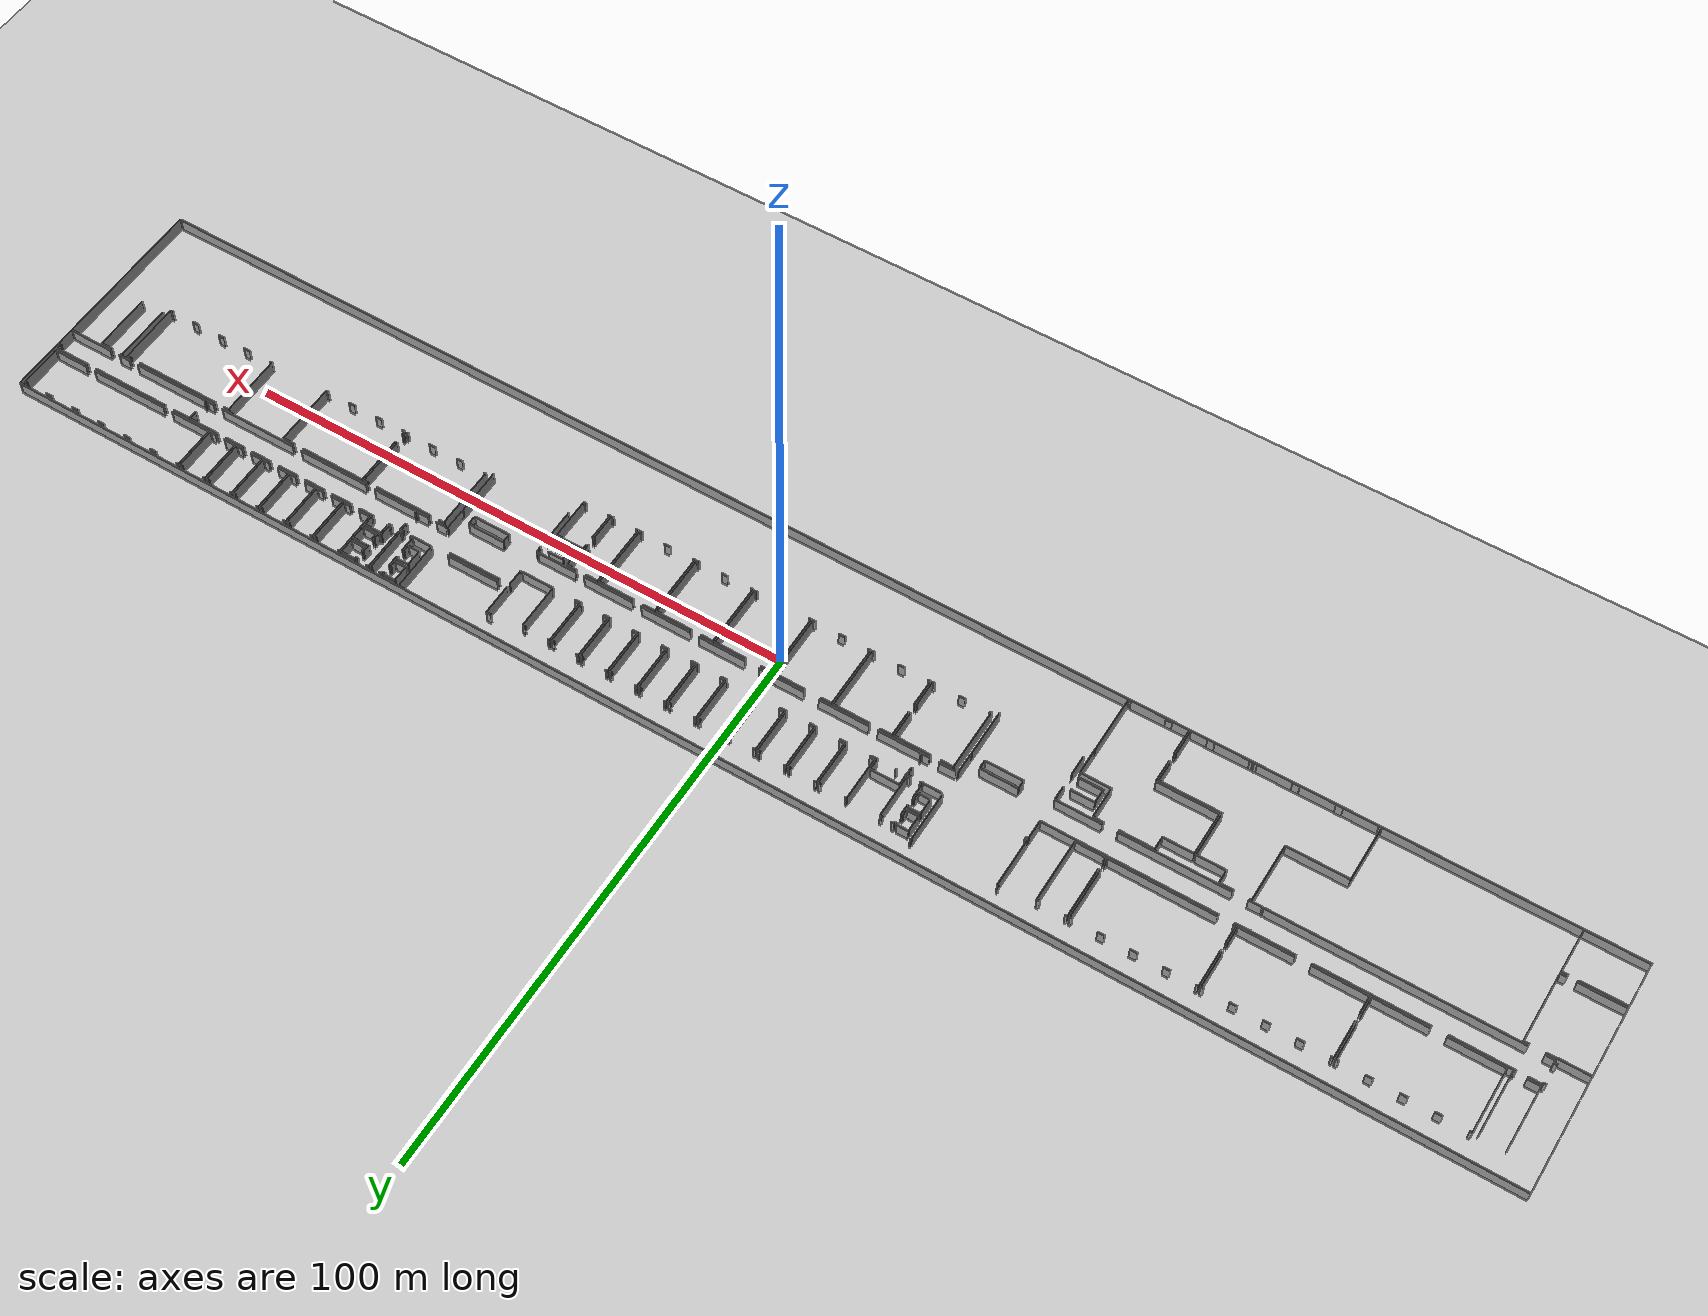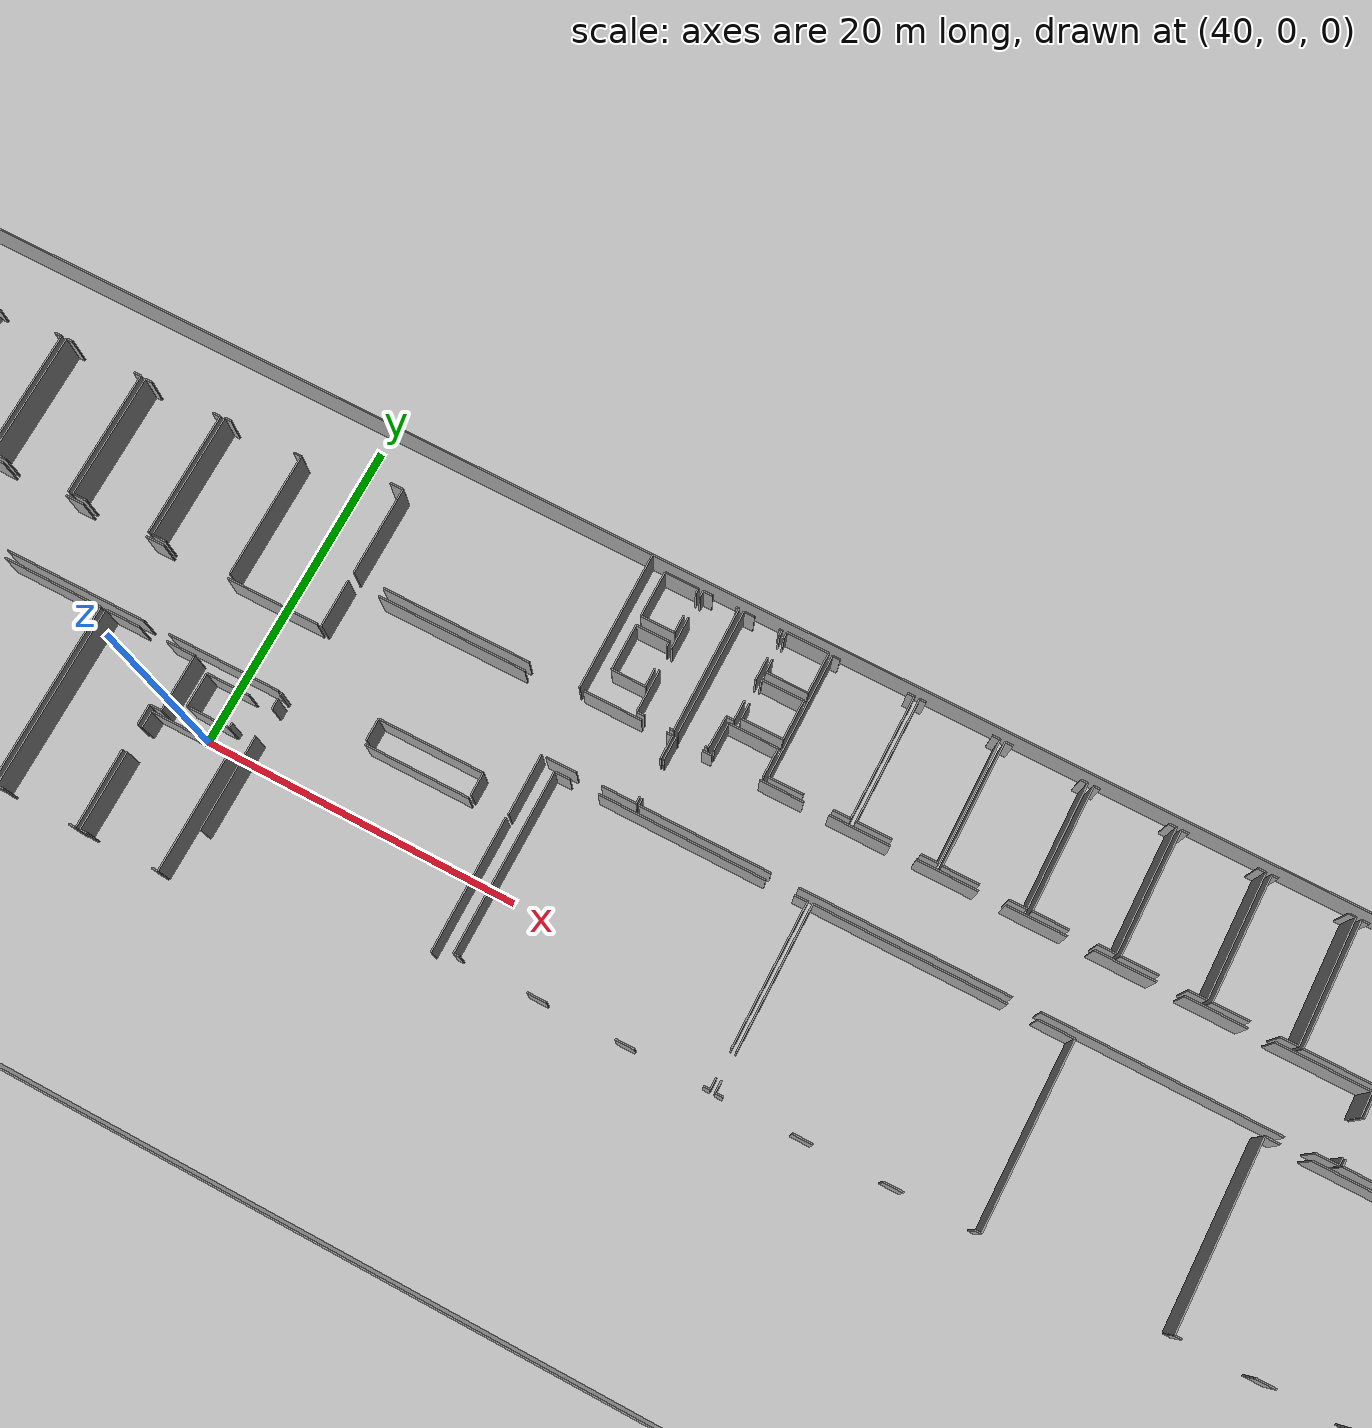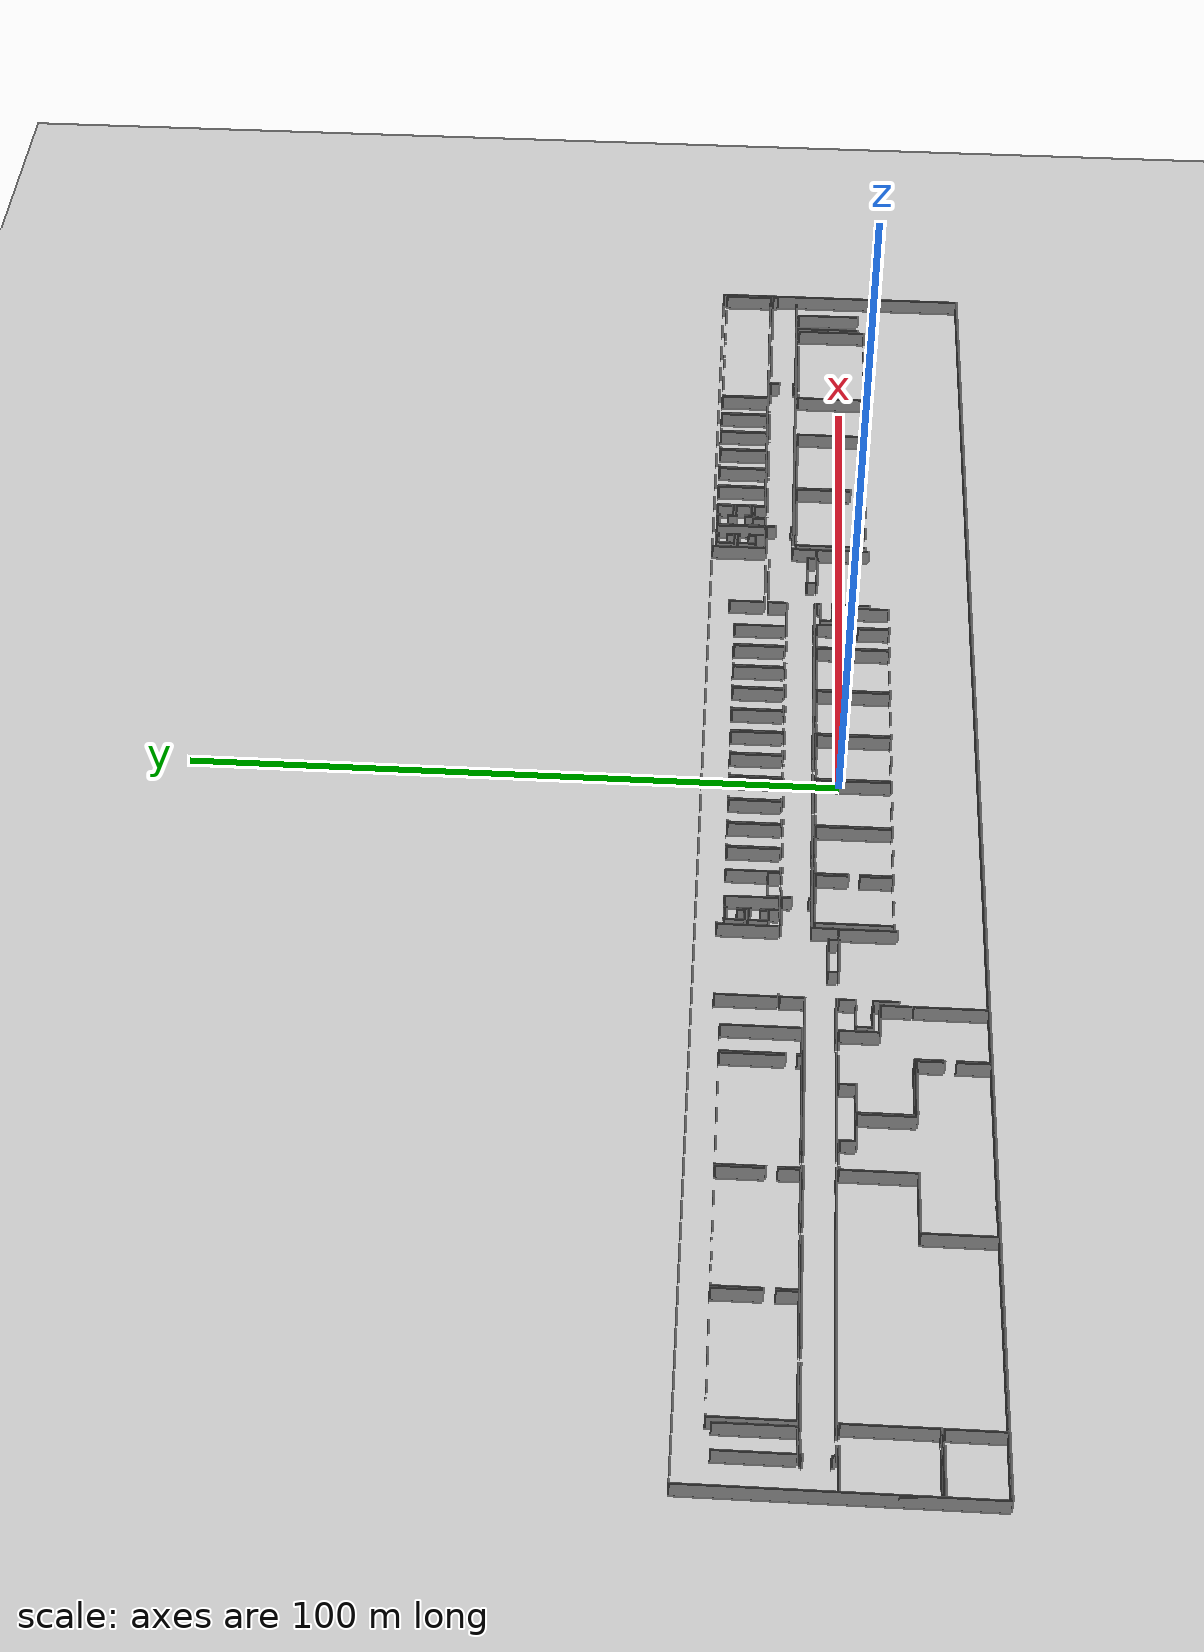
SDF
<sdf version="1.6">
  <world name="default">
    <light name="sun" type="directional">
      <cast_shadows>1</cast_shadows>
      <pose frame="">0 0 10 0 -0 0</pose>
      <diffuse>0.8 0.8 0.8 1</diffuse>
      <specular>0.1 0.1 0.1 1</specular>
      <attenuation>
        <range>1000</range>
        <constant>0.9</constant>
        <linear>0.01</linear>
        <quadratic>0.001</quadratic>
      </attenuation>
      <direction>-0.5 0.5 -1</direction>
    </light>
    <model name="ground_plane">
      <static>1</static>
      <link name="link">
        <collision name="collision">
          <geometry>
            <plane>
              <normal>0 0 1</normal>
              <size>100 100</size>
            </plane>
          </geometry>
          <surface>
            <friction>
              <ode>
                <mu>100</mu>
                <mu2>50</mu2>
              </ode>
              <torsional>
                <ode />
              </torsional>
            </friction>
            <contact>
              <ode />
            </contact>
            <bounce />
          </surface>
          <max_contacts>10</max_contacts>
        </collision>
        <visual name="visual">
          <cast_shadows>0</cast_shadows>
          <geometry>
            <plane>
              <normal>0 0 1</normal>
              <size>100 100</size>
            </plane>
          </geometry>
          <material>
            <script>
              <uri>file://media/materials/scripts/gazebo.material</uri>
              <name>Gazebo/Grey</name>
            </script>
          </material>
        </visual>
        <self_collide>0</self_collide>
        <kinematic>0</kinematic>
        <gravity>1</gravity>
      </link>
    </model>
    <gravity>0 0 -9.8</gravity>
    <magnetic_field>6e-06 2.3e-05 -4.2e-05</magnetic_field>
    <atmosphere type="adiabatic" />
    <physics default="0" name="default_physics" type="ode">
      <max_step_size>0.001</max_step_size>
      <real_time_factor>1</real_time_factor>
      <real_time_update_rate>1000</real_time_update_rate>
    </physics>
    <scene>
      <ambient>0.4 0.4 0.4 1</ambient>
      <background>0.7 0.7 0.7 1</background>
      <shadows>1</shadows>
    </scene>
    <spherical_coordinates>
      <surface_model>EARTH_WGS84</surface_model>
      <latitude_deg>0</latitude_deg>
      <longitude_deg>0</longitude_deg>
      <elevation>0</elevation>
      <heading_deg>0</heading_deg>
    </spherical_coordinates>
  <model name="50037765_PLAN3">
		<static>1</static>
		<link name="Wall_0">
			<collision name="Wall_0_Collision">
				<geometry>
					<box>
						<size>0.321969384059 0.1 2.5</size>
					</box>
				</geometry>
				<pose frame="">0.16098469203 0 1.25 0 0 0</pose>
			</collision>
			<visual name="Wall_0_Visual">
				<pose frame="">0.16098469203 0 1.25 0 0 0</pose>
				<geometry>
					<box>
						<size>0.321969384059 0.1 2.5</size>
					</box>
				</geometry>
				<material>
					<script>
						<uri>file://media/materials/scripts/gazebo.material</uri>
						<name>Gazebo/Grey</name>
					</script>
					<ambient>1 1 1 1</ambient>
				</material>
			</visual>
			<pose frame="">9.88181916388 -15.8259631821 0 0 0 3.14159265359</pose>
		</link>
		<link name="Wall_1">
			<collision name="Wall_1_Collision">
				<geometry>
					<box>
						<size>2.22686806169 0.1 2.5</size>
					</box>
				</geometry>
				<pose frame="">1.11343403084 0 1.25 0 0 0</pose>
			</collision>
			<visual name="Wall_1_Visual">
				<pose frame="">1.11343403084 0 1.25 0 0 0</pose>
				<geometry>
					<box>
						<size>2.22686806169 0.1 2.5</size>
					</box>
				</geometry>
				<material>
					<script>
						<uri>file://media/materials/scripts/gazebo.material</uri>
						<name>Gazebo/Grey</name>
					</script>
					<ambient>1 1 1 1</ambient>
				</material>
			</visual>
			<pose frame="">7.72960367035 -15.8259631821 0 0 0 3.14159265359</pose>
		</link>
		<link name="Wall_2">
			<collision name="Wall_2_Collision">
				<geometry>
					<box>
						<size>10.8921070859 0.1 2.5</size>
					</box>
				</geometry>
				<pose frame="">5.44605354295 0 1.25 0 0 0</pose>
			</collision>
			<visual name="Wall_2_Visual">
				<pose frame="">5.44605354295 0 1.25 0 0 0</pose>
				<geometry>
					<box>
						<size>10.8921070859 0.1 2.5</size>
					</box>
				</geometry>
				<material>
					<script>
						<uri>file://media/materials/scripts/gazebo.material</uri>
						<name>Gazebo/Grey</name>
					</script>
					<ambient>1 1 1 1</ambient>
				</material>
			</visual>
			<pose frame="">5.50273560866 -15.8259631821 0 0 0 1.57079632679</pose>
		</link>
		<link name="Wall_3">
			<collision name="Wall_3_Collision">
				<geometry>
					<box>
						<size>10.8921564394 0.1 2.5</size>
					</box>
				</geometry>
				<pose frame="">5.44607821971 0 1.25 0 0 0</pose>
			</collision>
			<visual name="Wall_3_Visual">
				<pose frame="">5.44607821971 0 1.25 0 0 0</pose>
				<geometry>
					<box>
						<size>10.8921564394 0.1 2.5</size>
					</box>
				</geometry>
				<material>
					<script>
						<uri>file://media/materials/scripts/gazebo.material</uri>
						<name>Gazebo/Grey</name>
					</script>
					<ambient>1 1 1 1</ambient>
				</material>
			</visual>
			<pose frame="">9.84902998685 -4.93385609618 0 0 0 -1.56778597465</pose>
		</link>
		<link name="Wall_4">
			<collision name="Wall_4_Collision">
				<geometry>
					<box>
						<size>9.34466127382 0.1 2.5</size>
					</box>
				</geometry>
				<pose frame="">4.67233063691 0 1.25 0 0 0</pose>
			</collision>
			<visual name="Wall_4_Visual">
				<pose frame="">4.67233063691 0 1.25 0 0 0</pose>
				<geometry>
					<box>
						<size>9.34466127382 0.1 2.5</size>
					</box>
				</geometry>
				<material>
					<script>
						<uri>file://media/materials/scripts/gazebo.material</uri>
						<name>Gazebo/Grey</name>
					</script>
					<ambient>1 1 1 1</ambient>
				</material>
			</visual>
			<pose frame="">32.053403148 -15.8197103623 0 0 0 3.14159265359</pose>
		</link>
		<link name="Wall_5">
			<collision name="Wall_5_Collision">
				<geometry>
					<box>
						<size>9.37582370098 0.1 2.5</size>
					</box>
				</geometry>
				<pose frame="">4.68791185049 0 1.25 0 0 0</pose>
			</collision>
			<visual name="Wall_5_Visual">
				<pose frame="">4.68791185049 0 1.25 0 0 0</pose>
				<geometry>
					<box>
						<size>9.37582370098 0.1 2.5</size>
					</box>
				</geometry>
				<material>
					<script>
						<uri>file://media/materials/scripts/gazebo.material</uri>
						<name>Gazebo/Grey</name>
					</script>
					<ambient>1 1 1 1</ambient>
				</material>
			</visual>
			<pose frame="">20.1211928652 -15.8197103623 0 0 0 3.14159265359</pose>
		</link>
		<link name="Wall_6">
			<collision name="Wall_6_Collision">
				<geometry>
					<box>
						<size>11.6262542178 0.1 2.5</size>
					</box>
				</geometry>
				<pose frame="">5.8131271089 0 1.25 0 0 0</pose>
			</collision>
			<visual name="Wall_6_Visual">
				<pose frame="">5.8131271089 0 1.25 0 0 0</pose>
				<geometry>
					<box>
						<size>11.6262542178 0.1 2.5</size>
					</box>
				</geometry>
				<material>
					<script>
						<uri>file://media/materials/scripts/gazebo.material</uri>
						<name>Gazebo/Grey</name>
					</script>
					<ambient>1 1 1 1</ambient>
				</material>
			</visual>
			<pose frame="">10.7453691642 -15.8197103623 0 0 0 1.57079632679</pose>
		</link>
		<link name="Wall_7">
			<collision name="Wall_7_Collision">
				<geometry>
					<box>
						<size>0.409839294906 0.1 2.5</size>
					</box>
				</geometry>
				<pose frame="">0.204919647453 0 1.25 0 0 0</pose>
			</collision>
			<visual name="Wall_7_Visual">
				<pose frame="">0.204919647453 0 1.25 0 0 0</pose>
				<geometry>
					<box>
						<size>0.409839294906 0.1 2.5</size>
					</box>
				</geometry>
				<material>
					<script>
						<uri>file://media/materials/scripts/gazebo.material</uri>
						<name>Gazebo/Grey</name>
					</script>
					<ambient>1 1 1 1</ambient>
				</material>
			</visual>
			<pose frame="">10.7453691642 -4.19345614448 0 0 0 0.0</pose>
		</link>
		<link name="Wall_8">
			<collision name="Wall_8_Collision">
				<geometry>
					<box>
						<size>1.25107232047 0.1 2.5</size>
					</box>
				</geometry>
				<pose frame="">0.625536160235 0 1.25 0 0 0</pose>
			</collision>
			<visual name="Wall_8_Visual">
				<pose frame="">0.625536160235 0 1.25 0 0 0</pose>
				<geometry>
					<box>
						<size>1.25107232047 0.1 2.5</size>
					</box>
				</geometry>
				<material>
					<script>
						<uri>file://media/materials/scripts/gazebo.material</uri>
						<name>Gazebo/Grey</name>
					</script>
					<ambient>1 1 1 1</ambient>
				</material>
			</visual>
			<pose frame="">15.3179596998 -4.19345614448 0 0 0 0.0</pose>
		</link>
		<link name="Wall_9">
			<collision name="Wall_9_Collision">
				<geometry>
					<box>
						<size>1.25107232047 0.1 2.5</size>
					</box>
				</geometry>
				<pose frame="">0.625536160235 0 1.25 0 0 0</pose>
			</collision>
			<visual name="Wall_9_Visual">
				<pose frame="">0.625536160235 0 1.25 0 0 0</pose>
				<geometry>
					<box>
						<size>1.25107232047 0.1 2.5</size>
					</box>
				</geometry>
				<material>
					<script>
						<uri>file://media/materials/scripts/gazebo.material</uri>
						<name>Gazebo/Grey</name>
					</script>
					<ambient>1 1 1 1</ambient>
				</material>
			</visual>
			<pose frame="">20.7139398484 -4.19345614448 0 0 0 0.0</pose>
		</link>
		<link name="Wall_10">
			<collision name="Wall_10_Collision">
				<geometry>
					<box>
						<size>1.25107232047 0.1 2.5</size>
					</box>
				</geometry>
				<pose frame="">0.625536160235 0 1.25 0 0 0</pose>
			</collision>
			<visual name="Wall_10_Visual">
				<pose frame="">0.625536160235 0 1.25 0 0 0</pose>
				<geometry>
					<box>
						<size>1.25107232047 0.1 2.5</size>
					</box>
				</geometry>
				<material>
					<script>
						<uri>file://media/materials/scripts/gazebo.material</uri>
						<name>Gazebo/Grey</name>
					</script>
					<ambient>1 1 1 1</ambient>
				</material>
			</visual>
			<pose frame="">26.1226289803 -4.19345614448 0 0 0 0.0</pose>
		</link>
		<link name="Wall_11">
			<collision name="Wall_11_Collision">
				<geometry>
					<box>
						<size>0.496921248785 0.1 2.5</size>
					</box>
				</geometry>
				<pose frame="">0.248460624392 0 1.25 0 0 0</pose>
			</collision>
			<visual name="Wall_11_Visual">
				<pose frame="">0.248460624392 0 1.25 0 0 0</pose>
				<geometry>
					<box>
						<size>0.496921248785 0.1 2.5</size>
					</box>
				</geometry>
				<material>
					<script>
						<uri>file://media/materials/scripts/gazebo.material</uri>
						<name>Gazebo/Grey</name>
					</script>
					<ambient>1 1 1 1</ambient>
				</material>
			</visual>
			<pose frame="">31.5046292472 -4.19345614448 0 0 0 0.0</pose>
		</link>
		<link name="Wall_12">
			<collision name="Wall_12_Collision">
				<geometry>
					<box>
						<size>6.9729870559 0.1 2.5</size>
					</box>
				</geometry>
				<pose frame="">3.48649352795 0 1.25 0 0 0</pose>
			</collision>
			<visual name="Wall_12_Visual">
				<pose frame="">3.48649352795 0 1.25 0 0 0</pose>
				<geometry>
					<box>
						<size>6.9729870559 0.1 2.5</size>
					</box>
				</geometry>
				<material>
					<script>
						<uri>file://media/materials/scripts/gazebo.material</uri>
						<name>Gazebo/Grey</name>
					</script>
					<ambient>1 1 1 1</ambient>
				</material>
			</visual>
			<pose frame="">32.001550496 -4.19345614448 0 0 0 -1.57079632679</pose>
		</link>
		<link name="Wall_13">
			<collision name="Wall_13_Collision">
				<geometry>
					<box>
						<size>3.08793038245 0.1 2.5</size>
					</box>
				</geometry>
				<pose frame="">1.54396519122 0 1.25 0 0 0</pose>
			</collision>
			<visual name="Wall_13_Visual">
				<pose frame="">1.54396519122 0 1.25 0 0 0</pose>
				<geometry>
					<box>
						<size>3.08793038245 0.1 2.5</size>
					</box>
				</geometry>
				<material>
					<script>
						<uri>file://media/materials/scripts/gazebo.material</uri>
						<name>Gazebo/Grey</name>
					</script>
					<ambient>1 1 1 1</ambient>
				</material>
			</visual>
			<pose frame="">32.001550496 -12.7322153664 0 0 0 -1.55400349704</pose>
		</link>
		<link name="Wall_14">
			<collision name="Wall_14_Collision">
				<geometry>
					<box>
						<size>9.35533681983 0.1 2.5</size>
					</box>
				</geometry>
				<pose frame="">4.67766840992 0 1.25 0 0 0</pose>
			</collision>
			<visual name="Wall_14_Visual">
				<pose frame="">4.67766840992 0 1.25 0 0 0</pose>
				<geometry>
					<box>
						<size>9.35533681983 0.1 2.5</size>
					</box>
				</geometry>
				<material>
					<script>
						<uri>file://media/materials/scripts/gazebo.material</uri>
						<name>Gazebo/Grey</name>
					</script>
					<ambient>1 1 1 1</ambient>
				</material>
			</visual>
			<pose frame="">53.6591831936 -15.8190749131 0 0 0 3.14159265359</pose>
		</link>
		<link name="Wall_15">
			<collision name="Wall_15_Collision">
				<geometry>
					<box>
						<size>9.3924470512 0.1 2.5</size>
					</box>
				</geometry>
				<pose frame="">4.6962235256 0 1.25 0 0 0</pose>
			</collision>
			<visual name="Wall_15_Visual">
				<pose frame="">4.6962235256 0 1.25 0 0 0</pose>
				<geometry>
					<box>
						<size>9.3924470512 0.1 2.5</size>
					</box>
				</geometry>
				<material>
					<script>
						<uri>file://media/materials/scripts/gazebo.material</uri>
						<name>Gazebo/Grey</name>
					</script>
					<ambient>1 1 1 1</ambient>
				</material>
			</visual>
			<pose frame="">41.7422236908 -15.8190749131 0 0 0 3.14159265359</pose>
		</link>
		<link name="Wall_16">
			<collision name="Wall_16_Collision">
				<geometry>
					<box>
						<size>3.05821349821 0.1 2.5</size>
					</box>
				</geometry>
				<pose frame="">1.52910674911 0 1.25 0 0 0</pose>
			</collision>
			<visual name="Wall_16_Visual">
				<pose frame="">1.52910674911 0 1.25 0 0 0</pose>
				<geometry>
					<box>
						<size>3.05821349821 0.1 2.5</size>
					</box>
				</geometry>
				<material>
					<script>
						<uri>file://media/materials/scripts/gazebo.material</uri>
						<name>Gazebo/Grey</name>
					</script>
					<ambient>1 1 1 1</ambient>
				</material>
			</visual>
			<pose frame="">32.3497766396 -15.8190749131 0 0 0 1.57079632679</pose>
		</link>
		<link name="Wall_17">
			<collision name="Wall_17_Collision">
				<geometry>
					<box>
						<size>6.95809212742 0.1 2.5</size>
					</box>
				</geometry>
				<pose frame="">3.47904606371 0 1.25 0 0 0</pose>
			</collision>
			<visual name="Wall_17_Visual">
				<pose frame="">3.47904606371 0 1.25 0 0 0</pose>
				<geometry>
					<box>
						<size>6.95809212742 0.1 2.5</size>
					</box>
				</geometry>
				<material>
					<script>
						<uri>file://media/materials/scripts/gazebo.material</uri>
						<name>Gazebo/Grey</name>
					</script>
					<ambient>1 1 1 1</ambient>
				</material>
			</visual>
			<pose frame="">32.3497766396 -11.1520312133 0 0 0 1.57079632679</pose>
		</link>
		<link name="Wall_18">
			<collision name="Wall_18_Collision">
				<geometry>
					<box>
						<size>0.425750942053 0.1 2.5</size>
					</box>
				</geometry>
				<pose frame="">0.212875471027 0 1.25 0 0 0</pose>
			</collision>
			<visual name="Wall_18_Visual">
				<pose frame="">0.212875471027 0 1.25 0 0 0</pose>
				<geometry>
					<box>
						<size>0.425750942053 0.1 2.5</size>
					</box>
				</geometry>
				<material>
					<script>
						<uri>file://media/materials/scripts/gazebo.material</uri>
						<name>Gazebo/Grey</name>
					</script>
					<ambient>1 1 1 1</ambient>
				</material>
			</visual>
			<pose frame="">32.3497766396 -4.19393908584 0 0 0 0.0</pose>
		</link>
		<link name="Wall_19">
			<collision name="Wall_19_Collision">
				<geometry>
					<box>
						<size>1.25463083581 0.1 2.5</size>
					</box>
				</geometry>
				<pose frame="">0.627315417903 0 1.25 0 0 0</pose>
			</collision>
			<visual name="Wall_19_Visual">
				<pose frame="">0.627315417903 0 1.25 0 0 0</pose>
				<geometry>
					<box>
						<size>1.25463083581 0.1 2.5</size>
					</box>
				</geometry>
				<material>
					<script>
						<uri>file://media/materials/scripts/gazebo.material</uri>
						<name>Gazebo/Grey</name>
					</script>
					<ambient>1 1 1 1</ambient>
				</material>
			</visual>
			<pose frame="">36.9364487288 -4.19393908584 0 0 0 0.0</pose>
		</link>
		<link name="Wall_20">
			<collision name="Wall_20_Collision">
				<geometry>
					<box>
						<size>1.22972122845 0.1 2.5</size>
					</box>
				</geometry>
				<pose frame="">0.614860614225 0 1.25 0 0 0</pose>
			</collision>
			<visual name="Wall_20_Visual">
				<pose frame="">0.614860614225 0 1.25 0 0 0</pose>
				<geometry>
					<box>
						<size>1.22972122845 0.1 2.5</size>
					</box>
				</geometry>
				<material>
					<script>
						<uri>file://media/materials/scripts/gazebo.material</uri>
						<name>Gazebo/Grey</name>
					</script>
					<ambient>1 1 1 1</ambient>
				</material>
			</visual>
			<pose frame="">42.3789437564 -4.19393908584 0 0 0 0.0</pose>
		</link>
		<link name="Wall_21">
			<collision name="Wall_21_Collision">
				<geometry>
					<box>
						<size>1.26352712415 0.1 2.5</size>
					</box>
				</geometry>
				<pose frame="">0.631763562074 0 1.25 0 0 0</pose>
			</collision>
			<visual name="Wall_21_Visual">
				<pose frame="">0.631763562074 0 1.25 0 0 0</pose>
				<geometry>
					<box>
						<size>1.26352712415 0.1 2.5</size>
					</box>
				</geometry>
				<material>
					<script>
						<uri>file://media/materials/scripts/gazebo.material</uri>
						<name>Gazebo/Grey</name>
					</script>
					<ambient>1 1 1 1</ambient>
				</material>
			</visual>
			<pose frame="">47.7324759006 -4.19393908584 0 0 0 0.0</pose>
		</link>
		<link name="Wall_22">
			<collision name="Wall_22_Collision">
				<geometry>
					<box>
						<size>0.498700506453 0.1 2.5</size>
					</box>
				</geometry>
				<pose frame="">0.249350253226 0 1.25 0 0 0</pose>
			</collision>
			<visual name="Wall_22_Visual">
				<pose frame="">0.249350253226 0 1.25 0 0 0</pose>
				<geometry>
					<box>
						<size>0.498700506453 0.1 2.5</size>
					</box>
				</geometry>
				<material>
					<script>
						<uri>file://media/materials/scripts/gazebo.material</uri>
						<name>Gazebo/Grey</name>
					</script>
					<ambient>1 1 1 1</ambient>
				</material>
			</visual>
			<pose frame="">53.1475195242 -4.19393908584 0 0 0 0.0</pose>
		</link>
		<link name="Wall_23">
			<collision name="Wall_23_Collision">
				<geometry>
					<box>
						<size>6.90618863944 0.1 2.5</size>
					</box>
				</geometry>
				<pose frame="">3.45309431972 0 1.25 0 0 0</pose>
			</collision>
			<visual name="Wall_23_Visual">
				<pose frame="">3.45309431972 0 1.25 0 0 0</pose>
				<geometry>
					<box>
						<size>6.90618863944 0.1 2.5</size>
					</box>
				</geometry>
				<material>
					<script>
						<uri>file://media/materials/scripts/gazebo.material</uri>
						<name>Gazebo/Grey</name>
					</script>
					<ambient>1 1 1 1</ambient>
				</material>
			</visual>
			<pose frame="">53.6462200306 -4.19393908584 0 0 0 -1.57079632679</pose>
		</link>
		<link name="Wall_24">
			<collision name="Wall_24_Collision">
				<geometry>
					<box>
						<size>3.12758057625 0.1 2.5</size>
					</box>
				</geometry>
				<pose frame="">1.56379028812 0 1.25 0 0 0</pose>
			</collision>
			<visual name="Wall_24_Visual">
				<pose frame="">1.56379028812 0 1.25 0 0 0</pose>
				<geometry>
					<box>
						<size>3.12758057625 0.1 2.5</size>
					</box>
				</geometry>
				<material>
					<script>
						<uri>file://media/materials/scripts/gazebo.material</uri>
						<name>Gazebo/Grey</name>
					</script>
					<ambient>1 1 1 1</ambient>
				</material>
			</visual>
			<pose frame="">53.6462200306 -12.6915212018 0 0 0 -1.56665152547</pose>
		</link>
		<link name="Wall_25">
			<collision name="Wall_25_Collision">
				<geometry>
					<box>
						<size>1.12479586196 0.1 2.5</size>
					</box>
				</geometry>
				<pose frame="">0.562397930978 0 1.25 0 0 0</pose>
			</collision>
			<visual name="Wall_25_Visual">
				<pose frame="">0.562397930978 0 1.25 0 0 0</pose>
				<geometry>
					<box>
						<size>1.12479586196 0.1 2.5</size>
					</box>
				</geometry>
				<material>
					<script>
						<uri>file://media/materials/scripts/gazebo.material</uri>
						<name>Gazebo/Grey</name>
					</script>
					<ambient>1 1 1 1</ambient>
				</material>
			</visual>
			<pose frame="">10.6421213835 -33.7765379458 0 0 0 3.14159265359</pose>
		</link>
		<link name="Wall_26">
			<collision name="Wall_26_Collision">
				<geometry>
					<box>
						<size>7.97458203331 0.1 2.5</size>
					</box>
				</geometry>
				<pose frame="">3.98729101666 0 1.25 0 0 0</pose>
			</collision>
			<visual name="Wall_26_Visual">
				<pose frame="">3.98729101666 0 1.25 0 0 0</pose>
				<geometry>
					<box>
						<size>7.97458203331 0.1 2.5</size>
					</box>
				</geometry>
				<material>
					<script>
						<uri>file://media/materials/scripts/gazebo.material</uri>
						<name>Gazebo/Grey</name>
					</script>
					<ambient>1 1 1 1</ambient>
				</material>
			</visual>
			<pose frame="">7.97458203331 -33.7765379458 0 0 0 3.14159265359</pose>
		</link>
		<link name="Wall_27">
			<collision name="Wall_27_Collision">
				<geometry>
					<box>
						<size>5.40716405391 0.1 2.5</size>
					</box>
				</geometry>
				<pose frame="">2.70358202696 0 1.25 0 0 0</pose>
			</collision>
			<visual name="Wall_27_Visual">
				<pose frame="">2.70358202696 0 1.25 0 0 0</pose>
				<geometry>
					<box>
						<size>5.40716405391 0.1 2.5</size>
					</box>
				</geometry>
				<material>
					<script>
						<uri>file://media/materials/scripts/gazebo.material</uri>
						<name>Gazebo/Grey</name>
					</script>
					<ambient>1 1 1 1</ambient>
				</material>
			</visual>
			<pose frame="">0.0 -33.7765379458 0 0 0 1.57079632679</pose>
		</link>
		<link name="Wall_28">
			<collision name="Wall_28_Collision">
				<geometry>
					<box>
						<size>1.30902528452 0.1 2.5</size>
					</box>
				</geometry>
				<pose frame="">0.654512642261 0 1.25 0 0 0</pose>
			</collision>
			<visual name="Wall_28_Visual">
				<pose frame="">0.654512642261 0 1.25 0 0 0</pose>
				<geometry>
					<box>
						<size>1.30902528452 0.1 2.5</size>
					</box>
				</geometry>
				<material>
					<script>
						<uri>file://media/materials/scripts/gazebo.material</uri>
						<name>Gazebo/Grey</name>
					</script>
					<ambient>1 1 1 1</ambient>
				</material>
			</visual>
			<pose frame="">0.0 -22.3503993798 0 0 0 1.57079632679</pose>
		</link>
		<link name="Wall_29">
			<collision name="Wall_29_Collision">
				<geometry>
					<box>
						<size>5.44132580114 0.1 2.5</size>
					</box>
				</geometry>
				<pose frame="">2.72066290057 0 1.25 0 0 0</pose>
			</collision>
			<visual name="Wall_29_Visual">
				<pose frame="">2.72066290057 0 1.25 0 0 0</pose>
				<geometry>
					<box>
						<size>5.44132580114 0.1 2.5</size>
					</box>
				</geometry>
				<material>
					<script>
						<uri>file://media/materials/scripts/gazebo.material</uri>
						<name>Gazebo/Grey</name>
					</script>
					<ambient>1 1 1 1</ambient>
				</material>
			</visual>
			<pose frame="">0.0 -21.0413740953 0 0 0 0.0</pose>
		</link>
		<link name="Wall_30">
			<collision name="Wall_30_Collision">
				<geometry>
					<box>
						<size>0.0960799140873 0.1 2.5</size>
					</box>
				</geometry>
				<pose frame="">0.0480399570436 0 1.25 0 0 0</pose>
			</collision>
			<visual name="Wall_30_Visual">
				<pose frame="">0.0480399570436 0 1.25 0 0 0</pose>
				<geometry>
					<box>
						<size>0.0960799140873 0.1 2.5</size>
					</box>
				</geometry>
				<material>
					<script>
						<uri>file://media/materials/scripts/gazebo.material</uri>
						<name>Gazebo/Grey</name>
					</script>
					<ambient>1 1 1 1</ambient>
				</material>
			</visual>
			<pose frame="">5.44132580114 -21.0413740953 0 0 0 1.57079632679</pose>
		</link>
		<link name="Wall_31">
			<collision name="Wall_31_Collision">
				<geometry>
					<box>
						<size>1.64017055456 0.1 2.5</size>
					</box>
				</geometry>
				<pose frame="">0.820085277278 0 1.25 0 0 0</pose>
			</collision>
			<visual name="Wall_31_Visual">
				<pose frame="">0.820085277278 0 1.25 0 0 0</pose>
				<geometry>
					<box>
						<size>1.64017055456 0.1 2.5</size>
					</box>
				</geometry>
				<material>
					<script>
						<uri>file://media/materials/scripts/gazebo.material</uri>
						<name>Gazebo/Grey</name>
					</script>
					<ambient>1 1 1 1</ambient>
				</material>
			</visual>
			<pose frame="">5.44132580114 -20.9452941812 0 0 0 0.0</pose>
		</link>
		<link name="Wall_32">
			<collision name="Wall_32_Collision">
				<geometry>
					<box>
						<size>0.915580578132 0.1 2.5</size>
					</box>
				</geometry>
				<pose frame="">0.457790289066 0 1.25 0 0 0</pose>
			</collision>
			<visual name="Wall_32_Visual">
				<pose frame="">0.457790289066 0 1.25 0 0 0</pose>
				<geometry>
					<box>
						<size>0.915580578132 0.1 2.5</size>
					</box>
				</geometry>
				<material>
					<script>
						<uri>file://media/materials/scripts/gazebo.material</uri>
						<name>Gazebo/Grey</name>
					</script>
					<ambient>1 1 1 1</ambient>
				</material>
			</visual>
			<pose frame="">9.71644987259 -20.9452941812 0 0 0 0.0</pose>
		</link>
		<link name="Wall_33">
			<collision name="Wall_33_Collision">
				<geometry>
					<box>
						<size>12.8312477326 0.1 2.5</size>
					</box>
				</geometry>
				<pose frame="">6.41562386629 0 1.25 0 0 0</pose>
			</collision>
			<visual name="Wall_33_Visual">
				<pose frame="">6.41562386629 0 1.25 0 0 0</pose>
				<geometry>
					<box>
						<size>12.8312477326 0.1 2.5</size>
					</box>
				</geometry>
				<material>
					<script>
						<uri>file://media/materials/scripts/gazebo.material</uri>
						<name>Gazebo/Grey</name>
					</script>
					<ambient>1 1 1 1</ambient>
				</material>
			</visual>
			<pose frame="">10.6320304507 -20.9452941812 0 0 0 -1.57000989246</pose>
		</link>
		<link name="Wall_34">
			<collision name="Wall_34_Collision">
				<geometry>
					<box>
						<size>10.6064853942 0.1 2.5</size>
					</box>
				</geometry>
				<pose frame="">5.3032426971 0 1.25 0 0 0</pose>
			</collision>
			<visual name="Wall_34_Visual">
				<pose frame="">5.3032426971 0 1.25 0 0 0</pose>
				<geometry>
					<box>
						<size>10.6064853942 0.1 2.5</size>
					</box>
				</geometry>
				<material>
					<script>
						<uri>file://media/materials/scripts/gazebo.material</uri>
						<name>Gazebo/Grey</name>
					</script>
					<ambient>1 1 1 1</ambient>
				</material>
			</visual>
			<pose frame="">10.6168559246 -42.2056440595 0 0 0 3.14159265359</pose>
		</link>
		<link name="Wall_35">
			<collision name="Wall_35_Collision">
				<geometry>
					<box>
						<size>0.224694825537 0.1 2.5</size>
					</box>
				</geometry>
				<pose frame="">0.112347412769 0 1.25 0 0 0</pose>
			</collision>
			<visual name="Wall_35_Visual">
				<pose frame="">0.112347412769 0 1.25 0 0 0</pose>
				<geometry>
					<box>
						<size>0.224694825537 0.1 2.5</size>
					</box>
				</geometry>
				<material>
					<script>
						<uri>file://media/materials/scripts/gazebo.material</uri>
						<name>Gazebo/Grey</name>
					</script>
					<ambient>1 1 1 1</ambient>
				</material>
			</visual>
			<pose frame="">0.0103705304094 -42.2056440595 0 0 0 1.57079632679</pose>
		</link>
		<link name="Wall_36">
			<collision name="Wall_36_Collision">
				<geometry>
					<box>
						<size>1.80620071297 0.1 2.5</size>
					</box>
				</geometry>
				<pose frame="">0.903100356487 0 1.25 0 0 0</pose>
			</collision>
			<visual name="Wall_36_Visual">
				<pose frame="">0.903100356487 0 1.25 0 0 0</pose>
				<geometry>
					<box>
						<size>1.80620071297 0.1 2.5</size>
					</box>
				</geometry>
				<material>
					<script>
						<uri>file://media/materials/scripts/gazebo.material</uri>
						<name>Gazebo/Grey</name>
					</script>
					<ambient>1 1 1 1</ambient>
				</material>
			</visual>
			<pose frame="">0.0103705304094 -35.9098678901 0 0 0 1.57079632679</pose>
		</link>
		<link name="Wall_37">
			<collision name="Wall_37_Collision">
				<geometry>
					<box>
						<size>7.94939282832 0.1 2.5</size>
					</box>
				</geometry>
				<pose frame="">3.97469641416 0 1.25 0 0 0</pose>
			</collision>
			<visual name="Wall_37_Visual">
				<pose frame="">3.97469641416 0 1.25 0 0 0</pose>
				<geometry>
					<box>
						<size>7.94939282832 0.1 2.5</size>
					</box>
				</geometry>
				<material>
					<script>
						<uri>file://media/materials/scripts/gazebo.material</uri>
						<name>Gazebo/Grey</name>
					</script>
					<ambient>1 1 1 1</ambient>
				</material>
			</visual>
			<pose frame="">0.0103705304094 -34.1036671771 0 0 0 0.0</pose>
		</link>
		<link name="Wall_38">
			<collision name="Wall_38_Collision">
				<geometry>
					<box>
						<size>1.13356506046 0.1 2.5</size>
					</box>
				</geometry>
				<pose frame="">0.566782530231 0 1.25 0 0 0</pose>
			</collision>
			<visual name="Wall_38_Visual">
				<pose frame="">0.566782530231 0 1.25 0 0 0</pose>
				<geometry>
					<box>
						<size>1.13356506046 0.1 2.5</size>
					</box>
				</geometry>
				<material>
					<script>
						<uri>file://media/materials/scripts/gazebo.material</uri>
						<name>Gazebo/Grey</name>
					</script>
					<ambient>1 1 1 1</ambient>
				</material>
			</visual>
			<pose frame="">9.49846539026 -34.1036671771 0 0 0 0.0</pose>
		</link>
		<link name="Wall_39">
			<collision name="Wall_39_Collision">
				<geometry>
					<box>
						<size>8.10199109284 0.1 2.5</size>
					</box>
				</geometry>
				<pose frame="">4.05099554642 0 1.25 0 0 0</pose>
			</collision>
			<visual name="Wall_39_Visual">
				<pose frame="">4.05099554642 0 1.25 0 0 0</pose>
				<geometry>
					<box>
						<size>8.10199109284 0.1 2.5</size>
					</box>
				</geometry>
				<material>
					<script>
						<uri>file://media/materials/scripts/gazebo.material</uri>
						<name>Gazebo/Grey</name>
					</script>
					<ambient>1 1 1 1</ambient>
				</material>
			</visual>
			<pose frame="">10.6320304507 -34.1036671771 0 0 0 -1.57266926578</pose>
		</link>
		<link name="Wall_40">
			<collision name="Wall_40_Collision">
				<geometry>
					<box>
						<size>42.2044239971 0.1 2.5</size>
					</box>
				</geometry>
				<pose frame="">21.1022119986 0 1.25 0 0 0</pose>
			</collision>
			<visual name="Wall_40_Visual">
				<pose frame="">21.1022119986 0 1.25 0 0 0</pose>
				<geometry>
					<box>
						<size>42.2044239971 0.1 2.5</size>
					</box>
				</geometry>
				<material>
					<script>
						<uri>file://media/materials/scripts/gazebo.material</uri>
						<name>Gazebo/Grey</name>
					</script>
					<ambient>1 1 1 1</ambient>
				</material>
			</visual>
			<pose frame="">51.9152564991 -20.6463788929 0 0 0 3.14159265359</pose>
		</link>
		<link name="Wall_41">
			<collision name="Wall_41_Collision">
				<geometry>
					<box>
						<size>1.613125838 0.1 2.5</size>
					</box>
				</geometry>
				<pose frame="">0.806562918999 0 1.25 0 0 0</pose>
			</collision>
			<visual name="Wall_41_Visual">
				<pose frame="">0.806562918999 0 1.25 0 0 0</pose>
				<geometry>
					<box>
						<size>1.613125838 0.1 2.5</size>
					</box>
				</geometry>
				<material>
					<script>
						<uri>file://media/materials/scripts/gazebo.material</uri>
						<name>Gazebo/Grey</name>
					</script>
					<ambient>1 1 1 1</ambient>
				</material>
			</visual>
			<pose frame="">7.1150734897 -20.6463788929 0 0 0 3.14159265359</pose>
		</link>
		<link name="Wall_42">
			<collision name="Wall_42_Collision">
				<geometry>
					<box>
						<size>0.56859991485 0.1 2.5</size>
					</box>
				</geometry>
				<pose frame="">0.284299957425 0 1.25 0 0 0</pose>
			</collision>
			<visual name="Wall_42_Visual">
				<pose frame="">0.284299957425 0 1.25 0 0 0</pose>
				<geometry>
					<box>
						<size>0.56859991485 0.1 2.5</size>
					</box>
				</geometry>
				<material>
					<script>
						<uri>file://media/materials/scripts/gazebo.material</uri>
						<name>Gazebo/Grey</name>
					</script>
					<ambient>1 1 1 1</ambient>
				</material>
			</visual>
			<pose frame="">5.5019476517 -20.6463788929 0 0 0 1.57079632679</pose>
		</link>
		<link name="Wall_43">
			<collision name="Wall_43_Collision">
				<geometry>
					<box>
						<size>0.522466305308 0.1 2.5</size>
					</box>
				</geometry>
				<pose frame="">0.261233152654 0 1.25 0 0 0</pose>
			</collision>
			<visual name="Wall_43_Visual">
				<pose frame="">0.261233152654 0 1.25 0 0 0</pose>
				<geometry>
					<box>
						<size>0.522466305308 0.1 2.5</size>
					</box>
				</geometry>
				<material>
					<script>
						<uri>file://media/materials/scripts/gazebo.material</uri>
						<name>Gazebo/Grey</name>
					</script>
					<ambient>1 1 1 1</ambient>
				</material>
			</visual>
			<pose frame="">5.5019476517 -20.0777789781 0 0 0 3.14159265359</pose>
		</link>
		<link name="Wall_44">
			<collision name="Wall_44_Collision">
				<geometry>
					<box>
						<size>0.478645730735 0.1 2.5</size>
					</box>
				</geometry>
				<pose frame="">0.239322865367 0 1.25 0 0 0</pose>
			</collision>
			<visual name="Wall_44_Visual">
				<pose frame="">0.239322865367 0 1.25 0 0 0</pose>
				<geometry>
					<box>
						<size>0.478645730735 0.1 2.5</size>
					</box>
				</geometry>
				<material>
					<script>
						<uri>file://media/materials/scripts/gazebo.material</uri>
						<name>Gazebo/Grey</name>
					</script>
					<ambient>1 1 1 1</ambient>
				</material>
			</visual>
			<pose frame="">4.97948134639 -16.4135249001 0 0 0 0.0</pose>
		</link>
		<link name="Wall_45">
			<collision name="Wall_45_Collision">
				<geometry>
					<box>
						<size>0.296653089236 0.1 2.5</size>
					</box>
				</geometry>
				<pose frame="">0.148326544618 0 1.25 0 0 0</pose>
			</collision>
			<visual name="Wall_45_Visual">
				<pose frame="">0.148326544618 0 1.25 0 0 0</pose>
				<geometry>
					<box>
						<size>0.296653089236 0.1 2.5</size>
					</box>
				</geometry>
				<material>
					<script>
						<uri>file://media/materials/scripts/gazebo.material</uri>
						<name>Gazebo/Grey</name>
					</script>
					<ambient>1 1 1 1</ambient>
				</material>
			</visual>
			<pose frame="">5.45812707712 -16.4135249001 0 0 0 1.57079632679</pose>
		</link>
		<link name="Wall_46">
			<collision name="Wall_46_Collision">
				<geometry>
					<box>
						<size>2.25271813381 0.1 2.5</size>
					</box>
				</geometry>
				<pose frame="">1.12635906691 0 1.25 0 0 0</pose>
			</collision>
			<visual name="Wall_46_Visual">
				<pose frame="">1.12635906691 0 1.25 0 0 0</pose>
				<geometry>
					<box>
						<size>2.25271813381 0.1 2.5</size>
					</box>
				</geometry>
				<material>
					<script>
						<uri>file://media/materials/scripts/gazebo.material</uri>
						<name>Gazebo/Grey</name>
					</script>
					<ambient>1 1 1 1</ambient>
				</material>
			</visual>
			<pose frame="">5.45812707712 -16.1168718108 0 0 0 0.0</pose>
		</link>
		<link name="Wall_47">
			<collision name="Wall_47_Collision">
				<geometry>
					<box>
						<size>10.5943101882 0.1 2.5</size>
					</box>
				</geometry>
				<pose frame="">5.29715509408 0 1.25 0 0 0</pose>
			</collision>
			<visual name="Wall_47_Visual">
				<pose frame="">5.29715509408 0 1.25 0 0 0</pose>
				<geometry>
					<box>
						<size>10.5943101882 0.1 2.5</size>
					</box>
				</geometry>
				<material>
					<script>
						<uri>file://media/materials/scripts/gazebo.material</uri>
						<name>Gazebo/Grey</name>
					</script>
					<ambient>1 1 1 1</ambient>
				</material>
			</visual>
			<pose frame="">9.48392631331 -16.1168718108 0 0 0 0.0</pose>
		</link>
		<link name="Wall_48">
			<collision name="Wall_48_Collision">
				<geometry>
					<box>
						<size>19.0088263889 0.1 2.5</size>
					</box>
				</geometry>
				<pose frame="">9.50441319447 0 1.25 0 0 0</pose>
			</collision>
			<visual name="Wall_48_Visual">
				<pose frame="">9.50441319447 0 1.25 0 0 0</pose>
				<geometry>
					<box>
						<size>19.0088263889 0.1 2.5</size>
					</box>
				</geometry>
				<material>
					<script>
						<uri>file://media/materials/scripts/gazebo.material</uri>
						<name>Gazebo/Grey</name>
					</script>
					<ambient>1 1 1 1</ambient>
				</material>
			</visual>
			<pose frame="">22.7087418742 -16.1168718108 0 0 0 0.0</pose>
		</link>
		<link name="Wall_49">
			<collision name="Wall_49_Collision">
				<geometry>
					<box>
						<size>7.59895532157 0.1 2.5</size>
					</box>
				</geometry>
				<pose frame="">3.79947766078 0 1.25 0 0 0</pose>
			</collision>
			<visual name="Wall_49_Visual">
				<pose frame="">3.79947766078 0 1.25 0 0 0</pose>
				<geometry>
					<box>
						<size>7.59895532157 0.1 2.5</size>
					</box>
				</geometry>
				<material>
					<script>
						<uri>file://media/materials/scripts/gazebo.material</uri>
						<name>Gazebo/Grey</name>
					</script>
					<ambient>1 1 1 1</ambient>
				</material>
			</visual>
			<pose frame="">44.2761407901 -16.1168718108 0 0 0 0.0</pose>
		</link>
		<link name="Wall_50">
			<collision name="Wall_50_Collision">
				<geometry>
					<box>
						<size>0.15380411644 0.1 2.5</size>
					</box>
				</geometry>
				<pose frame="">0.0769020582199 0 1.25 0 0 0</pose>
			</collision>
			<visual name="Wall_50_Visual">
				<pose frame="">0.0769020582199 0 1.25 0 0 0</pose>
				<geometry>
					<box>
						<size>0.15380411644 0.1 2.5</size>
					</box>
				</geometry>
				<material>
					<script>
						<uri>file://media/materials/scripts/gazebo.material</uri>
						<name>Gazebo/Grey</name>
					</script>
					<ambient>1 1 1 1</ambient>
				</material>
			</visual>
			<pose frame="">51.8750961117 -16.1168718108 0 0 0 -1.57079632679</pose>
		</link>
		<link name="Wall_51">
			<collision name="Wall_51_Collision">
				<geometry>
					<box>
						<size>0.180666680389 0.1 2.5</size>
					</box>
				</geometry>
				<pose frame="">0.0903333401947 0 1.25 0 0 0</pose>
			</collision>
			<visual name="Wall_51_Visual">
				<pose frame="">0.0903333401947 0 1.25 0 0 0</pose>
				<geometry>
					<box>
						<size>0.180666680389 0.1 2.5</size>
					</box>
				</geometry>
				<material>
					<script>
						<uri>file://media/materials/scripts/gazebo.material</uri>
						<name>Gazebo/Grey</name>
					</script>
					<ambient>1 1 1 1</ambient>
				</material>
			</visual>
			<pose frame="">51.8750961117 -20.4702323838 0 0 0 -1.34663376916</pose>
		</link>
		<link name="Wall_52">
			<collision name="Wall_52_Collision">
				<geometry>
					<box>
						<size>1.44526558598 0.1 2.5</size>
					</box>
				</geometry>
				<pose frame="">0.72263279299 0 1.25 0 0 0</pose>
			</collision>
			<visual name="Wall_52_Visual">
				<pose frame="">0.72263279299 0 1.25 0 0 0</pose>
				<geometry>
					<box>
						<size>1.44526558598 0.1 2.5</size>
					</box>
				</geometry>
				<material>
					<script>
						<uri>file://media/materials/scripts/gazebo.material</uri>
						<name>Gazebo/Grey</name>
					</script>
					<ambient>1 1 1 1</ambient>
				</material>
			</visual>
			<pose frame="">99.1906411047 -20.8225254021 0 0 0 1.57079632679</pose>
		</link>
		<link name="Wall_53">
			<collision name="Wall_53_Collision">
				<geometry>
					<box>
						<size>6.73245683712 0.1 2.5</size>
					</box>
				</geometry>
				<pose frame="">3.36622841856 0 1.25 0 0 0</pose>
			</collision>
			<visual name="Wall_53_Visual">
				<pose frame="">3.36622841856 0 1.25 0 0 0</pose>
				<geometry>
					<box>
						<size>6.73245683712 0.1 2.5</size>
					</box>
				</geometry>
				<material>
					<script>
						<uri>file://media/materials/scripts/gazebo.material</uri>
						<name>Gazebo/Grey</name>
					</script>
					<ambient>1 1 1 1</ambient>
				</material>
			</visual>
			<pose frame="">99.1906411047 -19.3772598161 0 0 0 3.14159265359</pose>
		</link>
		<link name="Wall_54">
			<collision name="Wall_54_Collision">
				<geometry>
					<box>
						<size>1.43077734497 0.1 2.5</size>
					</box>
				</geometry>
				<pose frame="">0.715388672483 0 1.25 0 0 0</pose>
			</collision>
			<visual name="Wall_54_Visual">
				<pose frame="">0.715388672483 0 1.25 0 0 0</pose>
				<geometry>
					<box>
						<size>1.43077734497 0.1 2.5</size>
					</box>
				</geometry>
				<material>
					<script>
						<uri>file://media/materials/scripts/gazebo.material</uri>
						<name>Gazebo/Grey</name>
					</script>
					<ambient>1 1 1 1</ambient>
				</material>
			</visual>
			<pose frame="">92.4581842675 -19.3772598161 0 0 0 -1.57079632679</pose>
		</link>
		<link name="Wall_55">
			<collision name="Wall_55_Collision">
				<geometry>
					<box>
						<size>0.224694825537 0.1 2.5</size>
					</box>
				</geometry>
				<pose frame="">0.112347412769 0 1.25 0 0 0</pose>
			</collision>
			<visual name="Wall_55_Visual">
				<pose frame="">0.112347412769 0 1.25 0 0 0</pose>
				<geometry>
					<box>
						<size>0.224694825537 0.1 2.5</size>
					</box>
				</geometry>
				<material>
					<script>
						<uri>file://media/materials/scripts/gazebo.material</uri>
						<name>Gazebo/Grey</name>
					</script>
					<ambient>1 1 1 1</ambient>
				</material>
			</visual>
			<pose frame="">86.8952080778 -20.8080371611 0 0 0 1.57079632679</pose>
		</link>
		<link name="Wall_56">
			<collision name="Wall_56_Collision">
				<geometry>
					<box>
						<size>8.12891992705 0.1 2.5</size>
					</box>
				</geometry>
				<pose frame="">4.06445996353 0 1.25 0 0 0</pose>
			</collision>
			<visual name="Wall_56_Visual">
				<pose frame="">4.06445996353 0 1.25 0 0 0</pose>
				<geometry>
					<box>
						<size>8.12891992705 0.1 2.5</size>
					</box>
				</geometry>
				<material>
					<script>
						<uri>file://media/materials/scripts/gazebo.material</uri>
						<name>Gazebo/Grey</name>
					</script>
					<ambient>1 1 1 1</ambient>
				</material>
			</visual>
			<pose frame="">86.8952080778 -20.5833423355 0 0 0 3.14159265359</pose>
		</link>
		<link name="Wall_57">
			<collision name="Wall_57_Collision">
				<geometry>
					<box>
						<size>0.0612572997223 0.1 2.5</size>
					</box>
				</geometry>
				<pose frame="">0.0306286498612 0 1.25 0 0 0</pose>
			</collision>
			<visual name="Wall_57_Visual">
				<pose frame="">0.0306286498612 0 1.25 0 0 0</pose>
				<geometry>
					<box>
						<size>0.0612572997223 0.1 2.5</size>
					</box>
				</geometry>
				<material>
					<script>
						<uri>file://media/materials/scripts/gazebo.material</uri>
						<name>Gazebo/Grey</name>
					</script>
					<ambient>1 1 1 1</ambient>
				</material>
			</visual>
			<pose frame="">76.1894146878 -20.5833423355 0 0 0 -1.57079632679</pose>
		</link>
		<link name="Wall_58">
			<collision name="Wall_58_Collision">
				<geometry>
					<box>
						<size>19.2269125431 0.1 2.5</size>
					</box>
				</geometry>
				<pose frame="">9.61345627157 0 1.25 0 0 0</pose>
			</collision>
			<visual name="Wall_58_Visual">
				<pose frame="">9.61345627157 0 1.25 0 0 0</pose>
				<geometry>
					<box>
						<size>19.2269125431 0.1 2.5</size>
					</box>
				</geometry>
				<material>
					<script>
						<uri>file://media/materials/scripts/gazebo.material</uri>
						<name>Gazebo/Grey</name>
					</script>
					<ambient>1 1 1 1</ambient>
				</material>
			</visual>
			<pose frame="">76.1894146878 -20.6445996353 0 0 0 3.14159265359</pose>
		</link>
		<link name="Wall_59">
			<collision name="Wall_59_Collision">
				<geometry>
					<box>
						<size>2.31862692144 0.1 2.5</size>
					</box>
				</geometry>
				<pose frame="">1.15931346072 0 1.25 0 0 0</pose>
			</collision>
			<visual name="Wall_59_Visual">
				<pose frame="">1.15931346072 0 1.25 0 0 0</pose>
				<geometry>
					<box>
						<size>2.31862692144 0.1 2.5</size>
					</box>
				</geometry>
				<material>
					<script>
						<uri>file://media/materials/scripts/gazebo.material</uri>
						<name>Gazebo/Grey</name>
					</script>
					<ambient>1 1 1 1</ambient>
				</material>
			</visual>
			<pose frame="">54.3917289936 -20.6445996353 0 0 0 3.14159265359</pose>
		</link>
		<link name="Wall_60">
			<collision name="Wall_60_Collision">
				<geometry>
					<box>
						<size>0.143103152463 0.1 2.5</size>
					</box>
				</geometry>
				<pose frame="">0.0715515762317 0 1.25 0 0 0</pose>
			</collision>
			<visual name="Wall_60_Visual">
				<pose frame="">0.0715515762317 0 1.25 0 0 0</pose>
				<geometry>
					<box>
						<size>0.143103152463 0.1 2.5</size>
					</box>
				</geometry>
				<material>
					<script>
						<uri>file://media/materials/scripts/gazebo.material</uri>
						<name>Gazebo/Grey</name>
					</script>
					<ambient>1 1 1 1</ambient>
				</material>
			</visual>
			<pose frame="">52.0731020722 -20.6445996353 0 0 0 1.57079632679</pose>
		</link>
		<link name="Wall_61">
			<collision name="Wall_61_Collision">
				<geometry>
					<box>
						<size>0.153753280506 0.1 2.5</size>
					</box>
				</geometry>
				<pose frame="">0.0768766402532 0 1.25 0 0 0</pose>
			</collision>
			<visual name="Wall_61_Visual">
				<pose frame="">0.0768766402532 0 1.25 0 0 0</pose>
				<geometry>
					<box>
						<size>0.153753280506 0.1 2.5</size>
					</box>
				</geometry>
				<material>
					<script>
						<uri>file://media/materials/scripts/gazebo.material</uri>
						<name>Gazebo/Grey</name>
					</script>
					<ambient>1 1 1 1</ambient>
				</material>
			</visual>
			<pose frame="">52.0731020722 -16.281605653 0 0 0 1.57079632679</pose>
		</link>
		<link name="Wall_62">
			<collision name="Wall_62_Collision">
				<geometry>
					<box>
						<size>2.25254020805 0.1 2.5</size>
					</box>
				</geometry>
				<pose frame="">1.12627010402 0 1.25 0 0 0</pose>
			</collision>
			<visual name="Wall_62_Visual">
				<pose frame="">1.12627010402 0 1.25 0 0 0</pose>
				<geometry>
					<box>
						<size>2.25254020805 0.1 2.5</size>
					</box>
				</geometry>
				<material>
					<script>
						<uri>file://media/materials/scripts/gazebo.material</uri>
						<name>Gazebo/Grey</name>
					</script>
					<ambient>1 1 1 1</ambient>
				</material>
			</visual>
			<pose frame="">52.0731020722 -16.1278523724 0 0 0 0.0</pose>
		</link>
		<link name="Wall_63">
			<collision name="Wall_63_Collision">
				<geometry>
					<box>
						<size>29.9428731199 0.1 2.5</size>
					</box>
				</geometry>
				<pose frame="">14.9714365599 0 1.25 0 0 0</pose>
			</collision>
			<visual name="Wall_63_Visual">
				<pose frame="">14.9714365599 0 1.25 0 0 0</pose>
				<geometry>
					<box>
						<size>29.9428731199 0.1 2.5</size>
					</box>
				</geometry>
				<material>
					<script>
						<uri>file://media/materials/scripts/gazebo.material</uri>
						<name>Gazebo/Grey</name>
					</script>
					<ambient>1 1 1 1</ambient>
				</material>
			</visual>
			<pose frame="">56.9625021446 -16.1278523724 0 0 0 0.0</pose>
		</link>
		<link name="Wall_64">
			<collision name="Wall_64_Collision">
				<geometry>
					<box>
						<size>3.56919088258 0.1 2.5</size>
					</box>
				</geometry>
				<pose frame="">1.78459544129 0 1.25 0 0 0</pose>
			</collision>
			<visual name="Wall_64_Visual">
				<pose frame="">1.78459544129 0 1.25 0 0 0</pose>
				<geometry>
					<box>
						<size>3.56919088258 0.1 2.5</size>
					</box>
				</geometry>
				<material>
					<script>
						<uri>file://media/materials/scripts/gazebo.material</uri>
						<name>Gazebo/Grey</name>
					</script>
					<ambient>1 1 1 1</ambient>
				</material>
			</visual>
			<pose frame="">86.9053752645 -16.1278523724 0 0 0 1.57079632679</pose>
		</link>
		<link name="Wall_65">
			<collision name="Wall_65_Collision">
				<geometry>
					<box>
						<size>0.469978204094 0.1 2.5</size>
					</box>
				</geometry>
				<pose frame="">0.234989102047 0 1.25 0 0 0</pose>
			</collision>
			<visual name="Wall_65_Visual">
				<pose frame="">0.234989102047 0 1.25 0 0 0</pose>
				<geometry>
					<box>
						<size>0.469978204094 0.1 2.5</size>
					</box>
				</geometry>
				<material>
					<script>
						<uri>file://media/materials/scripts/gazebo.material</uri>
						<name>Gazebo/Grey</name>
					</script>
					<ambient>1 1 1 1</ambient>
				</material>
			</visual>
			<pose frame="">86.9053752645 -12.5586614899 0 0 0 0.0</pose>
		</link>
		<link name="Wall_66">
			<collision name="Wall_66_Collision">
				<geometry>
					<box>
						<size>3.86607838194 0.1 2.5</size>
					</box>
				</geometry>
				<pose frame="">1.93303919097 0 1.25 0 0 0</pose>
			</collision>
			<visual name="Wall_66_Visual">
				<pose frame="">1.93303919097 0 1.25 0 0 0</pose>
				<geometry>
					<box>
						<size>3.86607838194 0.1 2.5</size>
					</box>
				</geometry>
				<material>
					<script>
						<uri>file://media/materials/scripts/gazebo.material</uri>
						<name>Gazebo/Grey</name>
					</script>
					<ambient>1 1 1 1</ambient>
				</material>
			</visual>
			<pose frame="">101.56696681 -16.9564526686 0 0 0 -1.57250572684</pose>
		</link>
		<link name="Wall_67">
			<collision name="Wall_67_Collision">
				<geometry>
					<box>
						<size>18.3477050753 0.1 2.5</size>
					</box>
				</geometry>
				<pose frame="">9.17385253767 0 1.25 0 0 0</pose>
			</collision>
			<visual name="Wall_67_Visual">
				<pose frame="">9.17385253767 0 1.25 0 0 0</pose>
				<geometry>
					<box>
						<size>18.3477050753 0.1 2.5</size>
					</box>
				</geometry>
				<material>
					<script>
						<uri>file://media/materials/scripts/gazebo.material</uri>
						<name>Gazebo/Grey</name>
					</script>
					<ambient>1 1 1 1</ambient>
				</material>
			</visual>
			<pose frame="">75.2812307379 -15.8521945237 0 0 0 3.14159265359</pose>
		</link>
		<link name="Wall_68">
			<collision name="Wall_68_Collision">
				<geometry>
					<box>
						<size>0.424480043719 0.1 2.5</size>
					</box>
				</geometry>
				<pose frame="">0.212240021859 0 1.25 0 0 0</pose>
			</collision>
			<visual name="Wall_68_Visual">
				<pose frame="">0.212240021859 0 1.25 0 0 0</pose>
				<geometry>
					<box>
						<size>0.424480043719 0.1 2.5</size>
					</box>
				</geometry>
				<material>
					<script>
						<uri>file://media/materials/scripts/gazebo.material</uri>
						<name>Gazebo/Grey</name>
					</script>
					<ambient>1 1 1 1</ambient>
				</material>
			</visual>
			<pose frame="">54.3721571593 -15.8521945237 0 0 0 3.14159265359</pose>
		</link>
		<link name="Wall_69">
			<collision name="Wall_69_Collision">
				<geometry>
					<box>
						<size>3.11997915727 0.1 2.5</size>
					</box>
				</geometry>
				<pose frame="">1.55998957863 0 1.25 0 0 0</pose>
			</collision>
			<visual name="Wall_69_Visual">
				<pose frame="">1.55998957863 0 1.25 0 0 0</pose>
				<geometry>
					<box>
						<size>3.11997915727 0.1 2.5</size>
					</box>
				</geometry>
				<material>
					<script>
						<uri>file://media/materials/scripts/gazebo.material</uri>
						<name>Gazebo/Grey</name>
					</script>
					<ambient>1 1 1 1</ambient>
				</material>
			</visual>
			<pose frame="">53.9476771156 -15.8521945237 0 0 0 1.57079632679</pose>
		</link>
		<link name="Wall_70">
			<collision name="Wall_70_Collision">
				<geometry>
					<box>
						<size>6.96681048999 0.1 2.5</size>
					</box>
				</geometry>
				<pose frame="">3.483405245 0 1.25 0 0 0</pose>
			</collision>
			<visual name="Wall_70_Visual">
				<pose frame="">3.483405245 0 1.25 0 0 0</pose>
				<geometry>
					<box>
						<size>6.96681048999 0.1 2.5</size>
					</box>
				</geometry>
				<material>
					<script>
						<uri>file://media/materials/scripts/gazebo.material</uri>
						<name>Gazebo/Grey</name>
					</script>
					<ambient>1 1 1 1</ambient>
				</material>
			</visual>
			<pose frame="">53.9476771156 -11.1712471961 0 0 0 1.57079632679</pose>
		</link>
		<link name="Wall_71">
			<collision name="Wall_71_Collision">
				<geometry>
					<box>
						<size>0.432867972727 0.1 2.5</size>
					</box>
				</geometry>
				<pose frame="">0.216433986363 0 1.25 0 0 0</pose>
			</collision>
			<visual name="Wall_71_Visual">
				<pose frame="">0.216433986363 0 1.25 0 0 0</pose>
				<geometry>
					<box>
						<size>0.432867972727 0.1 2.5</size>
					</box>
				</geometry>
				<material>
					<script>
						<uri>file://media/materials/scripts/gazebo.material</uri>
						<name>Gazebo/Grey</name>
					</script>
					<ambient>1 1 1 1</ambient>
				</material>
			</visual>
			<pose frame="">53.9476771156 -4.20443670609 0 0 0 0.0</pose>
		</link>
		<link name="Wall_72">
			<collision name="Wall_72_Collision">
				<geometry>
					<box>
						<size>1.18600232574 0.1 2.5</size>
					</box>
				</geometry>
				<pose frame="">0.593001162872 0 1.25 0 0 0</pose>
			</collision>
			<visual name="Wall_72_Visual">
				<pose frame="">0.593001162872 0 1.25 0 0 0</pose>
				<geometry>
					<box>
						<size>1.18600232574 0.1 2.5</size>
					</box>
				</geometry>
				<material>
					<script>
						<uri>file://media/materials/scripts/gazebo.material</uri>
						<name>Gazebo/Grey</name>
					</script>
					<ambient>1 1 1 1</ambient>
				</material>
			</visual>
			<pose frame="">58.5900145518 -4.20443670609 0 0 0 0.0</pose>
		</link>
		<link name="Wall_73">
			<collision name="Wall_73_Collision">
				<geometry>
					<box>
						<size>1.27547356849 0.1 2.5</size>
					</box>
				</geometry>
				<pose frame="">0.637736784246 0 1.25 0 0 0</pose>
			</collision>
			<visual name="Wall_73_Visual">
				<pose frame="">0.637736784246 0 1.25 0 0 0</pose>
				<geometry>
					<box>
						<size>1.27547356849 0.1 2.5</size>
					</box>
				</geometry>
				<material>
					<script>
						<uri>file://media/materials/scripts/gazebo.material</uri>
						<name>Gazebo/Grey</name>
					</script>
					<ambient>1 1 1 1</ambient>
				</material>
			</visual>
			<pose frame="">63.96337271 -4.20443670609 0 0 0 0.0</pose>
		</link>
		<link name="Wall_74">
			<collision name="Wall_74_Collision">
				<geometry>
					<box>
						<size>1.21269119077 0.1 2.5</size>
					</box>
				</geometry>
				<pose frame="">0.606345595384 0 1.25 0 0 0</pose>
			</collision>
			<visual name="Wall_74_Visual">
				<pose frame="">0.606345595384 0 1.25 0 0 0</pose>
				<geometry>
					<box>
						<size>1.21269119077 0.1 2.5</size>
					</box>
				</geometry>
				<material>
					<script>
						<uri>file://media/materials/scripts/gazebo.material</uri>
						<name>Gazebo/Grey</name>
					</script>
					<ambient>1 1 1 1</ambient>
				</material>
			</visual>
			<pose frame="">69.3855333643 -4.20443670609 0 0 0 0.0</pose>
		</link>
		<link name="Wall_75">
			<collision name="Wall_75_Collision">
				<geometry>
					<box>
						<size>0.452439807078 0.1 2.5</size>
					</box>
				</geometry>
				<pose frame="">0.226219903539 0 1.25 0 0 0</pose>
			</collision>
			<visual name="Wall_75_Visual">
				<pose frame="">0.226219903539 0 1.25 0 0 0</pose>
				<geometry>
					<box>
						<size>0.452439807078 0.1 2.5</size>
					</box>
				</geometry>
				<material>
					<script>
						<uri>file://media/materials/scripts/gazebo.material</uri>
						<name>Gazebo/Grey</name>
					</script>
					<ambient>1 1 1 1</ambient>
				</material>
			</visual>
			<pose frame="">74.7825302315 -4.20443670609 0 0 0 0.0</pose>
		</link>
		<link name="Wall_76">
			<collision name="Wall_76_Collision">
				<geometry>
					<box>
						<size>9.34908400003 0.1 2.5</size>
					</box>
				</geometry>
				<pose frame="">4.67454200001 0 1.25 0 0 0</pose>
			</collision>
			<visual name="Wall_76_Visual">
				<pose frame="">4.67454200001 0 1.25 0 0 0</pose>
				<geometry>
					<box>
						<size>9.34908400003 0.1 2.5</size>
					</box>
				</geometry>
				<material>
					<script>
						<uri>file://media/materials/scripts/gazebo.material</uri>
						<name>Gazebo/Grey</name>
					</script>
					<ambient>1 1 1 1</ambient>
				</material>
			</visual>
			<pose frame="">75.2349700386 -4.20443670609 0 0 0 -1.57079632679</pose>
		</link>
		<link name="Wall_77">
			<collision name="Wall_77_Collision">
				<geometry>
					<box>
						<size>0.731519050086 0.1 2.5</size>
					</box>
				</geometry>
				<pose frame="">0.365759525043 0 1.25 0 0 0</pose>
			</collision>
			<visual name="Wall_77_Visual">
				<pose frame="">0.365759525043 0 1.25 0 0 0</pose>
				<geometry>
					<box>
						<size>0.731519050086 0.1 2.5</size>
					</box>
				</geometry>
				<material>
					<script>
						<uri>file://media/materials/scripts/gazebo.material</uri>
						<name>Gazebo/Grey</name>
					</script>
					<ambient>1 1 1 1</ambient>
				</material>
			</visual>
			<pose frame="">75.2349700386 -15.1221396844 0 0 0 -1.50751487255</pose>
		</link>
		<link name="Wall_78">
			<collision name="Wall_78_Collision">
				<geometry>
					<box>
						<size>5.21729184274 0.1 2.5</size>
					</box>
				</geometry>
				<pose frame="">2.60864592137 0 1.25 0 0 0</pose>
			</collision>
			<visual name="Wall_78_Visual">
				<pose frame="">2.60864592137 0 1.25 0 0 0</pose>
				<geometry>
					<box>
						<size>5.21729184274 0.1 2.5</size>
					</box>
				</geometry>
				<material>
					<script>
						<uri>file://media/materials/scripts/gazebo.material</uri>
						<name>Gazebo/Grey</name>
					</script>
					<ambient>1 1 1 1</ambient>
				</material>
			</visual>
			<pose frame="">80.7964211503 -15.8342494392 0 0 0 3.14159265359</pose>
		</link>
		<link name="Wall_79">
			<collision name="Wall_79_Collision">
				<geometry>
					<box>
						<size>0.6975960958 0.1 2.5</size>
					</box>
				</geometry>
				<pose frame="">0.3487980479 0 1.25 0 0 0</pose>
			</collision>
			<visual name="Wall_79_Visual">
				<pose frame="">0.3487980479 0 1.25 0 0 0</pose>
				<geometry>
					<box>
						<size>0.6975960958 0.1 2.5</size>
					</box>
				</geometry>
				<material>
					<script>
						<uri>file://media/materials/scripts/gazebo.material</uri>
						<name>Gazebo/Grey</name>
					</script>
					<ambient>1 1 1 1</ambient>
				</material>
			</visual>
			<pose frame="">75.5791293076 -15.8342494392 0 0 0 1.57079632679</pose>
		</link>
		<link name="Wall_80">
			<collision name="Wall_80_Collision">
				<geometry>
					<box>
						<size>9.29082602037 0.1 2.5</size>
					</box>
				</geometry>
				<pose frame="">4.64541301019 0 1.25 0 0 0</pose>
			</collision>
			<visual name="Wall_80_Visual">
				<pose frame="">4.64541301019 0 1.25 0 0 0</pose>
				<geometry>
					<box>
						<size>9.29082602037 0.1 2.5</size>
					</box>
				</geometry>
				<material>
					<script>
						<uri>file://media/materials/scripts/gazebo.material</uri>
						<name>Gazebo/Grey</name>
					</script>
					<ambient>1 1 1 1</ambient>
				</material>
			</visual>
			<pose frame="">75.5791293076 -13.4842821648 0 0 0 1.57079632679</pose>
		</link>
		<link name="Wall_81">
			<collision name="Wall_81_Collision">
				<geometry>
					<box>
						<size>0.450406369742 0.1 2.5</size>
					</box>
				</geometry>
				<pose frame="">0.225203184871 0 1.25 0 0 0</pose>
			</collision>
			<visual name="Wall_81_Visual">
				<pose frame="">0.225203184871 0 1.25 0 0 0</pose>
				<geometry>
					<box>
						<size>0.450406369742 0.1 2.5</size>
					</box>
				</geometry>
				<material>
					<script>
						<uri>file://media/materials/scripts/gazebo.material</uri>
						<name>Gazebo/Grey</name>
					</script>
					<ambient>1 1 1 1</ambient>
				</material>
			</visual>
			<pose frame="">75.5791293076 -4.19345614448 0 0 0 0.0</pose>
		</link>
		<link name="Wall_82">
			<collision name="Wall_82_Collision">
				<geometry>
					<box>
						<size>0.56859991485 0.1 2.5</size>
					</box>
				</geometry>
				<pose frame="">0.284299957425 0 1.25 0 0 0</pose>
			</collision>
			<visual name="Wall_82_Visual">
				<pose frame="">0.284299957425 0 1.25 0 0 0</pose>
				<geometry>
					<box>
						<size>0.56859991485 0.1 2.5</size>
					</box>
				</geometry>
				<material>
					<script>
						<uri>file://media/materials/scripts/gazebo.material</uri>
						<name>Gazebo/Grey</name>
					</script>
					<ambient>1 1 1 1</ambient>
				</material>
			</visual>
			<pose frame="">80.2100286588 -4.19345614448 0 0 0 0.0</pose>
		</link>
		<link name="Wall_83">
			<collision name="Wall_83_Collision">
				<geometry>
					<box>
						<size>11.6408068924 0.1 2.5</size>
					</box>
				</geometry>
				<pose frame="">5.82040344621 0 1.25 0 0 0</pose>
			</collision>
			<visual name="Wall_83_Visual">
				<pose frame="">5.82040344621 0 1.25 0 0 0</pose>
				<geometry>
					<box>
						<size>11.6408068924 0.1 2.5</size>
					</box>
				</geometry>
				<material>
					<script>
						<uri>file://media/materials/scripts/gazebo.material</uri>
						<name>Gazebo/Grey</name>
					</script>
					<ambient>1 1 1 1</ambient>
				</material>
			</visual>
			<pose frame="">80.7786285736 -4.19345614448 0 0 0 -1.56926786027</pose>
		</link>
		<link name="Wall_84">
			<collision name="Wall_84_Collision">
				<geometry>
					<box>
						<size>8.39097916362 0.1 2.5</size>
					</box>
				</geometry>
				<pose frame="">4.19548958181 0 1.25 0 0 0</pose>
			</collision>
			<visual name="Wall_84_Visual">
				<pose frame="">4.19548958181 0 1.25 0 0 0</pose>
				<geometry>
					<box>
						<size>8.39097916362 0.1 2.5</size>
					</box>
				</geometry>
				<material>
					<script>
						<uri>file://media/materials/scripts/gazebo.material</uri>
						<name>Gazebo/Grey</name>
					</script>
					<ambient>1 1 1 1</ambient>
				</material>
			</visual>
			<pose frame="">64.4999459868 -31.7545386957 0 0 0 1.57079632679</pose>
		</link>
		<link name="Wall_85">
			<collision name="Wall_85_Collision">
				<geometry>
					<box>
						<size>5.09731903996 0.1 2.5</size>
					</box>
				</geometry>
				<pose frame="">2.54865951998 0 1.25 0 0 0</pose>
			</collision>
			<visual name="Wall_85_Visual">
				<pose frame="">2.54865951998 0 1.25 0 0 0</pose>
				<geometry>
					<box>
						<size>5.09731903996 0.1 2.5</size>
					</box>
				</geometry>
				<material>
					<script>
						<uri>file://media/materials/scripts/gazebo.material</uri>
						<name>Gazebo/Grey</name>
					</script>
					<ambient>1 1 1 1</ambient>
				</material>
			</visual>
			<pose frame="">64.4999459868 -23.3635595321 0 0 0 3.14159265359</pose>
		</link>
		<link name="Wall_86">
			<collision name="Wall_86_Collision">
				<geometry>
					<box>
						<size>2.41775699153 0.1 2.5</size>
					</box>
				</geometry>
				<pose frame="">1.20887849576 0 1.25 0 0 0</pose>
			</collision>
			<visual name="Wall_86_Visual">
				<pose frame="">1.20887849576 0 1.25 0 0 0</pose>
				<geometry>
					<box>
						<size>2.41775699153 0.1 2.5</size>
					</box>
				</geometry>
				<material>
					<script>
						<uri>file://media/materials/scripts/gazebo.material</uri>
						<name>Gazebo/Grey</name>
					</script>
					<ambient>1 1 1 1</ambient>
				</material>
			</visual>
			<pose frame="">59.4026269469 -23.3635595321 0 0 0 1.57079632679</pose>
		</link>
		<link name="Wall_87">
			<collision name="Wall_87_Collision">
				<geometry>
					<box>
						<size>2.44114152088 0.1 2.5</size>
					</box>
				</geometry>
				<pose frame="">1.22057076044 0 1.25 0 0 0</pose>
			</collision>
			<visual name="Wall_87_Visual">
				<pose frame="">1.22057076044 0 1.25 0 0 0</pose>
				<geometry>
					<box>
						<size>2.44114152088 0.1 2.5</size>
					</box>
				</geometry>
				<material>
					<script>
						<uri>file://media/materials/scripts/gazebo.material</uri>
						<name>Gazebo/Grey</name>
					</script>
					<ambient>1 1 1 1</ambient>
				</material>
			</visual>
			<pose frame="">59.4026269469 -20.9458025405 0 0 0 3.14159265359</pose>
		</link>
		<link name="Wall_88">
			<collision name="Wall_88_Collision">
				<geometry>
					<box>
						<size>0.39245340569 0.1 2.5</size>
					</box>
				</geometry>
				<pose frame="">0.196226702845 0 1.25 0 0 0</pose>
			</collision>
			<visual name="Wall_88_Visual">
				<pose frame="">0.196226702845 0 1.25 0 0 0</pose>
				<geometry>
					<box>
						<size>0.39245340569 0.1 2.5</size>
					</box>
				</geometry>
				<material>
					<script>
						<uri>file://media/materials/scripts/gazebo.material</uri>
						<name>Gazebo/Grey</name>
					</script>
					<ambient>1 1 1 1</ambient>
				</material>
			</visual>
			<pose frame="">54.3612274336 -20.9458025405 0 0 0 3.14159265359</pose>
		</link>
		<link name="Wall_89">
			<collision name="Wall_89_Collision">
				<geometry>
					<box>
						<size>10.7886559615 0.1 2.5</size>
					</box>
				</geometry>
				<pose frame="">5.39432798073 0 1.25 0 0 0</pose>
			</collision>
			<visual name="Wall_89_Visual">
				<pose frame="">5.39432798073 0 1.25 0 0 0</pose>
				<geometry>
					<box>
						<size>10.7886559615 0.1 2.5</size>
					</box>
				</geometry>
				<material>
					<script>
						<uri>file://media/materials/scripts/gazebo.material</uri>
						<name>Gazebo/Grey</name>
					</script>
					<ambient>1 1 1 1</ambient>
				</material>
			</visual>
			<pose frame="">53.9687740279 -20.9458025405 0 0 0 -1.57079632679</pose>
		</link>
		<link name="Wall_90">
			<collision name="Wall_90_Collision">
				<geometry>
					<box>
						<size>10.7840807275 0.1 2.5</size>
					</box>
				</geometry>
				<pose frame="">5.39204036373 0 1.25 0 0 0</pose>
			</collision>
			<visual name="Wall_90_Visual">
				<pose frame="">5.39204036373 0 1.25 0 0 0</pose>
				<geometry>
					<box>
						<size>10.7840807275 0.1 2.5</size>
					</box>
				</geometry>
				<material>
					<script>
						<uri>file://media/materials/scripts/gazebo.material</uri>
						<name>Gazebo/Grey</name>
					</script>
					<ambient>1 1 1 1</ambient>
				</material>
			</visual>
			<pose frame="">53.9687740279 -31.734458502 0 0 0 3.14159265359</pose>
		</link>
		<link name="Wall_91">
			<collision name="Wall_91_Collision">
				<geometry>
					<box>
						<size>10.4572056758 0.1 2.5</size>
					</box>
				</geometry>
				<pose frame="">5.22860283792 0 1.25 0 0 0</pose>
			</collision>
			<visual name="Wall_91_Visual">
				<pose frame="">5.22860283792 0 1.25 0 0 0</pose>
				<geometry>
					<box>
						<size>10.4572056758 0.1 2.5</size>
					</box>
				</geometry>
				<material>
					<script>
						<uri>file://media/materials/scripts/gazebo.material</uri>
						<name>Gazebo/Grey</name>
					</script>
					<ambient>1 1 1 1</ambient>
				</material>
			</visual>
			<pose frame="">43.1846933005 -31.734458502 0 0 0 -1.57079632679</pose>
		</link>
		<link name="Wall_92">
			<collision name="Wall_92_Collision">
				<geometry>
					<box>
						<size>0.49565035045 0.1 2.5</size>
					</box>
				</geometry>
				<pose frame="">0.247825175225 0 1.25 0 0 0</pose>
			</collision>
			<visual name="Wall_92_Visual">
				<pose frame="">0.247825175225 0 1.25 0 0 0</pose>
				<geometry>
					<box>
						<size>0.49565035045 0.1 2.5</size>
					</box>
				</geometry>
				<material>
					<script>
						<uri>file://media/materials/scripts/gazebo.material</uri>
						<name>Gazebo/Grey</name>
					</script>
					<ambient>1 1 1 1</ambient>
				</material>
			</visual>
			<pose frame="">43.1846933005 -42.1916641778 0 0 0 0.0</pose>
		</link>
		<link name="Wall_93">
			<collision name="Wall_93_Collision">
				<geometry>
					<box>
						<size>1.2131995501 0.1 2.5</size>
					</box>
				</geometry>
				<pose frame="">0.606599775051 0 1.25 0 0 0</pose>
			</collision>
			<visual name="Wall_93_Visual">
				<pose frame="">0.606599775051 0 1.25 0 0 0</pose>
				<geometry>
					<box>
						<size>1.2131995501 0.1 2.5</size>
					</box>
				</geometry>
				<material>
					<script>
						<uri>file://media/materials/scripts/gazebo.material</uri>
						<name>Gazebo/Grey</name>
					</script>
					<ambient>1 1 1 1</ambient>
				</material>
			</visual>
			<pose frame="">49.5521481359 -42.1916641778 0 0 0 0.0</pose>
		</link>
		<link name="Wall_94">
			<collision name="Wall_94_Collision">
				<geometry>
					<box>
						<size>1.2131995501 0.1 2.5</size>
					</box>
				</geometry>
				<pose frame="">0.606599775051 0 1.25 0 0 0</pose>
			</collision>
			<visual name="Wall_94_Visual">
				<pose frame="">0.606599775051 0 1.25 0 0 0</pose>
				<geometry>
					<box>
						<size>1.2131995501 0.1 2.5</size>
					</box>
				</geometry>
				<material>
					<script>
						<uri>file://media/materials/scripts/gazebo.material</uri>
						<name>Gazebo/Grey</name>
					</script>
					<ambient>1 1 1 1</ambient>
				</material>
			</visual>
			<pose frame="">56.7932184865 -42.1916641778 0 0 0 0.0</pose>
		</link>
		<link name="Wall_95">
			<collision name="Wall_95_Collision">
				<geometry>
					<box>
						<size>0.495065326786 0.1 2.5</size>
					</box>
				</geometry>
				<pose frame="">0.247532663393 0 1.25 0 0 0</pose>
			</collision>
			<visual name="Wall_95_Visual">
				<pose frame="">0.247532663393 0 1.25 0 0 0</pose>
				<geometry>
					<box>
						<size>0.495065326786 0.1 2.5</size>
					</box>
				</geometry>
				<material>
					<script>
						<uri>file://media/materials/scripts/gazebo.material</uri>
						<name>Gazebo/Grey</name>
					</script>
					<ambient>1 1 1 1</ambient>
				</material>
			</visual>
			<pose frame="">64.006837433 -42.1916641778 0 0 0 -0.0889399985977</pose>
		</link>
		<link name="Wall_96">
			<collision name="Wall_96_Collision">
				<geometry>
					<box>
						<size>1.22311255711 0.1 2.5</size>
					</box>
				</geometry>
				<pose frame="">0.611556278555 0 1.25 0 0 0</pose>
			</collision>
			<visual name="Wall_96_Visual">
				<pose frame="">0.611556278555 0 1.25 0 0 0</pose>
				<geometry>
					<box>
						<size>1.22311255711 0.1 2.5</size>
					</box>
				</geometry>
				<material>
					<script>
						<uri>file://media/materials/scripts/gazebo.material</uri>
						<name>Gazebo/Grey</name>
					</script>
					<ambient>1 1 1 1</ambient>
				</material>
			</visual>
			<pose frame="">72.431114133 -42.2259784329 0 0 0 3.14159265359</pose>
		</link>
		<link name="Wall_97">
			<collision name="Wall_97_Collision">
				<geometry>
					<box>
						<size>0.496667069118 0.1 2.5</size>
					</box>
				</geometry>
				<pose frame="">0.248333534559 0 1.25 0 0 0</pose>
			</collision>
			<visual name="Wall_97_Visual">
				<pose frame="">0.248333534559 0 1.25 0 0 0</pose>
				<geometry>
					<box>
						<size>0.496667069118 0.1 2.5</size>
					</box>
				</geometry>
				<material>
					<script>
						<uri>file://media/materials/scripts/gazebo.material</uri>
						<name>Gazebo/Grey</name>
					</script>
					<ambient>1 1 1 1</ambient>
				</material>
			</visual>
			<pose frame="">65.2452007702 -42.2259784329 0 0 0 3.14159265359</pose>
		</link>
		<link name="Wall_98">
			<collision name="Wall_98_Collision">
				<geometry>
					<box>
						<size>10.5110917652 0.1 2.5</size>
					</box>
				</geometry>
				<pose frame="">5.25554588261 0 1.25 0 0 0</pose>
			</collision>
			<visual name="Wall_98_Visual">
				<pose frame="">5.25554588261 0 1.25 0 0 0</pose>
				<geometry>
					<box>
						<size>10.5110917652 0.1 2.5</size>
					</box>
				</geometry>
				<material>
					<script>
						<uri>file://media/materials/scripts/gazebo.material</uri>
						<name>Gazebo/Grey</name>
					</script>
					<ambient>1 1 1 1</ambient>
				</material>
			</visual>
			<pose frame="">64.748533701 -31.7530136177 0 0 0 0.0</pose>
		</link>
		<link name="Wall_99">
			<collision name="Wall_99_Collision">
				<geometry>
					<box>
						<size>3.96977803761 0.1 2.5</size>
					</box>
				</geometry>
				<pose frame="">1.9848890188 0 1.25 0 0 0</pose>
			</collision>
			<visual name="Wall_99_Visual">
				<pose frame="">1.9848890188 0 1.25 0 0 0</pose>
				<geometry>
					<box>
						<size>3.96977803761 0.1 2.5</size>
					</box>
				</geometry>
				<material>
					<script>
						<uri>file://media/materials/scripts/gazebo.material</uri>
						<name>Gazebo/Grey</name>
					</script>
					<ambient>1 1 1 1</ambient>
				</material>
			</visual>
			<pose frame="">75.2596254663 -31.7530136177 0 0 0 -1.57079632679</pose>
		</link>
		<link name="Wall_100">
			<collision name="Wall_100_Collision">
				<geometry>
					<box>
						<size>4.94470405439 0.1 2.5</size>
					</box>
				</geometry>
				<pose frame="">2.47235202719 0 1.25 0 0 0</pose>
			</collision>
			<visual name="Wall_100_Visual">
				<pose frame="">2.47235202719 0 1.25 0 0 0</pose>
				<geometry>
					<box>
						<size>4.94470405439 0.1 2.5</size>
					</box>
				</geometry>
				<material>
					<script>
						<uri>file://media/materials/scripts/gazebo.material</uri>
						<name>Gazebo/Grey</name>
					</script>
					<ambient>1 1 1 1</ambient>
				</material>
			</visual>
			<pose frame="">75.2596254663 -37.2814213727 0 0 0 -1.56308558669</pose>
		</link>
		<link name="Wall_101">
			<collision name="Wall_101_Collision">
				<geometry>
					<box>
						<size>0.388132351353 0.1 2.5</size>
					</box>
				</geometry>
				<pose frame="">0.194066175676 0 1.25 0 0 0</pose>
			</collision>
			<visual name="Wall_101_Visual">
				<pose frame="">0.194066175676 0 1.25 0 0 0</pose>
				<geometry>
					<box>
						<size>0.388132351353 0.1 2.5</size>
					</box>
				</geometry>
				<material>
					<script>
						<uri>file://media/materials/scripts/gazebo.material</uri>
						<name>Gazebo/Grey</name>
					</script>
					<ambient>1 1 1 1</ambient>
				</material>
			</visual>
			<pose frame="">86.0195591254 -42.2468211655 0 0 0 3.14159265359</pose>
		</link>
		<link name="Wall_102">
			<collision name="Wall_102_Collision">
				<geometry>
					<box>
						<size>1.14990881304 0.1 2.5</size>
					</box>
				</geometry>
				<pose frame="">0.574954406522 0 1.25 0 0 0</pose>
			</collision>
			<visual name="Wall_102_Visual">
				<pose frame="">0.574954406522 0 1.25 0 0 0</pose>
				<geometry>
					<box>
						<size>1.14990881304 0.1 2.5</size>
					</box>
				</geometry>
				<material>
					<script>
						<uri>file://media/materials/scripts/gazebo.material</uri>
						<name>Gazebo/Grey</name>
					</script>
					<ambient>1 1 1 1</ambient>
				</material>
			</visual>
			<pose frame="">79.6160107772 -42.2468211655 0 0 0 3.14159265359</pose>
		</link>
		<link name="Wall_103">
			<collision name="Wall_103_Collision">
				<geometry>
					<box>
						<size>4.90668428979 0.1 2.5</size>
					</box>
				</geometry>
				<pose frame="">2.4533421449 0 1.25 0 0 0</pose>
			</collision>
			<visual name="Wall_103_Visual">
				<pose frame="">2.4533421449 0 1.25 0 0 0</pose>
				<geometry>
					<box>
						<size>4.90668428979 0.1 2.5</size>
					</box>
				</geometry>
				<material>
					<script>
						<uri>file://media/materials/scripts/gazebo.material</uri>
						<name>Gazebo/Grey</name>
					</script>
					<ambient>1 1 1 1</ambient>
				</material>
			</visual>
			<pose frame="">75.5468484899 -42.2468211655 0 0 0 1.57079632679</pose>
		</link>
		<link name="Wall_104">
			<collision name="Wall_104_Collision">
				<geometry>
					<box>
						<size>4.20616512782 0.1 2.5</size>
					</box>
				</geometry>
				<pose frame="">2.10308256391 0 1.25 0 0 0</pose>
			</collision>
			<visual name="Wall_104_Visual">
				<pose frame="">2.10308256391 0 1.25 0 0 0</pose>
				<geometry>
					<box>
						<size>4.20616512782 0.1 2.5</size>
					</box>
				</geometry>
				<material>
					<script>
						<uri>file://media/materials/scripts/gazebo.material</uri>
						<name>Gazebo/Grey</name>
					</script>
					<ambient>1 1 1 1</ambient>
				</material>
			</visual>
			<pose frame="">75.5468484899 -35.7090659533 0 0 0 1.57079632679</pose>
		</link>
		<link name="Wall_105">
			<collision name="Wall_105_Collision">
				<geometry>
					<box>
						<size>10.7439363627 0.1 2.5</size>
					</box>
				</geometry>
				<pose frame="">5.37196818137 0 1.25 0 0 0</pose>
			</collision>
			<visual name="Wall_105_Visual">
				<pose frame="">5.37196818137 0 1.25 0 0 0</pose>
				<geometry>
					<box>
						<size>10.7439363627 0.1 2.5</size>
					</box>
				</geometry>
				<material>
					<script>
						<uri>file://media/materials/scripts/gazebo.material</uri>
						<name>Gazebo/Grey</name>
					</script>
					<ambient>1 1 1 1</ambient>
				</material>
			</visual>
			<pose frame="">86.0010040097 -31.5029008254 0 0 0 -1.56906929452</pose>
		</link>
		<link name="Wall_106">
			<collision name="Wall_106_Collision">
				<geometry>
					<box>
						<size>10.7581544014 0.1 2.5</size>
					</box>
				</geometry>
				<pose frame="">5.37907720072 0 1.25 0 0 0</pose>
			</collision>
			<visual name="Wall_106_Visual">
				<pose frame="">5.37907720072 0 1.25 0 0 0</pose>
				<geometry>
					<box>
						<size>10.7581544014 0.1 2.5</size>
					</box>
				</geometry>
				<material>
					<script>
						<uri>file://media/materials/scripts/gazebo.material</uri>
						<name>Gazebo/Grey</name>
					</script>
					<ambient>1 1 1 1</ambient>
				</material>
			</visual>
			<pose frame="">75.5232097808 -31.4574026651 0 0 0 3.14159265359</pose>
		</link>
		<link name="Wall_107">
			<collision name="Wall_107_Collision">
				<geometry>
					<box>
						<size>8.08138832934 0.1 2.5</size>
					</box>
				</geometry>
				<pose frame="">4.04069416467 0 1.25 0 0 0</pose>
			</collision>
			<visual name="Wall_107_Visual">
				<pose frame="">4.04069416467 0 1.25 0 0 0</pose>
				<geometry>
					<box>
						<size>8.08138832934 0.1 2.5</size>
					</box>
				</geometry>
				<material>
					<script>
						<uri>file://media/materials/scripts/gazebo.material</uri>
						<name>Gazebo/Grey</name>
					</script>
					<ambient>1 1 1 1</ambient>
				</material>
			</visual>
			<pose frame="">64.7650553794 -31.4574026651 0 0 0 1.57079632679</pose>
		</link>
		<link name="Wall_108">
			<collision name="Wall_108_Collision">
				<geometry>
					<box>
						<size>5.3603949952 0.1 2.5</size>
					</box>
				</geometry>
				<pose frame="">2.6801974976 0 1.25 0 0 0</pose>
			</collision>
			<visual name="Wall_108_Visual">
				<pose frame="">2.6801974976 0 1.25 0 0 0</pose>
				<geometry>
					<box>
						<size>5.3603949952 0.1 2.5</size>
					</box>
				</geometry>
				<material>
					<script>
						<uri>file://media/materials/scripts/gazebo.material</uri>
						<name>Gazebo/Grey</name>
					</script>
					<ambient>1 1 1 1</ambient>
				</material>
			</visual>
			<pose frame="">64.7650553794 -23.3760143357 0 0 0 0.0</pose>
		</link>
		<link name="Wall_109">
			<collision name="Wall_109_Collision">
				<geometry>
					<box>
						<size>2.43885390388 0.1 2.5</size>
					</box>
				</geometry>
				<pose frame="">1.21942695194 0 1.25 0 0 0</pose>
			</collision>
			<visual name="Wall_109_Visual">
				<pose frame="">1.21942695194 0 1.25 0 0 0</pose>
				<geometry>
					<box>
						<size>2.43885390388 0.1 2.5</size>
					</box>
				</geometry>
				<material>
					<script>
						<uri>file://media/materials/scripts/gazebo.material</uri>
						<name>Gazebo/Grey</name>
					</script>
					<ambient>1 1 1 1</ambient>
				</material>
			</visual>
			<pose frame="">70.1254503746 -23.3760143357 0 0 0 1.57079632679</pose>
		</link>
		<link name="Wall_110">
			<collision name="Wall_110_Collision">
				<geometry>
					<box>
						<size>6.04057978382 0.1 2.5</size>
					</box>
				</geometry>
				<pose frame="">3.02028989191 0 1.25 0 0 0</pose>
			</collision>
			<visual name="Wall_110_Visual">
				<pose frame="">3.02028989191 0 1.25 0 0 0</pose>
				<geometry>
					<box>
						<size>6.04057978382 0.1 2.5</size>
					</box>
				</geometry>
				<material>
					<script>
						<uri>file://media/materials/scripts/gazebo.material</uri>
						<name>Gazebo/Grey</name>
					</script>
					<ambient>1 1 1 1</ambient>
				</material>
			</visual>
			<pose frame="">70.1254503746 -20.9371604319 0 0 0 0.0</pose>
		</link>
		<link name="Wall_111">
			<collision name="Wall_111_Collision">
				<geometry>
					<box>
						<size>1.86034098202 0.1 2.5</size>
					</box>
				</geometry>
				<pose frame="">0.930170491012 0 1.25 0 0 0</pose>
			</collision>
			<visual name="Wall_111_Visual">
				<pose frame="">0.930170491012 0 1.25 0 0 0</pose>
				<geometry>
					<box>
						<size>1.86034098202 0.1 2.5</size>
					</box>
				</geometry>
				<material>
					<script>
						<uri>file://media/materials/scripts/gazebo.material</uri>
						<name>Gazebo/Grey</name>
					</script>
					<ambient>1 1 1 1</ambient>
				</material>
			</visual>
			<pose frame="">78.7472246758 -20.9371604319 0 0 0 0.0</pose>
		</link>
		<link name="Wall_112">
			<collision name="Wall_112_Collision">
				<geometry>
					<box>
						<size>5.82579796529 0.1 2.5</size>
					</box>
				</geometry>
				<pose frame="">2.91289898265 0 1.25 0 0 0</pose>
			</collision>
			<visual name="Wall_112_Visual">
				<pose frame="">2.91289898265 0 1.25 0 0 0</pose>
				<geometry>
					<box>
						<size>5.82579796529 0.1 2.5</size>
					</box>
				</geometry>
				<material>
					<script>
						<uri>file://media/materials/scripts/gazebo.material</uri>
						<name>Gazebo/Grey</name>
					</script>
					<ambient>1 1 1 1</ambient>
				</material>
			</visual>
			<pose frame="">80.6075656578 -20.9371604319 0 0 0 -1.57079632679</pose>
		</link>
		<link name="Wall_113">
			<collision name="Wall_113_Collision">
				<geometry>
					<box>
						<size>5.39242163323 0.1 2.5</size>
					</box>
				</geometry>
				<pose frame="">2.69621081662 0 1.25 0 0 0</pose>
			</collision>
			<visual name="Wall_113_Visual">
				<pose frame="">2.69621081662 0 1.25 0 0 0</pose>
				<geometry>
					<box>
						<size>5.39242163323 0.1 2.5</size>
					</box>
				</geometry>
				<material>
					<script>
						<uri>file://media/materials/scripts/gazebo.material</uri>
						<name>Gazebo/Grey</name>
					</script>
					<ambient>1 1 1 1</ambient>
				</material>
			</visual>
			<pose frame="">80.6075656578 -26.7629583971 0 0 0 0.0</pose>
		</link>
		<link name="Wall_114">
			<collision name="Wall_114_Collision">
				<geometry>
					<box>
						<size>4.69453213381 0.1 2.5</size>
					</box>
				</geometry>
				<pose frame="">2.3472660669 0 1.25 0 0 0</pose>
			</collision>
			<visual name="Wall_114_Visual">
				<pose frame="">2.3472660669 0 1.25 0 0 0</pose>
				<geometry>
					<box>
						<size>4.69453213381 0.1 2.5</size>
					</box>
				</geometry>
				<material>
					<script>
						<uri>file://media/materials/scripts/gazebo.material</uri>
						<name>Gazebo/Grey</name>
					</script>
					<ambient>1 1 1 1</ambient>
				</material>
			</visual>
			<pose frame="">85.999987291 -26.7629583971 0 0 0 -1.56467804264</pose>
		</link>
		<link name="Wall_115">
			<collision name="Wall_115_Collision">
				<geometry>
					<box>
						<size>0.508613513462 0.1 2.5</size>
					</box>
				</geometry>
				<pose frame="">0.254306756731 0 1.25 0 0 0</pose>
			</collision>
			<visual name="Wall_115_Visual">
				<pose frame="">0.254306756731 0 1.25 0 0 0</pose>
				<geometry>
					<box>
						<size>0.508613513462 0.1 2.5</size>
					</box>
				</geometry>
				<material>
					<script>
						<uri>file://media/materials/scripts/gazebo.material</uri>
						<name>Gazebo/Grey</name>
					</script>
					<ambient>1 1 1 1</ambient>
				</material>
			</visual>
			<pose frame="">87.4089051846 -12.2976698079 0 0 0 3.14159265359</pose>
		</link>
		<link name="Wall_116">
			<collision name="Wall_116_Collision">
				<geometry>
					<box>
						<size>9.09274380596 0.1 2.5</size>
					</box>
				</geometry>
				<pose frame="">4.54637190298 0 1.25 0 0 0</pose>
			</collision>
			<visual name="Wall_116_Visual">
				<pose frame="">4.54637190298 0 1.25 0 0 0</pose>
				<geometry>
					<box>
						<size>9.09274380596 0.1 2.5</size>
					</box>
				</geometry>
				<material>
					<script>
						<uri>file://media/materials/scripts/gazebo.material</uri>
						<name>Gazebo/Grey</name>
					</script>
					<ambient>1 1 1 1</ambient>
				</material>
			</visual>
			<pose frame="">86.9002916712 -12.2976698079 0 0 0 1.57079632679</pose>
		</link>
		<link name="Wall_117">
			<collision name="Wall_117_Collision">
				<geometry>
					<box>
						<size>0.278326735253 0.1 2.5</size>
					</box>
				</geometry>
				<pose frame="">0.139163367626 0 1.25 0 0 0</pose>
			</collision>
			<visual name="Wall_117_Visual">
				<pose frame="">0.139163367626 0 1.25 0 0 0</pose>
				<geometry>
					<box>
						<size>0.278326735253 0.1 2.5</size>
					</box>
				</geometry>
				<material>
					<script>
						<uri>file://media/materials/scripts/gazebo.material</uri>
						<name>Gazebo/Grey</name>
					</script>
					<ambient>1 1 1 1</ambient>
				</material>
			</visual>
			<pose frame="">86.9002916712 -3.20492600194 0 0 0 3.14159265359</pose>
		</link>
		<link name="Wall_118">
			<collision name="Wall_118_Collision">
				<geometry>
					<box>
						<size>0.257484002567 0.1 2.5</size>
					</box>
				</geometry>
				<pose frame="">0.128742001284 0 1.25 0 0 0</pose>
			</collision>
			<visual name="Wall_118_Visual">
				<pose frame="">0.128742001284 0 1.25 0 0 0</pose>
				<geometry>
					<box>
						<size>0.257484002567 0.1 2.5</size>
					</box>
				</geometry>
				<material>
					<script>
						<uri>file://media/materials/scripts/gazebo.material</uri>
						<name>Gazebo/Grey</name>
					</script>
					<ambient>1 1 1 1</ambient>
				</material>
			</visual>
			<pose frame="">101.847581163 -3.18532874963 0 0 0 3.14159265359</pose>
		</link>
		<link name="Wall_119">
			<collision name="Wall_119_Collision">
				<geometry>
					<box>
						<size>9.11234792148 0.1 2.5</size>
					</box>
				</geometry>
				<pose frame="">4.55617396074 0 1.25 0 0 0</pose>
			</collision>
			<visual name="Wall_119_Visual">
				<pose frame="">4.55617396074 0 1.25 0 0 0</pose>
				<geometry>
					<box>
						<size>9.11234792148 0.1 2.5</size>
					</box>
				</geometry>
				<material>
					<script>
						<uri>file://media/materials/scripts/gazebo.material</uri>
						<name>Gazebo/Grey</name>
					</script>
					<ambient>1 1 1 1</ambient>
				</material>
			</visual>
			<pose frame="">101.59009716 -3.18532874963 0 0 0 -1.5720236623</pose>
		</link>
		<link name="Wall_120">
			<collision name="Wall_120_Collision">
				<geometry>
					<box>
						<size>3.72881571339 0.1 2.5</size>
					</box>
				</geometry>
				<pose frame="">1.86440785669 0 1.25 0 0 0</pose>
			</collision>
			<visual name="Wall_120_Visual">
				<pose frame="">1.86440785669 0 1.25 0 0 0</pose>
				<geometry>
					<box>
						<size>3.72881571339 0.1 2.5</size>
					</box>
				</geometry>
				<material>
					<script>
						<uri>file://media/materials/scripts/gazebo.material</uri>
						<name>Gazebo/Grey</name>
					</script>
					<ambient>1 1 1 1</ambient>
				</material>
			</visual>
			<pose frame="">86.8827532742 -29.5233495797 0 0 0 1.57079632679</pose>
		</link>
		<link name="Wall_121">
			<collision name="Wall_121_Collision">
				<geometry>
					<box>
						<size>2.40962324219 0.1 2.5</size>
					</box>
				</geometry>
				<pose frame="">1.20481162109 0 1.25 0 0 0</pose>
			</collision>
			<visual name="Wall_121_Visual">
				<pose frame="">1.20481162109 0 1.25 0 0 0</pose>
				<geometry>
					<box>
						<size>2.40962324219 0.1 2.5</size>
					</box>
				</geometry>
				<material>
					<script>
						<uri>file://media/materials/scripts/gazebo.material</uri>
						<name>Gazebo/Grey</name>
					</script>
					<ambient>1 1 1 1</ambient>
				</material>
			</visual>
			<pose frame="">86.8827532742 -23.3600010167 0 0 0 1.57079632679</pose>
		</link>
		<link name="Wall_122">
			<collision name="Wall_122_Collision">
				<geometry>
					<box>
						<size>6.65391532004 0.1 2.5</size>
					</box>
				</geometry>
				<pose frame="">3.32695766002 0 1.25 0 0 0</pose>
			</collision>
			<visual name="Wall_122_Visual">
				<pose frame="">3.32695766002 0 1.25 0 0 0</pose>
				<geometry>
					<box>
						<size>6.65391532004 0.1 2.5</size>
					</box>
				</geometry>
				<material>
					<script>
						<uri>file://media/materials/scripts/gazebo.material</uri>
						<name>Gazebo/Grey</name>
					</script>
					<ambient>1 1 1 1</ambient>
				</material>
			</visual>
			<pose frame="">92.4787728206 -20.9503777745 0 0 0 0.0</pose>
		</link>
		<link name="Wall_123">
			<collision name="Wall_123_Collision">
				<geometry>
					<box>
						<size>8.57307815478 0.1 2.5</size>
					</box>
				</geometry>
				<pose frame="">4.28653907739 0 1.25 0 0 0</pose>
			</collision>
			<visual name="Wall_123_Visual">
				<pose frame="">4.28653907739 0 1.25 0 0 0</pose>
				<geometry>
					<box>
						<size>8.57307815478 0.1 2.5</size>
					</box>
				</geometry>
				<material>
					<script>
						<uri>file://media/materials/scripts/gazebo.material</uri>
						<name>Gazebo/Grey</name>
					</script>
					<ambient>1 1 1 1</ambient>
				</material>
			</visual>
			<pose frame="">101.524264626 -20.9503777745 0 0 0 -1.56581534332</pose>
		</link>
		<link name="Wall_124">
			<collision name="Wall_124_Collision">
				<geometry>
					<box>
						<size>4.19472704281 0.1 2.5</size>
					</box>
				</geometry>
				<pose frame="">2.09736352141 0 1.25 0 0 0</pose>
			</collision>
			<visual name="Wall_124_Visual">
				<pose frame="">2.09736352141 0 1.25 0 0 0</pose>
				<geometry>
					<box>
						<size>4.19472704281 0.1 2.5</size>
					</box>
				</geometry>
				<material>
					<script>
						<uri>file://media/materials/scripts/gazebo.material</uri>
						<name>Gazebo/Grey</name>
					</script>
					<ambient>1 1 1 1</ambient>
				</material>
			</visual>
			<pose frame="">85.7132726268 -25.8476574166 0 0 0 3.14159265359</pose>
		</link>
		<link name="Wall_125">
			<collision name="Wall_125_Collision">
				<geometry>
					<box>
						<size>2.52095393629 0.1 2.5</size>
					</box>
				</geometry>
				<pose frame="">1.26047696814 0 1.25 0 0 0</pose>
			</collision>
			<visual name="Wall_125_Visual">
				<pose frame="">1.26047696814 0 1.25 0 0 0</pose>
				<geometry>
					<box>
						<size>2.52095393629 0.1 2.5</size>
					</box>
				</geometry>
				<material>
					<script>
						<uri>file://media/materials/scripts/gazebo.material</uri>
						<name>Gazebo/Grey</name>
					</script>
					<ambient>1 1 1 1</ambient>
				</material>
			</visual>
			<pose frame="">81.5185455839 -25.8476574166 0 0 0 1.57079632679</pose>
		</link>
		<link name="Wall_126">
			<collision name="Wall_126_Collision">
				<geometry>
					<box>
						<size>4.16498802178 0.1 2.5</size>
					</box>
				</geometry>
				<pose frame="">2.08249401089 0 1.25 0 0 0</pose>
			</collision>
			<visual name="Wall_126_Visual">
				<pose frame="">2.08249401089 0 1.25 0 0 0</pose>
				<geometry>
					<box>
						<size>4.16498802178 0.1 2.5</size>
					</box>
				</geometry>
				<material>
					<script>
						<uri>file://media/materials/scripts/gazebo.material</uri>
						<name>Gazebo/Grey</name>
					</script>
					<ambient>1 1 1 1</ambient>
				</material>
			</visual>
			<pose frame="">81.5185455839 -23.3267034804 0 0 0 0.0</pose>
		</link>
		<link name="Wall_127">
			<collision name="Wall_127_Collision">
				<geometry>
					<box>
						<size>0.135223582789 0.1 2.5</size>
					</box>
				</geometry>
				<pose frame="">0.0676117913947 0 1.25 0 0 0</pose>
			</collision>
			<visual name="Wall_127_Visual">
				<pose frame="">0.0676117913947 0 1.25 0 0 0</pose>
				<geometry>
					<box>
						<size>0.135223582789 0.1 2.5</size>
					</box>
				</geometry>
				<material>
					<script>
						<uri>file://media/materials/scripts/gazebo.material</uri>
						<name>Gazebo/Grey</name>
					</script>
					<ambient>1 1 1 1</ambient>
				</material>
			</visual>
			<pose frame="">85.6835336057 -23.3267034804 0 0 0 -1.57079632679</pose>
		</link>
		<link name="Wall_128">
			<collision name="Wall_128_Collision">
				<geometry>
					<box>
						<size>0.22136378626 0.1 2.5</size>
					</box>
				</geometry>
				<pose frame="">0.11068189313 0 1.25 0 0 0</pose>
			</collision>
			<visual name="Wall_128_Visual">
				<pose frame="">0.11068189313 0 1.25 0 0 0</pose>
				<geometry>
					<box>
						<size>0.22136378626 0.1 2.5</size>
					</box>
				</geometry>
				<material>
					<script>
						<uri>file://media/materials/scripts/gazebo.material</uri>
						<name>Gazebo/Grey</name>
					</script>
					<ambient>1 1 1 1</ambient>
				</material>
			</visual>
			<pose frame="">85.6835336057 -25.6283003641 0 0 0 -1.4360443276</pose>
		</link>
		<link name="Wall_129">
			<collision name="Wall_129_Collision">
				<geometry>
					<box>
						<size>1.28106552116 0.1 2.5</size>
					</box>
				</geometry>
				<pose frame="">0.640532760582 0 1.25 0 0 0</pose>
			</collision>
			<visual name="Wall_129_Visual">
				<pose frame="">0.640532760582 0 1.25 0 0 0</pose>
				<geometry>
					<box>
						<size>1.28106552116 0.1 2.5</size>
					</box>
				</geometry>
				<material>
					<script>
						<uri>file://media/materials/scripts/gazebo.material</uri>
						<name>Gazebo/Grey</name>
					</script>
					<ambient>1 1 1 1</ambient>
				</material>
			</visual>
			<pose frame="">107.835037396 -16.9816164556 0 0 0 3.14159265359</pose>
		</link>
		<link name="Wall_130">
			<collision name="Wall_130_Collision">
				<geometry>
					<box>
						<size>3.10988822449 0.1 2.5</size>
					</box>
				</geometry>
				<pose frame="">1.55494411225 0 1.25 0 0 0</pose>
			</collision>
			<visual name="Wall_130_Visual">
				<pose frame="">1.55494411225 0 1.25 0 0 0</pose>
				<geometry>
					<box>
						<size>3.10988822449 0.1 2.5</size>
					</box>
				</geometry>
				<material>
					<script>
						<uri>file://media/materials/scripts/gazebo.material</uri>
						<name>Gazebo/Grey</name>
					</script>
					<ambient>1 1 1 1</ambient>
				</material>
			</visual>
			<pose frame="">104.94043935 -16.9816164556 0 0 0 3.14159265359</pose>
		</link>
		<link name="Wall_131">
			<collision name="Wall_131_Collision">
				<geometry>
					<box>
						<size>3.72983243205 0.1 2.5</size>
					</box>
				</geometry>
				<pose frame="">1.86491621603 0 1.25 0 0 0</pose>
			</collision>
			<visual name="Wall_131_Visual">
				<pose frame="">1.86491621603 0 1.25 0 0 0</pose>
				<geometry>
					<box>
						<size>3.72983243205 0.1 2.5</size>
					</box>
				</geometry>
				<material>
					<script>
						<uri>file://media/materials/scripts/gazebo.material</uri>
						<name>Gazebo/Grey</name>
					</script>
					<ambient>1 1 1 1</ambient>
				</material>
			</visual>
			<pose frame="">101.830551125 -12.5498160375 0 0 0 0.0</pose>
		</link>
		<link name="Wall_132">
			<collision name="Wall_132_Collision">
				<geometry>
					<box>
						<size>0.639516041914 0.1 2.5</size>
					</box>
				</geometry>
				<pose frame="">0.319758020957 0 1.25 0 0 0</pose>
			</collision>
			<visual name="Wall_132_Visual">
				<pose frame="">0.319758020957 0 1.25 0 0 0</pose>
				<geometry>
					<box>
						<size>0.639516041914 0.1 2.5</size>
					</box>
				</geometry>
				<material>
					<script>
						<uri>file://media/materials/scripts/gazebo.material</uri>
						<name>Gazebo/Grey</name>
					</script>
					<ambient>1 1 1 1</ambient>
				</material>
			</visual>
			<pose frame="">107.173407723 -12.5498160375 0 0 0 0.0</pose>
		</link>
		<link name="Wall_133">
			<collision name="Wall_133_Collision">
				<geometry>
					<box>
						<size>1.51142855327 0.1 2.5</size>
					</box>
				</geometry>
				<pose frame="">0.755714276636 0 1.25 0 0 0</pose>
			</collision>
			<visual name="Wall_133_Visual">
				<pose frame="">0.755714276636 0 1.25 0 0 0</pose>
				<geometry>
					<box>
						<size>1.51142855327 0.1 2.5</size>
					</box>
				</geometry>
				<material>
					<script>
						<uri>file://media/materials/scripts/gazebo.material</uri>
						<name>Gazebo/Grey</name>
					</script>
					<ambient>1 1 1 1</ambient>
				</material>
			</visual>
			<pose frame="">107.812923765 -12.5498160375 0 0 0 -1.57079632679</pose>
		</link>
		<link name="Wall_134">
			<collision name="Wall_134_Collision">
				<geometry>
					<box>
						<size>0.487002205635 0.1 2.5</size>
					</box>
				</geometry>
				<pose frame="">0.243501102817 0 1.25 0 0 0</pose>
			</collision>
			<visual name="Wall_134_Visual">
				<pose frame="">0.243501102817 0 1.25 0 0 0</pose>
				<geometry>
					<box>
						<size>0.487002205635 0.1 2.5</size>
					</box>
				</geometry>
				<material>
					<script>
						<uri>file://media/materials/scripts/gazebo.material</uri>
						<name>Gazebo/Grey</name>
					</script>
					<ambient>1 1 1 1</ambient>
				</material>
			</visual>
			<pose frame="">107.812923765 -16.4951165731 0 0 0 -1.52537304737</pose>
		</link>
		<link name="Wall_135">
			<collision name="Wall_135_Collision">
				<geometry>
					<box>
						<size>0.501750662456 0.1 2.5</size>
					</box>
				</geometry>
				<pose frame="">0.250875331228 0 1.25 0 0 0</pose>
			</collision>
			<visual name="Wall_135_Visual">
				<pose frame="">0.250875331228 0 1.25 0 0 0</pose>
				<geometry>
					<box>
						<size>0.501750662456 0.1 2.5</size>
					</box>
				</geometry>
				<material>
					<script>
						<uri>file://media/materials/scripts/gazebo.material</uri>
						<name>Gazebo/Grey</name>
					</script>
					<ambient>1 1 1 1</ambient>
				</material>
			</visual>
			<pose frame="">107.700576352 -12.2788859305 0 0 0 3.14159265359</pose>
		</link>
		<link name="Wall_136">
			<collision name="Wall_136_Collision">
				<geometry>
					<box>
						<size>0.464894610756 0.1 2.5</size>
					</box>
				</geometry>
				<pose frame="">0.232447305378 0 1.25 0 0 0</pose>
			</collision>
			<visual name="Wall_136_Visual">
				<pose frame="">0.232447305378 0 1.25 0 0 0</pose>
				<geometry>
					<box>
						<size>0.464894610756 0.1 2.5</size>
					</box>
				</geometry>
				<material>
					<script>
						<uri>file://media/materials/scripts/gazebo.material</uri>
						<name>Gazebo/Grey</name>
					</script>
					<ambient>1 1 1 1</ambient>
				</material>
			</visual>
			<pose frame="">105.545641136 -12.2788859305 0 0 0 3.14159265359</pose>
		</link>
		<link name="Wall_137">
			<collision name="Wall_137_Collision">
				<geometry>
					<box>
						<size>2.79549339451 0.1 2.5</size>
					</box>
				</geometry>
				<pose frame="">1.39774669725 0 1.25 0 0 0</pose>
			</collision>
			<visual name="Wall_137_Visual">
				<pose frame="">1.39774669725 0 1.25 0 0 0</pose>
				<geometry>
					<box>
						<size>2.79549339451 0.1 2.5</size>
					</box>
				</geometry>
				<material>
					<script>
						<uri>file://media/materials/scripts/gazebo.material</uri>
						<name>Gazebo/Grey</name>
					</script>
					<ambient>1 1 1 1</ambient>
				</material>
			</visual>
			<pose frame="">105.080746526 -12.2788859305 0 0 0 1.57079632679</pose>
		</link>
		<link name="Wall_138">
			<collision name="Wall_138_Collision">
				<geometry>
					<box>
						<size>2.06365929757 0.1 2.5</size>
					</box>
				</geometry>
				<pose frame="">1.03182964879 0 1.25 0 0 0</pose>
			</collision>
			<visual name="Wall_138_Visual">
				<pose frame="">1.03182964879 0 1.25 0 0 0</pose>
				<geometry>
					<box>
						<size>2.06365929757 0.1 2.5</size>
					</box>
				</geometry>
				<material>
					<script>
						<uri>file://media/materials/scripts/gazebo.material</uri>
						<name>Gazebo/Grey</name>
					</script>
					<ambient>1 1 1 1</ambient>
				</material>
			</visual>
			<pose frame="">105.080746526 -8.08825118035 0 0 0 1.57079632679</pose>
		</link>
		<link name="Wall_139">
			<collision name="Wall_139_Collision">
				<geometry>
					<box>
						<size>0.404399850034 0.1 2.5</size>
					</box>
				</geometry>
				<pose frame="">0.202199925017 0 1.25 0 0 0</pose>
			</collision>
			<visual name="Wall_139_Visual">
				<pose frame="">0.202199925017 0 1.25 0 0 0</pose>
				<geometry>
					<box>
						<size>0.404399850034 0.1 2.5</size>
					</box>
				</geometry>
				<material>
					<script>
						<uri>file://media/materials/scripts/gazebo.material</uri>
						<name>Gazebo/Grey</name>
					</script>
					<ambient>1 1 1 1</ambient>
				</material>
			</visual>
			<pose frame="">105.080746526 -4.59722054534 0 0 0 1.57079632679</pose>
		</link>
		<link name="Wall_140">
			<collision name="Wall_140_Collision">
				<geometry>
					<box>
						<size>0.593255342539 0.1 2.5</size>
					</box>
				</geometry>
				<pose frame="">0.296627671269 0 1.25 0 0 0</pose>
			</collision>
			<visual name="Wall_140_Visual">
				<pose frame="">0.296627671269 0 1.25 0 0 0</pose>
				<geometry>
					<box>
						<size>0.593255342539 0.1 2.5</size>
					</box>
				</geometry>
				<material>
					<script>
						<uri>file://media/materials/scripts/gazebo.material</uri>
						<name>Gazebo/Grey</name>
					</script>
					<ambient>1 1 1 1</ambient>
				</material>
			</visual>
			<pose frame="">105.080746526 -4.19282069531 0 0 0 0.0</pose>
		</link>
		<link name="Wall_141">
			<collision name="Wall_141_Collision">
				<geometry>
					<box>
						<size>0.457015041082 0.1 2.5</size>
					</box>
				</geometry>
				<pose frame="">0.228507520541 0 1.25 0 0 0</pose>
			</collision>
			<visual name="Wall_141_Visual">
				<pose frame="">0.228507520541 0 1.25 0 0 0</pose>
				<geometry>
					<box>
						<size>0.457015041082 0.1 2.5</size>
					</box>
				</geometry>
				<material>
					<script>
						<uri>file://media/materials/scripts/gazebo.material</uri>
						<name>Gazebo/Grey</name>
					</script>
					<ambient>1 1 1 1</ambient>
				</material>
			</visual>
			<pose frame="">107.19882569 -4.19282069531 0 0 0 0.0</pose>
		</link>
		<link name="Wall_142">
			<collision name="Wall_142_Collision">
				<geometry>
					<box>
						<size>8.0861889827 0.1 2.5</size>
					</box>
				</geometry>
				<pose frame="">4.04309449135 0 1.25 0 0 0</pose>
			</collision>
			<visual name="Wall_142_Visual">
				<pose frame="">4.04309449135 0 1.25 0 0 0</pose>
				<geometry>
					<box>
						<size>8.0861889827 0.1 2.5</size>
					</box>
				</geometry>
				<material>
					<script>
						<uri>file://media/materials/scripts/gazebo.material</uri>
						<name>Gazebo/Grey</name>
					</script>
					<ambient>1 1 1 1</ambient>
				</material>
			</visual>
			<pose frame="">107.655840731 -4.19282069531 0 0 0 -1.56526394935</pose>
		</link>
		<link name="Wall_143">
			<collision name="Wall_143_Collision">
				<geometry>
					<box>
						<size>2.13104232727 0.1 2.5</size>
					</box>
				</geometry>
				<pose frame="">1.06552116363 0 1.25 0 0 0</pose>
			</collision>
			<visual name="Wall_143_Visual">
				<pose frame="">1.06552116363 0 1.25 0 0 0</pose>
				<geometry>
					<box>
						<size>2.13104232727 0.1 2.5</size>
					</box>
				</geometry>
				<material>
					<script>
						<uri>file://media/materials/scripts/gazebo.material</uri>
						<name>Gazebo/Grey</name>
					</script>
					<ambient>1 1 1 1</ambient>
				</material>
			</visual>
			<pose frame="">104.795811119 -7.21443232149 0 0 0 3.14159265359</pose>
		</link>
		<link name="Wall_144">
			<collision name="Wall_144_Collision">
				<geometry>
					<box>
						<size>2.99088130445 0.1 2.5</size>
					</box>
				</geometry>
				<pose frame="">1.49544065223 0 1.25 0 0 0</pose>
			</collision>
			<visual name="Wall_144_Visual">
				<pose frame="">1.49544065223 0 1.25 0 0 0</pose>
				<geometry>
					<box>
						<size>2.99088130445 0.1 2.5</size>
					</box>
				</geometry>
				<material>
					<script>
						<uri>file://media/materials/scripts/gazebo.material</uri>
						<name>Gazebo/Grey</name>
					</script>
					<ambient>1 1 1 1</ambient>
				</material>
			</visual>
			<pose frame="">102.664768792 -7.21443232149 0 0 0 1.57079632679</pose>
		</link>
		<link name="Wall_145">
			<collision name="Wall_145_Collision">
				<geometry>
					<box>
						<size>2.10232002491 0.1 2.5</size>
					</box>
				</geometry>
				<pose frame="">1.05116001245 0 1.25 0 0 0</pose>
			</collision>
			<visual name="Wall_145_Visual">
				<pose frame="">1.05116001245 0 1.25 0 0 0</pose>
				<geometry>
					<box>
						<size>2.10232002491 0.1 2.5</size>
					</box>
				</geometry>
				<material>
					<script>
						<uri>file://media/materials/scripts/gazebo.material</uri>
						<name>Gazebo/Grey</name>
					</script>
					<ambient>1 1 1 1</ambient>
				</material>
			</visual>
			<pose frame="">102.664768792 -4.22355101704 0 0 0 0.0</pose>
		</link>
		<link name="Wall_146">
			<collision name="Wall_146_Collision">
				<geometry>
					<box>
						<size>0.286663828327 0.1 2.5</size>
					</box>
				</geometry>
				<pose frame="">0.143331914164 0 1.25 0 0 0</pose>
			</collision>
			<visual name="Wall_146_Visual">
				<pose frame="">0.143331914164 0 1.25 0 0 0</pose>
				<geometry>
					<box>
						<size>0.286663828327 0.1 2.5</size>
					</box>
				</geometry>
				<material>
					<script>
						<uri>file://media/materials/scripts/gazebo.material</uri>
						<name>Gazebo/Grey</name>
					</script>
					<ambient>1 1 1 1</ambient>
				</material>
			</visual>
			<pose frame="">104.767088817 -4.22355101704 0 0 0 -1.57079632679</pose>
		</link>
		<link name="Wall_147">
			<collision name="Wall_147_Collision">
				<geometry>
					<box>
						<size>1.16373483897 0.1 2.5</size>
					</box>
				</geometry>
				<pose frame="">0.581867419483 0 1.25 0 0 0</pose>
			</collision>
			<visual name="Wall_147_Visual">
				<pose frame="">0.581867419483 0 1.25 0 0 0</pose>
				<geometry>
					<box>
						<size>1.16373483897 0.1 2.5</size>
					</box>
				</geometry>
				<material>
					<script>
						<uri>file://media/materials/scripts/gazebo.material</uri>
						<name>Gazebo/Grey</name>
					</script>
					<ambient>1 1 1 1</ambient>
				</material>
			</visual>
			<pose frame="">104.767088817 -6.0510519861 0 0 0 -1.54611268043</pose>
		</link>
		<link name="Wall_148">
			<collision name="Wall_148_Collision">
				<geometry>
					<box>
						<size>2.11197885225 0.1 2.5</size>
					</box>
				</geometry>
				<pose frame="">1.05598942613 0 1.25 0 0 0</pose>
			</collision>
			<visual name="Wall_148_Visual">
				<pose frame="">1.05598942613 0 1.25 0 0 0</pose>
				<geometry>
					<box>
						<size>2.11197885225 0.1 2.5</size>
					</box>
				</geometry>
				<material>
					<script>
						<uri>file://media/materials/scripts/gazebo.material</uri>
						<name>Gazebo/Grey</name>
					</script>
					<ambient>1 1 1 1</ambient>
				</material>
			</visual>
			<pose frame="">104.776747644 -10.6830951458 0 0 0 3.14159265359</pose>
		</link>
		<link name="Wall_149">
			<collision name="Wall_149_Collision">
				<geometry>
					<box>
						<size>2.96220983802 0.1 2.5</size>
					</box>
				</geometry>
				<pose frame="">1.48110491901 0 1.25 0 0 0</pose>
			</collision>
			<visual name="Wall_149_Visual">
				<pose frame="">1.48110491901 0 1.25 0 0 0</pose>
				<geometry>
					<box>
						<size>2.96220983802 0.1 2.5</size>
					</box>
				</geometry>
				<material>
					<script>
						<uri>file://media/materials/scripts/gazebo.material</uri>
						<name>Gazebo/Grey</name>
					</script>
					<ambient>1 1 1 1</ambient>
				</material>
			</visual>
			<pose frame="">102.664768792 -10.6830951458 0 0 0 1.57079632679</pose>
		</link>
		<link name="Wall_150">
			<collision name="Wall_150_Collision">
				<geometry>
					<box>
						<size>2.1691692773 0.1 2.5</size>
					</box>
				</geometry>
				<pose frame="">1.08458463865 0 1.25 0 0 0</pose>
			</collision>
			<visual name="Wall_150_Visual">
				<pose frame="">1.08458463865 0 1.25 0 0 0</pose>
				<geometry>
					<box>
						<size>2.1691692773 0.1 2.5</size>
					</box>
				</geometry>
				<material>
					<script>
						<uri>file://media/materials/scripts/gazebo.material</uri>
						<name>Gazebo/Grey</name>
					</script>
					<ambient>1 1 1 1</ambient>
				</material>
			</visual>
			<pose frame="">102.664768792 -7.72088530778 0 0 0 0.0</pose>
		</link>
		<link name="Wall_151">
			<collision name="Wall_151_Collision">
				<geometry>
					<box>
						<size>0.353563916654 0.1 2.5</size>
					</box>
				</geometry>
				<pose frame="">0.176781958327 0 1.25 0 0 0</pose>
			</collision>
			<visual name="Wall_151_Visual">
				<pose frame="">0.176781958327 0 1.25 0 0 0</pose>
				<geometry>
					<box>
						<size>0.353563916654 0.1 2.5</size>
					</box>
				</geometry>
				<material>
					<script>
						<uri>file://media/materials/scripts/gazebo.material</uri>
						<name>Gazebo/Grey</name>
					</script>
					<ambient>1 1 1 1</ambient>
				</material>
			</visual>
			<pose frame="">104.833938069 -7.72088530778 0 0 0 -1.57079632679</pose>
		</link>
		<link name="Wall_152">
			<collision name="Wall_152_Collision">
				<geometry>
					<box>
						<size>1.18291206941 0.1 2.5</size>
					</box>
				</geometry>
				<pose frame="">0.591456034703 0 1.25 0 0 0</pose>
			</collision>
			<visual name="Wall_152_Visual">
				<pose frame="">0.591456034703 0 1.25 0 0 0</pose>
				<geometry>
					<box>
						<size>1.18291206941 0.1 2.5</size>
					</box>
				</geometry>
				<material>
					<script>
						<uri>file://media/materials/scripts/gazebo.material</uri>
						<name>Gazebo/Grey</name>
					</script>
					<ambient>1 1 1 1</ambient>
				</material>
			</visual>
			<pose frame="">104.833938069 -9.5015663822 0 0 0 -1.61916232958</pose>
		</link>
		<link name="Wall_153">
			<collision name="Wall_153_Collision">
				<geometry>
					<box>
						<size>0.428038559055 0.1 2.5</size>
					</box>
				</geometry>
				<pose frame="">0.214019279528 0 1.25 0 0 0</pose>
			</collision>
			<visual name="Wall_153_Visual">
				<pose frame="">0.214019279528 0 1.25 0 0 0</pose>
				<geometry>
					<box>
						<size>0.428038559055 0.1 2.5</size>
					</box>
				</geometry>
				<material>
					<script>
						<uri>file://media/materials/scripts/gazebo.material</uri>
						<name>Gazebo/Grey</name>
					</script>
					<ambient>1 1 1 1</ambient>
				</material>
			</visual>
			<pose frame="">113.094268884 -28.9847428655 0 0 0 3.14159265359</pose>
		</link>
		<link name="Wall_154">
			<collision name="Wall_154_Collision">
				<geometry>
					<box>
						<size>1.21294537044 0.1 2.5</size>
					</box>
				</geometry>
				<pose frame="">0.606472685218 0 1.25 0 0 0</pose>
			</collision>
			<visual name="Wall_154_Visual">
				<pose frame="">0.606472685218 0 1.25 0 0 0</pose>
				<geometry>
					<box>
						<size>1.21294537044 0.1 2.5</size>
					</box>
				</geometry>
				<material>
					<script>
						<uri>file://media/materials/scripts/gazebo.material</uri>
						<name>Gazebo/Grey</name>
					</script>
					<ambient>1 1 1 1</ambient>
				</material>
			</visual>
			<pose frame="">108.445068597 -28.9847428655 0 0 0 3.14159265359</pose>
		</link>
		<link name="Wall_155">
			<collision name="Wall_155_Collision">
				<geometry>
					<box>
						<size>0.373898290006 0.1 2.5</size>
					</box>
				</geometry>
				<pose frame="">0.186949145003 0 1.25 0 0 0</pose>
			</collision>
			<visual name="Wall_155_Visual">
				<pose frame="">0.186949145003 0 1.25 0 0 0</pose>
				<geometry>
					<box>
						<size>0.373898290006 0.1 2.5</size>
					</box>
				</geometry>
				<material>
					<script>
						<uri>file://media/materials/scripts/gazebo.material</uri>
						<name>Gazebo/Grey</name>
					</script>
					<ambient>1 1 1 1</ambient>
				</material>
			</visual>
			<pose frame="">103.019349427 -28.9847428655 0 0 0 3.14159265359</pose>
		</link>
		<link name="Wall_156">
			<collision name="Wall_156_Collision">
				<geometry>
					<box>
						<size>11.5361983618 0.1 2.5</size>
					</box>
				</geometry>
				<pose frame="">5.76809918091 0 1.25 0 0 0</pose>
			</collision>
			<visual name="Wall_156_Visual">
				<pose frame="">5.76809918091 0 1.25 0 0 0</pose>
				<geometry>
					<box>
						<size>11.5361983618 0.1 2.5</size>
					</box>
				</geometry>
				<material>
					<script>
						<uri>file://media/materials/scripts/gazebo.material</uri>
						<name>Gazebo/Grey</name>
					</script>
					<ambient>1 1 1 1</ambient>
				</material>
			</visual>
			<pose frame="">102.645451137 -28.9847428655 0 0 0 1.57079632679</pose>
		</link>
		<link name="Wall_157">
			<collision name="Wall_157_Collision">
				<geometry>
					<box>
						<size>2.17908228431 0.1 2.5</size>
					</box>
				</geometry>
				<pose frame="">1.08954114216 0 1.25 0 0 0</pose>
			</collision>
			<visual name="Wall_157_Visual">
				<pose frame="">1.08954114216 0 1.25 0 0 0</pose>
				<geometry>
					<box>
						<size>2.17908228431 0.1 2.5</size>
					</box>
				</geometry>
				<material>
					<script>
						<uri>file://media/materials/scripts/gazebo.material</uri>
						<name>Gazebo/Grey</name>
					</script>
					<ambient>1 1 1 1</ambient>
				</material>
			</visual>
			<pose frame="">102.645451137 -17.4485445037 0 0 0 0.0</pose>
		</link>
		<link name="Wall_158">
			<collision name="Wall_158_Collision">
				<geometry>
					<box>
						<size>6.4615013122 0.1 2.5</size>
					</box>
				</geometry>
				<pose frame="">3.2307506561 0 1.25 0 0 0</pose>
			</collision>
			<visual name="Wall_158_Visual">
				<pose frame="">3.2307506561 0 1.25 0 0 0</pose>
				<geometry>
					<box>
						<size>6.4615013122 0.1 2.5</size>
					</box>
				</geometry>
				<material>
					<script>
						<uri>file://media/materials/scripts/gazebo.material</uri>
						<name>Gazebo/Grey</name>
					</script>
					<ambient>1 1 1 1</ambient>
				</material>
			</visual>
			<pose frame="">106.61090812 -17.4485445037 0 0 0 0.0</pose>
		</link>
		<link name="Wall_159">
			<collision name="Wall_159_Collision">
				<geometry>
					<box>
						<size>4.94379452116 0.1 2.5</size>
					</box>
				</geometry>
				<pose frame="">2.47189726058 0 1.25 0 0 0</pose>
			</collision>
			<visual name="Wall_159_Visual">
				<pose frame="">2.47189726058 0 1.25 0 0 0</pose>
				<geometry>
					<box>
						<size>4.94379452116 0.1 2.5</size>
					</box>
				</geometry>
				<material>
					<script>
						<uri>file://media/materials/scripts/gazebo.material</uri>
						<name>Gazebo/Grey</name>
					</script>
					<ambient>1 1 1 1</ambient>
				</material>
			</visual>
			<pose frame="">113.072409433 -17.4485445037 0 0 0 -1.57079632679</pose>
		</link>
		<link name="Wall_160">
			<collision name="Wall_160_Collision">
				<geometry>
					<box>
						<size>4.9547724668 0.1 2.5</size>
					</box>
				</geometry>
				<pose frame="">2.4773862334 0 1.25 0 0 0</pose>
			</collision>
			<visual name="Wall_160_Visual">
				<pose frame="">2.4773862334 0 1.25 0 0 0</pose>
				<geometry>
					<box>
						<size>4.9547724668 0.1 2.5</size>
					</box>
				</geometry>
				<material>
					<script>
						<uri>file://media/materials/scripts/gazebo.material</uri>
						<name>Gazebo/Grey</name>
					</script>
					<ambient>1 1 1 1</ambient>
				</material>
			</visual>
			<pose frame="">113.072409433 -24.0300186187 0 0 0 -1.56638451527</pose>
		</link>
		<link name="Wall_161">
			<collision name="Wall_161_Collision">
				<geometry>
					<box>
						<size>5.92543639472 0.1 2.5</size>
					</box>
				</geometry>
				<pose frame="">2.96271819736 0 1.25 0 0 0</pose>
			</collision>
			<visual name="Wall_161_Visual">
				<pose frame="">2.96271819736 0 1.25 0 0 0</pose>
				<geometry>
					<box>
						<size>5.92543639472 0.1 2.5</size>
					</box>
				</geometry>
				<material>
					<script>
						<uri>file://media/materials/scripts/gazebo.material</uri>
						<name>Gazebo/Grey</name>
					</script>
					<ambient>1 1 1 1</ambient>
				</material>
			</visual>
			<pose frame="">178.511218855 -12.5559926034 0 0 0 3.14159265359</pose>
		</link>
		<link name="Wall_162">
			<collision name="Wall_162_Collision">
				<geometry>
					<box>
						<size>1.2131995501 0.1 2.5</size>
					</box>
				</geometry>
				<pose frame="">0.606599775051 0 1.25 0 0 0</pose>
			</collision>
			<visual name="Wall_162_Visual">
				<pose frame="">0.606599775051 0 1.25 0 0 0</pose>
				<geometry>
					<box>
						<size>1.2131995501 0.1 2.5</size>
					</box>
				</geometry>
				<material>
					<script>
						<uri>file://media/materials/scripts/gazebo.material</uri>
						<name>Gazebo/Grey</name>
					</script>
					<ambient>1 1 1 1</ambient>
				</material>
			</visual>
			<pose frame="">168.367416709 -12.5559926034 0 0 0 3.14159265359</pose>
		</link>
		<link name="Wall_163">
			<collision name="Wall_163_Collision">
				<geometry>
					<box>
						<size>1.17685185774 0.1 2.5</size>
					</box>
				</geometry>
				<pose frame="">0.588425928868 0 1.25 0 0 0</pose>
			</collision>
			<visual name="Wall_163_Visual">
				<pose frame="">0.588425928868 0 1.25 0 0 0</pose>
				<geometry>
					<box>
						<size>1.17685185774 0.1 2.5</size>
					</box>
				</geometry>
				<material>
					<script>
						<uri>file://media/materials/scripts/gazebo.material</uri>
						<name>Gazebo/Grey</name>
					</script>
					<ambient>1 1 1 1</ambient>
				</material>
			</visual>
			<pose frame="">162.93330961 -12.5559926034 0 0 0 3.14159265359</pose>
		</link>
		<link name="Wall_164">
			<collision name="Wall_164_Collision">
				<geometry>
					<box>
						<size>1.16490541339 0.1 2.5</size>
					</box>
				</geometry>
				<pose frame="">0.582452706696 0 1.25 0 0 0</pose>
			</collision>
			<visual name="Wall_164_Visual">
				<pose frame="">0.582452706696 0 1.25 0 0 0</pose>
				<geometry>
					<box>
						<size>1.16490541339 0.1 2.5</size>
					</box>
				</geometry>
				<material>
					<script>
						<uri>file://media/materials/scripts/gazebo.material</uri>
						<name>Gazebo/Grey</name>
					</script>
					<ambient>1 1 1 1</ambient>
				</material>
			</visual>
			<pose frame="">157.522332861 -12.5559926034 0 0 0 3.14159265359</pose>
		</link>
		<link name="Wall_165">
			<collision name="Wall_165_Collision">
				<geometry>
					<box>
						<size>1.20049056676 0.1 2.5</size>
					</box>
				</geometry>
				<pose frame="">0.600245283379 0 1.25 0 0 0</pose>
			</collision>
			<visual name="Wall_165_Visual">
				<pose frame="">0.600245283379 0 1.25 0 0 0</pose>
				<geometry>
					<box>
						<size>1.20049056676 0.1 2.5</size>
					</box>
				</geometry>
				<material>
					<script>
						<uri>file://media/materials/scripts/gazebo.material</uri>
						<name>Gazebo/Grey</name>
					</script>
					<ambient>1 1 1 1</ambient>
				</material>
			</visual>
			<pose frame="">152.12838615 -12.5559926034 0 0 0 3.14159265359</pose>
		</link>
		<link name="Wall_166">
			<collision name="Wall_166_Collision">
				<geometry>
					<box>
						<size>1.26428966315 0.1 2.5</size>
					</box>
				</geometry>
				<pose frame="">0.632144831574 0 1.25 0 0 0</pose>
			</collision>
			<visual name="Wall_166_Visual">
				<pose frame="">0.632144831574 0 1.25 0 0 0</pose>
				<geometry>
					<box>
						<size>1.26428966315 0.1 2.5</size>
					</box>
				</geometry>
				<material>
					<script>
						<uri>file://media/materials/scripts/gazebo.material</uri>
						<name>Gazebo/Grey</name>
					</script>
					<ambient>1 1 1 1</ambient>
				</material>
			</visual>
			<pose frame="">146.70266698 -12.5559926034 0 0 0 3.14159265359</pose>
		</link>
		<link name="Wall_167">
			<collision name="Wall_167_Collision">
				<geometry>
					<box>
						<size>1.19769459042 0.1 2.5</size>
					</box>
				</geometry>
				<pose frame="">0.598847295211 0 1.25 0 0 0</pose>
			</collision>
			<visual name="Wall_167_Visual">
				<pose frame="">0.598847295211 0 1.25 0 0 0</pose>
				<geometry>
					<box>
						<size>1.19769459042 0.1 2.5</size>
					</box>
				</geometry>
				<material>
					<script>
						<uri>file://media/materials/scripts/gazebo.material</uri>
						<name>Gazebo/Grey</name>
					</script>
					<ambient>1 1 1 1</ambient>
				</material>
			</visual>
			<pose frame="">141.335663314 -12.5559926034 0 0 0 3.14159265359</pose>
		</link>
		<link name="Wall_168">
			<collision name="Wall_168_Collision">
				<geometry>
					<box>
						<size>1.21980822144 0.1 2.5</size>
					</box>
				</geometry>
				<pose frame="">0.609904110721 0 1.25 0 0 0</pose>
			</collision>
			<visual name="Wall_168_Visual">
				<pose frame="">0.609904110721 0 1.25 0 0 0</pose>
				<geometry>
					<box>
						<size>1.21980822144 0.1 2.5</size>
					</box>
				</geometry>
				<material>
					<script>
						<uri>file://media/materials/scripts/gazebo.material</uri>
						<name>Gazebo/Grey</name>
					</script>
					<ambient>1 1 1 1</ambient>
				</material>
			</visual>
			<pose frame="">135.95112125 -12.5559926034 0 0 0 3.14159265359</pose>
		</link>
		<link name="Wall_169">
			<collision name="Wall_169_Collision">
				<geometry>
					<box>
						<size>1.16439705406 0.1 2.5</size>
					</box>
				</geometry>
				<pose frame="">0.582198527029 0 1.25 0 0 0</pose>
			</collision>
			<visual name="Wall_169_Visual">
				<pose frame="">0.582198527029 0 1.25 0 0 0</pose>
				<geometry>
					<box>
						<size>1.16439705406 0.1 2.5</size>
					</box>
				</geometry>
				<material>
					<script>
						<uri>file://media/materials/scripts/gazebo.material</uri>
						<name>Gazebo/Grey</name>
					</script>
					<ambient>1 1 1 1</ambient>
				</material>
			</visual>
			<pose frame="">130.471261811 -12.5559926034 0 0 0 3.14159265359</pose>
		</link>
		<link name="Wall_170">
			<collision name="Wall_170_Collision">
				<geometry>
					<box>
						<size>1.22082494011 0.1 2.5</size>
					</box>
				</geometry>
				<pose frame="">0.610412470054 0 1.25 0 0 0</pose>
			</collision>
			<visual name="Wall_170_Visual">
				<pose frame="">0.610412470054 0 1.25 0 0 0</pose>
				<geometry>
					<box>
						<size>1.22082494011 0.1 2.5</size>
					</box>
				</geometry>
				<material>
					<script>
						<uri>file://media/materials/scripts/gazebo.material</uri>
						<name>Gazebo/Grey</name>
					</script>
					<ambient>1 1 1 1</ambient>
				</material>
			</visual>
			<pose frame="">125.136030603 -12.5559926034 0 0 0 3.14159265359</pose>
		</link>
		<link name="Wall_171">
			<collision name="Wall_171_Collision">
				<geometry>
					<box>
						<size>1.22997540812 0.1 2.5</size>
					</box>
				</geometry>
				<pose frame="">0.614987704059 0 1.25 0 0 0</pose>
			</collision>
			<visual name="Wall_171_Visual">
				<pose frame="">0.614987704059 0 1.25 0 0 0</pose>
				<geometry>
					<box>
						<size>1.22997540812 0.1 2.5</size>
					</box>
				</geometry>
				<material>
					<script>
						<uri>file://media/materials/scripts/gazebo.material</uri>
						<name>Gazebo/Grey</name>
					</script>
					<ambient>1 1 1 1</ambient>
				</material>
			</visual>
			<pose frame="">119.732425065 -12.5559926034 0 0 0 3.14159265359</pose>
		</link>
		<link name="Wall_172">
			<collision name="Wall_172_Collision">
				<geometry>
					<box>
						<size>1.2063366991 0.1 2.5</size>
					</box>
				</geometry>
				<pose frame="">0.603168349548 0 1.25 0 0 0</pose>
			</collision>
			<visual name="Wall_172_Visual">
				<pose frame="">0.603168349548 0 1.25 0 0 0</pose>
				<geometry>
					<box>
						<size>1.2063366991 0.1 2.5</size>
					</box>
				</geometry>
				<material>
					<script>
						<uri>file://media/materials/scripts/gazebo.material</uri>
						<name>Gazebo/Grey</name>
					</script>
					<ambient>1 1 1 1</ambient>
				</material>
			</visual>
			<pose frame="">114.338224174 -12.5559926034 0 0 0 3.14159265359</pose>
		</link>
		<link name="Wall_173">
			<collision name="Wall_173_Collision">
				<geometry>
					<box>
						<size>0.176909048161 0.1 2.5</size>
					</box>
				</geometry>
				<pose frame="">0.0884545240803 0 1.25 0 0 0</pose>
			</collision>
			<visual name="Wall_173_Visual">
				<pose frame="">0.0884545240803 0 1.25 0 0 0</pose>
				<geometry>
					<box>
						<size>0.176909048161 0.1 2.5</size>
					</box>
				</geometry>
				<material>
					<script>
						<uri>file://media/materials/scripts/gazebo.material</uri>
						<name>Gazebo/Grey</name>
					</script>
					<ambient>1 1 1 1</ambient>
				</material>
			</visual>
			<pose frame="">109.857036646 -12.5559926034 0 0 0 3.14159265359</pose>
		</link>
		<link name="Wall_174">
			<collision name="Wall_174_Collision">
				<geometry>
					<box>
						<size>0.151745261138 0.1 2.5</size>
					</box>
				</geometry>
				<pose frame="">0.0758726305689 0 1.25 0 0 0</pose>
			</collision>
			<visual name="Wall_174_Visual">
				<pose frame="">0.0758726305689 0 1.25 0 0 0</pose>
				<geometry>
					<box>
						<size>0.151745261138 0.1 2.5</size>
					</box>
				</geometry>
				<material>
					<script>
						<uri>file://media/materials/scripts/gazebo.material</uri>
						<name>Gazebo/Grey</name>
					</script>
					<ambient>1 1 1 1</ambient>
				</material>
			</visual>
			<pose frame="">108.100400968 -12.5559926034 0 0 0 3.14159265359</pose>
		</link>
		<link name="Wall_175">
			<collision name="Wall_175_Collision">
				<geometry>
					<box>
						<size>1.45596654996 0.1 2.5</size>
					</box>
				</geometry>
				<pose frame="">0.727983274978 0 1.25 0 0 0</pose>
			</collision>
			<visual name="Wall_175_Visual">
				<pose frame="">0.727983274978 0 1.25 0 0 0</pose>
				<geometry>
					<box>
						<size>1.45596654996 0.1 2.5</size>
					</box>
				</geometry>
				<material>
					<script>
						<uri>file://media/materials/scripts/gazebo.material</uri>
						<name>Gazebo/Grey</name>
					</script>
					<ambient>1 1 1 1</ambient>
				</material>
			</visual>
			<pose frame="">107.948655707 -12.5559926034 0 0 0 -1.57079632679</pose>
		</link>
		<link name="Wall_176">
			<collision name="Wall_176_Collision">
				<geometry>
					<box>
						<size>0.479637031436 0.1 2.5</size>
					</box>
				</geometry>
				<pose frame="">0.239818515718 0 1.25 0 0 0</pose>
			</collision>
			<visual name="Wall_176_Visual">
				<pose frame="">0.239818515718 0 1.25 0 0 0</pose>
				<geometry>
					<box>
						<size>0.479637031436 0.1 2.5</size>
					</box>
				</geometry>
				<material>
					<script>
						<uri>file://media/materials/scripts/gazebo.material</uri>
						<name>Gazebo/Grey</name>
					</script>
					<ambient>1 1 1 1</ambient>
				</material>
			</visual>
			<pose frame="">107.948655707 -16.5027419632 0 0 0 -1.57079632679</pose>
		</link>
		<link name="Wall_177">
			<collision name="Wall_177_Collision">
				<geometry>
					<box>
						<size>7.7845064784 0.1 2.5</size>
					</box>
				</geometry>
				<pose frame="">3.8922532392 0 1.25 0 0 0</pose>
			</collision>
			<visual name="Wall_177_Visual">
				<pose frame="">3.8922532392 0 1.25 0 0 0</pose>
				<geometry>
					<box>
						<size>7.7845064784 0.1 2.5</size>
					</box>
				</geometry>
				<material>
					<script>
						<uri>file://media/materials/scripts/gazebo.material</uri>
						<name>Gazebo/Grey</name>
					</script>
					<ambient>1 1 1 1</ambient>
				</material>
			</visual>
			<pose frame="">107.948655707 -16.9823789946 0 0 0 0.0</pose>
		</link>
		<link name="Wall_178">
			<collision name="Wall_178_Collision">
				<geometry>
					<box>
						<size>8.98118435016 0.1 2.5</size>
					</box>
				</geometry>
				<pose frame="">4.49059217508 0 1.25 0 0 0</pose>
			</collision>
			<visual name="Wall_178_Visual">
				<pose frame="">4.49059217508 0 1.25 0 0 0</pose>
				<geometry>
					<box>
						<size>8.98118435016 0.1 2.5</size>
					</box>
				</geometry>
				<material>
					<script>
						<uri>file://media/materials/scripts/gazebo.material</uri>
						<name>Gazebo/Grey</name>
					</script>
					<ambient>1 1 1 1</ambient>
				</material>
			</visual>
			<pose frame="">117.33195229 -16.9823789946 0 0 0 0.0</pose>
		</link>
		<link name="Wall_179">
			<collision name="Wall_179_Collision">
				<geometry>
					<box>
						<size>8.21788281046 0.1 2.5</size>
					</box>
				</geometry>
				<pose frame="">4.10894140523 0 1.25 0 0 0</pose>
			</collision>
			<visual name="Wall_179_Visual">
				<pose frame="">4.10894140523 0 1.25 0 0 0</pose>
				<geometry>
					<box>
						<size>8.21788281046 0.1 2.5</size>
					</box>
				</geometry>
				<material>
					<script>
						<uri>file://media/materials/scripts/gazebo.material</uri>
						<name>Gazebo/Grey</name>
					</script>
					<ambient>1 1 1 1</ambient>
				</material>
			</visual>
			<pose frame="">128.932966467 -16.9823789946 0 0 0 0.0</pose>
		</link>
		<link name="Wall_180">
			<collision name="Wall_180_Collision">
				<geometry>
					<box>
						<size>8.41436369298 0.1 2.5</size>
					</box>
				</geometry>
				<pose frame="">4.20718184649 0 1.25 0 0 0</pose>
			</collision>
			<visual name="Wall_180_Visual">
				<pose frame="">4.20718184649 0 1.25 0 0 0</pose>
				<geometry>
					<box>
						<size>8.41436369298 0.1 2.5</size>
					</box>
				</geometry>
				<material>
					<script>
						<uri>file://media/materials/scripts/gazebo.material</uri>
						<name>Gazebo/Grey</name>
					</script>
					<ambient>1 1 1 1</ambient>
				</material>
			</visual>
			<pose frame="">139.712471961 -16.9823789946 0 0 0 0.0</pose>
		</link>
		<link name="Wall_181">
			<collision name="Wall_181_Collision">
				<geometry>
					<box>
						<size>9.18706988034 0.1 2.5</size>
					</box>
				</geometry>
				<pose frame="">4.59353494017 0 1.25 0 0 0</pose>
			</collision>
			<visual name="Wall_181_Visual">
				<pose frame="">4.59353494017 0 1.25 0 0 0</pose>
				<geometry>
					<box>
						<size>9.18706988034 0.1 2.5</size>
					</box>
				</geometry>
				<material>
					<script>
						<uri>file://media/materials/scripts/gazebo.material</uri>
						<name>Gazebo/Grey</name>
					</script>
					<ambient>1 1 1 1</ambient>
				</material>
			</visual>
			<pose frame="">149.740114 -16.9823789946 0 0 0 0.0</pose>
		</link>
		<link name="Wall_182">
			<collision name="Wall_182_Collision">
				<geometry>
					<box>
						<size>9.15351816431 0.1 2.5</size>
					</box>
				</geometry>
				<pose frame="">4.57675908216 0 1.25 0 0 0</pose>
			</collision>
			<visual name="Wall_182_Visual">
				<pose frame="">4.57675908216 0 1.25 0 0 0</pose>
				<geometry>
					<box>
						<size>9.15351816431 0.1 2.5</size>
					</box>
				</geometry>
				<material>
					<script>
						<uri>file://media/materials/scripts/gazebo.material</uri>
						<name>Gazebo/Grey</name>
					</script>
					<ambient>1 1 1 1</ambient>
				</material>
			</visual>
			<pose frame="">160.566388552 -16.9823789946 0 0 0 0.0</pose>
		</link>
		<link name="Wall_183">
			<collision name="Wall_183_Collision">
				<geometry>
					<box>
						<size>7.17549244671 0.1 2.5</size>
					</box>
				</geometry>
				<pose frame="">3.58774622336 0 1.25 0 0 0</pose>
			</collision>
			<visual name="Wall_183_Visual">
				<pose frame="">3.58774622336 0 1.25 0 0 0</pose>
				<geometry>
					<box>
						<size>7.17549244671 0.1 2.5</size>
					</box>
				</geometry>
				<material>
					<script>
						<uri>file://media/materials/scripts/gazebo.material</uri>
						<name>Gazebo/Grey</name>
					</script>
					<ambient>1 1 1 1</ambient>
				</material>
			</visual>
			<pose frame="">171.335726859 -16.9823789946 0 0 0 -0.000354233070553</pose>
		</link>
		<link name="Wall_184">
			<collision name="Wall_184_Collision">
				<geometry>
					<box>
						<size>0.210206584524 0.1 2.5</size>
					</box>
				</geometry>
				<pose frame="">0.105103292262 0 1.25 0 0 0</pose>
			</collision>
			<visual name="Wall_184_Visual">
				<pose frame="">0.105103292262 0 1.25 0 0 0</pose>
				<geometry>
					<box>
						<size>0.210206584524 0.1 2.5</size>
					</box>
				</geometry>
				<material>
					<script>
						<uri>file://media/materials/scripts/gazebo.material</uri>
						<name>Gazebo/Grey</name>
					</script>
					<ambient>1 1 1 1</ambient>
				</material>
			</visual>
			<pose frame="">109.86974563 -12.3059306471 0 0 0 3.14159265359</pose>
		</link>
		<link name="Wall_185">
			<collision name="Wall_185_Collision">
				<geometry>
					<box>
						<size>0.108026358431 0.1 2.5</size>
					</box>
				</geometry>
				<pose frame="">0.0540131792157 0 1.25 0 0 0</pose>
			</collision>
			<visual name="Wall_185_Visual">
				<pose frame="">0.0540131792157 0 1.25 0 0 0</pose>
				<geometry>
					<box>
						<size>0.108026358431 0.1 2.5</size>
					</box>
				</geometry>
				<material>
					<script>
						<uri>file://media/materials/scripts/gazebo.material</uri>
						<name>Gazebo/Grey</name>
					</script>
					<ambient>1 1 1 1</ambient>
				</material>
			</visual>
			<pose frame="">108.079558236 -12.3059306471 0 0 0 3.14159265359</pose>
		</link>
		<link name="Wall_186">
			<collision name="Wall_186_Collision">
				<geometry>
					<box>
						<size>1.85007212348 0.1 2.5</size>
					</box>
				</geometry>
				<pose frame="">0.92503606174 0 1.25 0 0 0</pose>
			</collision>
			<visual name="Wall_186_Visual">
				<pose frame="">0.92503606174 0 1.25 0 0 0</pose>
				<geometry>
					<box>
						<size>1.85007212348 0.1 2.5</size>
					</box>
				</geometry>
				<material>
					<script>
						<uri>file://media/materials/scripts/gazebo.material</uri>
						<name>Gazebo/Grey</name>
					</script>
					<ambient>1 1 1 1</ambient>
				</material>
			</visual>
			<pose frame="">107.971531877 -12.3059306471 0 0 0 1.57079632679</pose>
		</link>
		<link name="Wall_187">
			<collision name="Wall_187_Collision">
				<geometry>
					<box>
						<size>5.12070356932 0.1 2.5</size>
					</box>
				</geometry>
				<pose frame="">2.56035178466 0 1.25 0 0 0</pose>
			</collision>
			<visual name="Wall_187_Visual">
				<pose frame="">2.56035178466 0 1.25 0 0 0</pose>
				<geometry>
					<box>
						<size>5.12070356932 0.1 2.5</size>
					</box>
				</geometry>
				<material>
					<script>
						<uri>file://media/materials/scripts/gazebo.material</uri>
						<name>Gazebo/Grey</name>
					</script>
					<ambient>1 1 1 1</ambient>
				</material>
			</visual>
			<pose frame="">107.971531877 -10.4558585236 0 0 0 0.0</pose>
		</link>
		<link name="Wall_188">
			<collision name="Wall_188_Collision">
				<geometry>
					<box>
						<size>1.85011404627 0.1 2.5</size>
					</box>
				</geometry>
				<pose frame="">0.925057023136 0 1.25 0 0 0</pose>
			</collision>
			<visual name="Wall_188_Visual">
				<pose frame="">0.925057023136 0 1.25 0 0 0</pose>
				<geometry>
					<box>
						<size>1.85011404627 0.1 2.5</size>
					</box>
				</geometry>
				<material>
					<script>
						<uri>file://media/materials/scripts/gazebo.material</uri>
						<name>Gazebo/Grey</name>
					</script>
					<ambient>1 1 1 1</ambient>
				</material>
			</visual>
			<pose frame="">113.092235447 -10.4558585236 0 0 0 -1.56406436463</pose>
		</link>
		<link name="Wall_189">
			<collision name="Wall_189_Collision">
				<geometry>
					<box>
						<size>0.900812739485 0.1 2.5</size>
					</box>
				</geometry>
				<pose frame="">0.450406369742 0 1.25 0 0 0</pose>
			</collision>
			<visual name="Wall_189_Visual">
				<pose frame="">0.450406369742 0 1.25 0 0 0</pose>
				<geometry>
					<box>
						<size>0.900812739485 0.1 2.5</size>
					</box>
				</geometry>
				<material>
					<script>
						<uri>file://media/materials/scripts/gazebo.material</uri>
						<name>Gazebo/Grey</name>
					</script>
					<ambient>1 1 1 1</ambient>
				</material>
			</visual>
			<pose frame="">114.323481753 -12.2707521812 0 0 0 3.14159265359</pose>
		</link>
		<link name="Wall_190">
			<collision name="Wall_190_Collision">
				<geometry>
					<box>
						<size>8.06275695976 0.1 2.5</size>
					</box>
				</geometry>
				<pose frame="">4.03137847988 0 1.25 0 0 0</pose>
			</collision>
			<visual name="Wall_190_Visual">
				<pose frame="">4.03137847988 0 1.25 0 0 0</pose>
				<geometry>
					<box>
						<size>8.06275695976 0.1 2.5</size>
					</box>
				</geometry>
				<material>
					<script>
						<uri>file://media/materials/scripts/gazebo.material</uri>
						<name>Gazebo/Grey</name>
					</script>
					<ambient>1 1 1 1</ambient>
				</material>
			</visual>
			<pose frame="">113.422669014 -12.2707521812 0 0 0 1.57079632679</pose>
		</link>
		<link name="Wall_191">
			<collision name="Wall_191_Collision">
				<geometry>
					<box>
						<size>0.37771098501 0.1 2.5</size>
					</box>
				</geometry>
				<pose frame="">0.188855492505 0 1.25 0 0 0</pose>
			</collision>
			<visual name="Wall_191_Visual">
				<pose frame="">0.188855492505 0 1.25 0 0 0</pose>
				<geometry>
					<box>
						<size>0.37771098501 0.1 2.5</size>
					</box>
				</geometry>
				<material>
					<script>
						<uri>file://media/materials/scripts/gazebo.material</uri>
						<name>Gazebo/Grey</name>
					</script>
					<ambient>1 1 1 1</ambient>
				</material>
			</visual>
			<pose frame="">113.422669014 -4.20799522142 0 0 0 0.0</pose>
		</link>
		<link name="Wall_192">
			<collision name="Wall_192_Collision">
				<geometry>
					<box>
						<size>0.483449726439 0.1 2.5</size>
					</box>
				</geometry>
				<pose frame="">0.24172486322 0 1.25 0 0 0</pose>
			</collision>
			<visual name="Wall_192_Visual">
				<pose frame="">0.24172486322 0 1.25 0 0 0</pose>
				<geometry>
					<box>
						<size>0.483449726439 0.1 2.5</size>
					</box>
				</geometry>
				<material>
					<script>
						<uri>file://media/materials/scripts/gazebo.material</uri>
						<name>Gazebo/Grey</name>
					</script>
					<ambient>1 1 1 1</ambient>
				</material>
			</visual>
			<pose frame="">118.006290947 -4.20799522142 0 0 0 0.0</pose>
		</link>
		<link name="Wall_193">
			<collision name="Wall_193_Collision">
				<geometry>
					<box>
						<size>8.06278659197 0.1 2.5</size>
					</box>
				</geometry>
				<pose frame="">4.03139329599 0 1.25 0 0 0</pose>
			</collision>
			<visual name="Wall_193_Visual">
				<pose frame="">4.03139329599 0 1.25 0 0 0</pose>
				<geometry>
					<box>
						<size>8.06278659197 0.1 2.5</size>
					</box>
				</geometry>
				<material>
					<script>
						<uri>file://media/materials/scripts/gazebo.material</uri>
						<name>Gazebo/Grey</name>
					</script>
					<ambient>1 1 1 1</ambient>
				</material>
			</visual>
			<pose frame="">118.489740673 -4.20799522142 0 0 0 -1.57350748353</pose>
		</link>
		<link name="Wall_194">
			<collision name="Wall_194_Collision">
				<geometry>
					<box>
						<size>0.944531642191 0.1 2.5</size>
					</box>
				</geometry>
				<pose frame="">0.472265821096 0 1.25 0 0 0</pose>
			</collision>
			<visual name="Wall_194_Visual">
				<pose frame="">0.472265821096 0 1.25 0 0 0</pose>
				<geometry>
					<box>
						<size>0.944531642191 0.1 2.5</size>
					</box>
				</geometry>
				<material>
					<script>
						<uri>file://media/materials/scripts/gazebo.material</uri>
						<name>Gazebo/Grey</name>
					</script>
					<ambient>1 1 1 1</ambient>
				</material>
			</visual>
			<pose frame="">119.700652606 -12.2927387224 0 0 0 3.14159265359</pose>
		</link>
		<link name="Wall_195">
			<collision name="Wall_195_Collision">
				<geometry>
					<box>
						<size>8.1125507565 0.1 2.5</size>
					</box>
				</geometry>
				<pose frame="">4.05627537825 0 1.25 0 0 0</pose>
			</collision>
			<visual name="Wall_195_Visual">
				<pose frame="">4.05627537825 0 1.25 0 0 0</pose>
				<geometry>
					<box>
						<size>8.1125507565 0.1 2.5</size>
					</box>
				</geometry>
				<material>
					<script>
						<uri>file://media/materials/scripts/gazebo.material</uri>
						<name>Gazebo/Grey</name>
					</script>
					<ambient>1 1 1 1</ambient>
				</material>
			</visual>
			<pose frame="">118.756120964 -12.2927387224 0 0 0 1.57079632679</pose>
		</link>
		<link name="Wall_196">
			<collision name="Wall_196_Collision">
				<geometry>
					<box>
						<size>0.452439807078 0.1 2.5</size>
					</box>
				</geometry>
				<pose frame="">0.226219903539 0 1.25 0 0 0</pose>
			</collision>
			<visual name="Wall_196_Visual">
				<pose frame="">0.226219903539 0 1.25 0 0 0</pose>
				<geometry>
					<box>
						<size>0.452439807078 0.1 2.5</size>
					</box>
				</geometry>
				<material>
					<script>
						<uri>file://media/materials/scripts/gazebo.material</uri>
						<name>Gazebo/Grey</name>
					</script>
					<ambient>1 1 1 1</ambient>
				</material>
			</visual>
			<pose frame="">118.756120964 -4.18018796586 0 0 0 0.0</pose>
		</link>
		<link name="Wall_197">
			<collision name="Wall_197_Collision">
				<geometry>
					<box>
						<size>0.496921248785 0.1 2.5</size>
					</box>
				</geometry>
				<pose frame="">0.248460624392 0 1.25 0 0 0</pose>
			</collision>
			<visual name="Wall_197_Visual">
				<pose frame="">0.248460624392 0 1.25 0 0 0</pose>
				<geometry>
					<box>
						<size>0.496921248785 0.1 2.5</size>
					</box>
				</geometry>
				<material>
					<script>
						<uri>file://media/materials/scripts/gazebo.material</uri>
						<name>Gazebo/Grey</name>
					</script>
					<ambient>1 1 1 1</ambient>
				</material>
			</visual>
			<pose frame="">123.400491838 -4.18018796586 0 0 0 0.0</pose>
		</link>
		<link name="Wall_198">
			<collision name="Wall_198_Collision">
				<geometry>
					<box>
						<size>8.11257753099 0.1 2.5</size>
					</box>
				</geometry>
				<pose frame="">4.0562887655 0 1.25 0 0 0</pose>
			</collision>
			<visual name="Wall_198_Visual">
				<pose frame="">4.0562887655 0 1.25 0 0 0</pose>
				<geometry>
					<box>
						<size>8.11257753099 0.1 2.5</size>
					</box>
				</geometry>
				<material>
					<script>
						<uri>file://media/materials/scripts/gazebo.material</uri>
						<name>Gazebo/Grey</name>
					</script>
					<ambient>1 1 1 1</ambient>
				</material>
			</visual>
			<pose frame="">123.897413086 -4.18018796586 0 0 0 -1.56822713648</pose>
		</link>
		<link name="Wall_199">
			<collision name="Wall_199_Collision">
				<geometry>
					<box>
						<size>0.947835977861 0.1 2.5</size>
					</box>
				</geometry>
				<pose frame="">0.47391798893 0 1.25 0 0 0</pose>
			</collision>
			<visual name="Wall_199_Visual">
				<pose frame="">0.47391798893 0 1.25 0 0 0</pose>
				<geometry>
					<box>
						<size>0.947835977861 0.1 2.5</size>
					</box>
				</geometry>
				<material>
					<script>
						<uri>file://media/materials/scripts/gazebo.material</uri>
						<name>Gazebo/Grey</name>
					</script>
					<ambient>1 1 1 1</ambient>
				</material>
			</visual>
			<pose frame="">125.147977048 -12.2927387224 0 0 0 3.14159265359</pose>
		</link>
		<link name="Wall_200">
			<collision name="Wall_200_Collision">
				<geometry>
					<box>
						<size>8.0787448608 0.1 2.5</size>
					</box>
				</geometry>
				<pose frame="">4.0393724304 0 1.25 0 0 0</pose>
			</collision>
			<visual name="Wall_200_Visual">
				<pose frame="">4.0393724304 0 1.25 0 0 0</pose>
				<geometry>
					<box>
						<size>8.0787448608 0.1 2.5</size>
					</box>
				</geometry>
				<material>
					<script>
						<uri>file://media/materials/scripts/gazebo.material</uri>
						<name>Gazebo/Grey</name>
					</script>
					<ambient>1 1 1 1</ambient>
				</material>
			</visual>
			<pose frame="">124.20014107 -12.2927387224 0 0 0 1.57079632679</pose>
		</link>
		<link name="Wall_201">
			<collision name="Wall_201_Collision">
				<geometry>
					<box>
						<size>0.432867972727 0.1 2.5</size>
					</box>
				</geometry>
				<pose frame="">0.216433986363 0 1.25 0 0 0</pose>
			</collision>
			<visual name="Wall_201_Visual">
				<pose frame="">0.216433986363 0 1.25 0 0 0</pose>
				<geometry>
					<box>
						<size>0.432867972727 0.1 2.5</size>
					</box>
				</geometry>
				<material>
					<script>
						<uri>file://media/materials/scripts/gazebo.material</uri>
						<name>Gazebo/Grey</name>
					</script>
					<ambient>1 1 1 1</ambient>
				</material>
			</visual>
			<pose frame="">124.20014107 -4.21399386156 0 0 0 0.0</pose>
		</link>
		<link name="Wall_202">
			<collision name="Wall_202_Collision">
				<geometry>
					<box>
						<size>0.487262421443 0.1 2.5</size>
					</box>
				</geometry>
				<pose frame="">0.243631210721 0 1.25 0 0 0</pose>
			</collision>
			<visual name="Wall_202_Visual">
				<pose frame="">0.243631210721 0 1.25 0 0 0</pose>
				<geometry>
					<box>
						<size>0.487262421443 0.1 2.5</size>
					</box>
				</geometry>
				<material>
					<script>
						<uri>file://media/materials/scripts/gazebo.material</uri>
						<name>Gazebo/Grey</name>
					</script>
					<ambient>1 1 1 1</ambient>
				</material>
			</visual>
			<pose frame="">128.827990265 -4.21399386156 0 0 0 0.0</pose>
		</link>
		<link name="Wall_203">
			<collision name="Wall_203_Collision">
				<geometry>
					<box>
						<size>8.07875446143 0.1 2.5</size>
					</box>
				</geometry>
				<pose frame="">4.03937723072 0 1.25 0 0 0</pose>
			</collision>
			<visual name="Wall_203_Visual">
				<pose frame="">4.03937723072 0 1.25 0 0 0</pose>
				<geometry>
					<box>
						<size>8.07875446143 0.1 2.5</size>
					</box>
				</geometry>
				<material>
					<script>
						<uri>file://media/materials/scripts/gazebo.material</uri>
						<name>Gazebo/Grey</name>
					</script>
					<ambient>1 1 1 1</ambient>
				</material>
			</visual>
			<pose frame="">129.315252686 -4.21399386156 0 0 0 -1.57233800115</pose>
		</link>
		<link name="Wall_204">
			<collision name="Wall_204_Collision">
				<geometry>
					<box>
						<size>0.897254224148 0.1 2.5</size>
					</box>
				</geometry>
				<pose frame="">0.448627112074 0 1.25 0 0 0</pose>
			</collision>
			<visual name="Wall_204_Visual">
				<pose frame="">0.448627112074 0 1.25 0 0 0</pose>
				<geometry>
					<box>
						<size>0.897254224148 0.1 2.5</size>
					</box>
				</geometry>
				<material>
					<script>
						<uri>file://media/materials/scripts/gazebo.material</uri>
						<name>Gazebo/Grey</name>
					</script>
					<ambient>1 1 1 1</ambient>
				</material>
			</visual>
			<pose frame="">130.506084426 -12.2932979176 0 0 0 3.14159265359</pose>
		</link>
		<link name="Wall_205">
			<collision name="Wall_205_Collision">
				<geometry>
					<box>
						<size>8.06018974512 0.1 2.5</size>
					</box>
				</geometry>
				<pose frame="">4.03009487256 0 1.25 0 0 0</pose>
			</collision>
			<visual name="Wall_205_Visual">
				<pose frame="">4.03009487256 0 1.25 0 0 0</pose>
				<geometry>
					<box>
						<size>8.06018974512 0.1 2.5</size>
					</box>
				</geometry>
				<material>
					<script>
						<uri>file://media/materials/scripts/gazebo.material</uri>
						<name>Gazebo/Grey</name>
					</script>
					<ambient>1 1 1 1</ambient>
				</material>
			</visual>
			<pose frame="">129.608830202 -12.2932979176 0 0 0 1.57079632679</pose>
		</link>
		<link name="Wall_206">
			<collision name="Wall_206_Collision">
				<geometry>
					<box>
						<size>0.451931447744 0.1 2.5</size>
					</box>
				</geometry>
				<pose frame="">0.225965723872 0 1.25 0 0 0</pose>
			</collision>
			<visual name="Wall_206_Visual">
				<pose frame="">0.225965723872 0 1.25 0 0 0</pose>
				<geometry>
					<box>
						<size>0.451931447744 0.1 2.5</size>
					</box>
				</geometry>
				<material>
					<script>
						<uri>file://media/materials/scripts/gazebo.material</uri>
						<name>Gazebo/Grey</name>
					</script>
					<ambient>1 1 1 1</ambient>
				</material>
			</visual>
			<pose frame="">129.608830202 -4.23310817251 0 0 0 0.0</pose>
		</link>
		<link name="Wall_207">
			<collision name="Wall_207_Collision">
				<geometry>
					<box>
						<size>0.468453126092 0.1 2.5</size>
					</box>
				</geometry>
				<pose frame="">0.234226563046 0 1.25 0 0 0</pose>
			</collision>
			<visual name="Wall_207_Visual">
				<pose frame="">0.234226563046 0 1.25 0 0 0</pose>
				<geometry>
					<box>
						<size>0.468453126092 0.1 2.5</size>
					</box>
				</geometry>
				<material>
					<script>
						<uri>file://media/materials/scripts/gazebo.material</uri>
						<name>Gazebo/Grey</name>
					</script>
					<ambient>1 1 1 1</ambient>
				</material>
			</visual>
			<pose frame="">134.22676639 -4.23310817251 0 0 0 0.0</pose>
		</link>
		<link name="Wall_208">
			<collision name="Wall_208_Collision">
				<geometry>
					<box>
						<size>8.02666344706 0.1 2.5</size>
					</box>
				</geometry>
				<pose frame="">4.01333172353 0 1.25 0 0 0</pose>
			</collision>
			<visual name="Wall_208_Visual">
				<pose frame="">4.01333172353 0 1.25 0 0 0</pose>
				<geometry>
					<box>
						<size>8.02666344706 0.1 2.5</size>
					</box>
				</geometry>
				<material>
					<script>
						<uri>file://media/materials/scripts/gazebo.material</uri>
						<name>Gazebo/Grey</name>
					</script>
					<ambient>1 1 1 1</ambient>
				</material>
			</visual>
			<pose frame="">134.695219516 -4.23310817251 0 0 0 -1.57079632679</pose>
		</link>
		<link name="Wall_209">
			<collision name="Wall_209_Collision">
				<geometry>
					<box>
						<size>0.930043401178 0.1 2.5</size>
					</box>
				</geometry>
				<pose frame="">0.465021700589 0 1.25 0 0 0</pose>
			</collision>
			<visual name="Wall_209_Visual">
				<pose frame="">0.465021700589 0 1.25 0 0 0</pose>
				<geometry>
					<box>
						<size>0.930043401178 0.1 2.5</size>
					</box>
				</geometry>
				<material>
					<script>
						<uri>file://media/materials/scripts/gazebo.material</uri>
						<name>Gazebo/Grey</name>
					</script>
					<ambient>1 1 1 1</ambient>
				</material>
			</visual>
			<pose frame="">135.919348792 -12.2932979176 0 0 0 3.14159265359</pose>
		</link>
		<link name="Wall_210">
			<collision name="Wall_210_Collision">
				<geometry>
					<box>
						<size>8.08781907491 0.1 2.5</size>
					</box>
				</geometry>
				<pose frame="">4.04390953746 0 1.25 0 0 0</pose>
			</collision>
			<visual name="Wall_210_Visual">
				<pose frame="">4.04390953746 0 1.25 0 0 0</pose>
				<geometry>
					<box>
						<size>8.08781907491 0.1 2.5</size>
					</box>
				</geometry>
				<material>
					<script>
						<uri>file://media/materials/scripts/gazebo.material</uri>
						<name>Gazebo/Grey</name>
					</script>
					<ambient>1 1 1 1</ambient>
				</material>
			</visual>
			<pose frame="">134.989305391 -12.2932979176 0 0 0 1.57079632679</pose>
		</link>
		<link name="Wall_211">
			<collision name="Wall_211_Collision">
				<geometry>
					<box>
						<size>0.470740743094 0.1 2.5</size>
					</box>
				</geometry>
				<pose frame="">0.235370371547 0 1.25 0 0 0</pose>
			</collision>
			<visual name="Wall_211_Visual">
				<pose frame="">0.235370371547 0 1.25 0 0 0</pose>
				<geometry>
					<box>
						<size>0.470740743094 0.1 2.5</size>
					</box>
				</geometry>
				<material>
					<script>
						<uri>file://media/materials/scripts/gazebo.material</uri>
						<name>Gazebo/Grey</name>
					</script>
					<ambient>1 1 1 1</ambient>
				</material>
			</visual>
			<pose frame="">134.989305391 -4.20547884272 0 0 0 0.0</pose>
		</link>
		<link name="Wall_212">
			<collision name="Wall_212_Collision">
				<geometry>
					<box>
						<size>0.480145390769 0.1 2.5</size>
					</box>
				</geometry>
				<pose frame="">0.240072695385 0 1.25 0 0 0</pose>
			</collision>
			<visual name="Wall_212_Visual">
				<pose frame="">0.240072695385 0 1.25 0 0 0</pose>
				<geometry>
					<box>
						<size>0.480145390769 0.1 2.5</size>
					</box>
				</geometry>
				<material>
					<script>
						<uri>file://media/materials/scripts/gazebo.material</uri>
						<name>Gazebo/Grey</name>
					</script>
					<ambient>1 1 1 1</ambient>
				</material>
			</visual>
			<pose frame="">139.617662945 -4.20547884272 0 0 0 0.0</pose>
		</link>
		<link name="Wall_213">
			<collision name="Wall_213_Collision">
				<geometry>
					<box>
						<size>8.08797724418 0.1 2.5</size>
					</box>
				</geometry>
				<pose frame="">4.04398862209 0 1.25 0 0 0</pose>
			</collision>
			<visual name="Wall_213_Visual">
				<pose frame="">4.04398862209 0 1.25 0 0 0</pose>
				<geometry>
					<box>
						<size>8.08797724418 0.1 2.5</size>
					</box>
				</geometry>
				<material>
					<script>
						<uri>file://media/materials/scripts/gazebo.material</uri>
						<name>Gazebo/Grey</name>
					</script>
					<ambient>1 1 1 1</ambient>
				</material>
			</visual>
			<pose frame="">140.097808336 -4.20547884272 0 0 0 -1.5645423424</pose>
		</link>
		<link name="Wall_214">
			<collision name="Wall_214_Collision">
				<geometry>
					<box>
						<size>0.909963207493 0.1 2.5</size>
					</box>
				</geometry>
				<pose frame="">0.454981603747 0 1.25 0 0 0</pose>
			</collision>
			<visual name="Wall_214_Visual">
				<pose frame="">0.454981603747 0 1.25 0 0 0</pose>
				<geometry>
					<box>
						<size>0.909963207493 0.1 2.5</size>
					</box>
				</geometry>
				<material>
					<script>
						<uri>file://media/materials/scripts/gazebo.material</uri>
						<name>Gazebo/Grey</name>
					</script>
					<ambient>1 1 1 1</ambient>
				</material>
			</visual>
			<pose frame="">141.311007886 -12.2817581608 0 0 0 3.14159265359</pose>
		</link>
		<link name="Wall_215">
			<collision name="Wall_215_Collision">
				<geometry>
					<box>
						<size>8.0768385133 0.1 2.5</size>
					</box>
				</geometry>
				<pose frame="">4.03841925665 0 1.25 0 0 0</pose>
			</collision>
			<visual name="Wall_215_Visual">
				<pose frame="">4.03841925665 0 1.25 0 0 0</pose>
				<geometry>
					<box>
						<size>8.0768385133 0.1 2.5</size>
					</box>
				</geometry>
				<material>
					<script>
						<uri>file://media/materials/scripts/gazebo.material</uri>
						<name>Gazebo/Grey</name>
					</script>
					<ambient>1 1 1 1</ambient>
				</material>
			</visual>
			<pose frame="">140.401044678 -12.2817581608 0 0 0 1.57079632679</pose>
		</link>
		<link name="Wall_216">
			<collision name="Wall_216_Collision">
				<geometry>
					<box>
						<size>0.451168908743 0.1 2.5</size>
					</box>
				</geometry>
				<pose frame="">0.225584454372 0 1.25 0 0 0</pose>
			</collision>
			<visual name="Wall_216_Visual">
				<pose frame="">0.225584454372 0 1.25 0 0 0</pose>
				<geometry>
					<box>
						<size>0.451168908743 0.1 2.5</size>
					</box>
				</geometry>
				<material>
					<script>
						<uri>file://media/materials/scripts/gazebo.material</uri>
						<name>Gazebo/Grey</name>
					</script>
					<ambient>1 1 1 1</ambient>
				</material>
			</visual>
			<pose frame="">140.401044678 -4.20491964745 0 0 0 0.0</pose>
		</link>
		<link name="Wall_217">
			<collision name="Wall_217_Collision">
				<geometry>
					<box>
						<size>0.483449726439 0.1 2.5</size>
					</box>
				</geometry>
				<pose frame="">0.24172486322 0 1.25 0 0 0</pose>
			</collision>
			<visual name="Wall_217_Visual">
				<pose frame="">0.24172486322 0 1.25 0 0 0</pose>
				<geometry>
					<box>
						<size>0.483449726439 0.1 2.5</size>
					</box>
				</geometry>
				<material>
					<script>
						<uri>file://media/materials/scripts/gazebo.material</uri>
						<name>Gazebo/Grey</name>
					</script>
					<ambient>1 1 1 1</ambient>
				</material>
			</visual>
			<pose frame="">145.006017704 -4.20491964745 0 0 0 0.0</pose>
		</link>
		<link name="Wall_218">
			<collision name="Wall_218_Collision">
				<geometry>
					<box>
						<size>8.0769582147 0.1 2.5</size>
					</box>
				</geometry>
				<pose frame="">4.03847910735 0 1.25 0 0 0</pose>
			</collision>
			<visual name="Wall_218_Visual">
				<pose frame="">4.03847910735 0 1.25 0 0 0</pose>
				<geometry>
					<box>
						<size>8.0769582147 0.1 2.5</size>
					</box>
				</geometry>
				<material>
					<script>
						<uri>file://media/materials/scripts/gazebo.material</uri>
						<name>Gazebo/Grey</name>
					</script>
					<ambient>1 1 1 1</ambient>
				</material>
			</visual>
			<pose frame="">145.48946743 -4.20491964745 0 0 0 -1.5653520372</pose>
		</link>
		<link name="Wall_219">
			<collision name="Wall_219_Collision">
				<geometry>
					<box>
						<size>0.813120754405 0.1 2.5</size>
					</box>
				</geometry>
				<pose frame="">0.406560377203 0 1.25 0 0 0</pose>
			</collision>
			<visual name="Wall_219_Visual">
				<pose frame="">0.406560377203 0 1.25 0 0 0</pose>
				<geometry>
					<box>
						<size>0.813120754405 0.1 2.5</size>
					</box>
				</geometry>
				<material>
					<script>
						<uri>file://media/materials/scripts/gazebo.material</uri>
						<name>Gazebo/Grey</name>
					</script>
					<ambient>1 1 1 1</ambient>
				</material>
			</visual>
			<pose frame="">146.676232295 -12.3185633765 0 0 0 3.14159265359</pose>
		</link>
		<link name="Wall_220">
			<collision name="Wall_220_Collision">
				<geometry>
					<box>
						<size>8.12368382591 0.1 2.5</size>
					</box>
				</geometry>
				<pose frame="">4.06184191296 0 1.25 0 0 0</pose>
			</collision>
			<visual name="Wall_220_Visual">
				<pose frame="">4.06184191296 0 1.25 0 0 0</pose>
				<geometry>
					<box>
						<size>8.12368382591 0.1 2.5</size>
					</box>
				</geometry>
				<material>
					<script>
						<uri>file://media/materials/scripts/gazebo.material</uri>
						<name>Gazebo/Grey</name>
					</script>
					<ambient>1 1 1 1</ambient>
				</material>
			</visual>
			<pose frame="">145.86311154 -12.3185633765 0 0 0 1.57079632679</pose>
		</link>
		<link name="Wall_221">
			<collision name="Wall_221_Collision">
				<geometry>
					<box>
						<size>0.403637311033 0.1 2.5</size>
					</box>
				</geometry>
				<pose frame="">0.201818655517 0 1.25 0 0 0</pose>
			</collision>
			<visual name="Wall_221_Visual">
				<pose frame="">0.201818655517 0 1.25 0 0 0</pose>
				<geometry>
					<box>
						<size>0.403637311033 0.1 2.5</size>
					</box>
				</geometry>
				<material>
					<script>
						<uri>file://media/materials/scripts/gazebo.material</uri>
						<name>Gazebo/Grey</name>
					</script>
					<ambient>1 1 1 1</ambient>
				</material>
			</visual>
			<pose frame="">145.86311154 -4.19487955061 0 0 0 0.0</pose>
		</link>
		<link name="Wall_222">
			<collision name="Wall_222_Collision">
				<geometry>
					<box>
						<size>0.448881291741 0.1 2.5</size>
					</box>
				</geometry>
				<pose frame="">0.224440645871 0 1.25 0 0 0</pose>
			</collision>
			<visual name="Wall_222_Visual">
				<pose frame="">0.224440645871 0 1.25 0 0 0</pose>
				<geometry>
					<box>
						<size>0.448881291741 0.1 2.5</size>
					</box>
				</geometry>
				<material>
					<script>
						<uri>file://media/materials/scripts/gazebo.material</uri>
						<name>Gazebo/Grey</name>
					</script>
					<ambient>1 1 1 1</ambient>
				</material>
			</visual>
			<pose frame="">150.452325426 -4.19487955061 0 0 0 0.0</pose>
		</link>
		<link name="Wall_223">
			<collision name="Wall_223_Collision">
				<geometry>
					<box>
						<size>8.12369585475 0.1 2.5</size>
					</box>
				</geometry>
				<pose frame="">4.06184792737 0 1.25 0 0 0</pose>
			</collision>
			<visual name="Wall_223_Visual">
				<pose frame="">4.06184792737 0 1.25 0 0 0</pose>
				<geometry>
					<box>
						<size>8.12369585475 0.1 2.5</size>
					</box>
				</geometry>
				<material>
					<script>
						<uri>file://media/materials/scripts/gazebo.material</uri>
						<name>Gazebo/Grey</name>
					</script>
					<ambient>1 1 1 1</ambient>
				</material>
			</visual>
			<pose frame="">150.901206718 -4.19487955061 0 0 0 -1.56907544891</pose>
		</link>
		<link name="Wall_224">
			<collision name="Wall_224_Collision">
				<geometry>
					<box>
						<size>0.973762303884 0.1 2.5</size>
					</box>
				</geometry>
				<pose frame="">0.486881151942 0 1.25 0 0 0</pose>
			</collision>
			<visual name="Wall_224_Visual">
				<pose frame="">0.486881151942 0 1.25 0 0 0</pose>
				<geometry>
					<box>
						<size>0.973762303884 0.1 2.5</size>
					</box>
				</geometry>
				<material>
					<script>
						<uri>file://media/materials/scripts/gazebo.material</uri>
						<name>Gazebo/Grey</name>
					</script>
					<ambient>1 1 1 1</ambient>
				</material>
			</visual>
			<pose frame="">152.167021459 -12.288443086 0 0 0 3.14159265359</pose>
		</link>
		<link name="Wall_225">
			<collision name="Wall_225_Collision">
				<geometry>
					<box>
						<size>8.09450400015 0.1 2.5</size>
					</box>
				</geometry>
				<pose frame="">4.04725200008 0 1.25 0 0 0</pose>
			</collision>
			<visual name="Wall_225_Visual">
				<pose frame="">4.04725200008 0 1.25 0 0 0</pose>
				<geometry>
					<box>
						<size>8.09450400015 0.1 2.5</size>
					</box>
				</geometry>
				<material>
					<script>
						<uri>file://media/materials/scripts/gazebo.material</uri>
						<name>Gazebo/Grey</name>
					</script>
					<ambient>1 1 1 1</ambient>
				</material>
			</visual>
			<pose frame="">151.193259155 -12.288443086 0 0 0 1.57079632679</pose>
		</link>
		<link name="Wall_226">
			<collision name="Wall_226_Collision">
				<geometry>
					<box>
						<size>0.450152190076 0.1 2.5</size>
					</box>
				</geometry>
				<pose frame="">0.225076095038 0 1.25 0 0 0</pose>
			</collision>
			<visual name="Wall_226_Visual">
				<pose frame="">0.225076095038 0 1.25 0 0 0</pose>
				<geometry>
					<box>
						<size>0.450152190076 0.1 2.5</size>
					</box>
				</geometry>
				<material>
					<script>
						<uri>file://media/materials/scripts/gazebo.material</uri>
						<name>Gazebo/Grey</name>
					</script>
					<ambient>1 1 1 1</ambient>
				</material>
			</visual>
			<pose frame="">151.193259155 -4.19393908584 0 0 0 0.0</pose>
		</link>
		<link name="Wall_227">
			<collision name="Wall_227_Collision">
				<geometry>
					<box>
						<size>0.461590275086 0.1 2.5</size>
					</box>
				</geometry>
				<pose frame="">0.230795137543 0 1.25 0 0 0</pose>
			</collision>
			<visual name="Wall_227_Visual">
				<pose frame="">0.230795137543 0 1.25 0 0 0</pose>
				<geometry>
					<box>
						<size>0.461590275086 0.1 2.5</size>
					</box>
				</geometry>
				<material>
					<script>
						<uri>file://media/materials/scripts/gazebo.material</uri>
						<name>Gazebo/Grey</name>
					</script>
					<ambient>1 1 1 1</ambient>
				</material>
			</visual>
			<pose frame="">155.819074913 -4.19393908584 0 0 0 0.0</pose>
		</link>
		<link name="Wall_228">
			<collision name="Wall_228_Collision">
				<geometry>
					<box>
						<size>8.09459620337 0.1 2.5</size>
					</box>
				</geometry>
				<pose frame="">4.04729810169 0 1.25 0 0 0</pose>
			</collision>
			<visual name="Wall_228_Visual">
				<pose frame="">4.04729810169 0 1.25 0 0 0</pose>
				<geometry>
					<box>
						<size>8.09459620337 0.1 2.5</size>
					</box>
				</geometry>
				<material>
					<script>
						<uri>file://media/materials/scripts/gazebo.material</uri>
						<name>Gazebo/Grey</name>
					</script>
					<ambient>1 1 1 1</ambient>
				</material>
			</visual>
			<pose frame="">156.280665188 -4.19393908584 0 0 0 -1.56602333317</pose>
		</link>
		<link name="Wall_229">
			<collision name="Wall_229_Collision">
				<geometry>
					<box>
						<size>0.909963207493 0.1 2.5</size>
					</box>
				</geometry>
				<pose frame="">0.454981603747 0 1.25 0 0 0</pose>
			</collision>
			<visual name="Wall_229_Visual">
				<pose frame="">0.454981603747 0 1.25 0 0 0</pose>
				<geometry>
					<box>
						<size>0.909963207493 0.1 2.5</size>
					</box>
				</geometry>
				<material>
					<script>
						<uri>file://media/materials/scripts/gazebo.material</uri>
						<name>Gazebo/Grey</name>
					</script>
					<ambient>1 1 1 1</ambient>
				</material>
			</visual>
			<pose frame="">157.524620478 -12.3059306471 0 0 0 3.14159265359</pose>
		</link>
		<link name="Wall_230">
			<collision name="Wall_230_Collision">
				<geometry>
					<box>
						<size>8.12060825194 0.1 2.5</size>
					</box>
				</geometry>
				<pose frame="">4.06030412597 0 1.25 0 0 0</pose>
			</collision>
			<visual name="Wall_230_Visual">
				<pose frame="">4.06030412597 0 1.25 0 0 0</pose>
				<geometry>
					<box>
						<size>8.12060825194 0.1 2.5</size>
					</box>
				</geometry>
				<material>
					<script>
						<uri>file://media/materials/scripts/gazebo.material</uri>
						<name>Gazebo/Grey</name>
					</script>
					<ambient>1 1 1 1</ambient>
				</material>
			</visual>
			<pose frame="">156.61465727 -12.3059306471 0 0 0 1.57079632679</pose>
		</link>
		<link name="Wall_231">
			<collision name="Wall_231_Collision">
				<geometry>
					<box>
						<size>0.430834535391 0.1 2.5</size>
					</box>
				</geometry>
				<pose frame="">0.215417267696 0 1.25 0 0 0</pose>
			</collision>
			<visual name="Wall_231_Visual">
				<pose frame="">0.215417267696 0 1.25 0 0 0</pose>
				<geometry>
					<box>
						<size>0.430834535391 0.1 2.5</size>
					</box>
				</geometry>
				<material>
					<script>
						<uri>file://media/materials/scripts/gazebo.material</uri>
						<name>Gazebo/Grey</name>
					</script>
					<ambient>1 1 1 1</ambient>
				</material>
			</visual>
			<pose frame="">156.61465727 -4.18532239514 0 0 0 0.0</pose>
		</link>
		<link name="Wall_232">
			<collision name="Wall_232_Collision">
				<geometry>
					<box>
						<size>0.487262421443 0.1 2.5</size>
					</box>
				</geometry>
				<pose frame="">0.243631210721 0 1.25 0 0 0</pose>
			</collision>
			<visual name="Wall_232_Visual">
				<pose frame="">0.243631210721 0 1.25 0 0 0</pose>
				<geometry>
					<box>
						<size>0.487262421443 0.1 2.5</size>
					</box>
				</geometry>
				<material>
					<script>
						<uri>file://media/materials/scripts/gazebo.material</uri>
						<name>Gazebo/Grey</name>
					</script>
					<ambient>1 1 1 1</ambient>
				</material>
			</visual>
			<pose frame="">161.230814201 -4.18532239514 0 0 0 0.0</pose>
		</link>
		<link name="Wall_233">
			<collision name="Wall_233_Collision">
				<geometry>
					<box>
						<size>8.12065379576 0.1 2.5</size>
					</box>
				</geometry>
				<pose frame="">4.06032689788 0 1.25 0 0 0</pose>
			</collision>
			<visual name="Wall_233_Visual">
				<pose frame="">4.06032689788 0 1.25 0 0 0</pose>
				<geometry>
					<box>
						<size>8.12065379576 0.1 2.5</size>
					</box>
				</geometry>
				<material>
					<script>
						<uri>file://media/materials/scripts/gazebo.material</uri>
						<name>Gazebo/Grey</name>
					</script>
					<ambient>1 1 1 1</ambient>
				</material>
			</visual>
			<pose frame="">161.718076622 -4.18532239514 0 0 0 -1.56744717833</pose>
		</link>
		<link name="Wall_234">
			<collision name="Wall_234_Collision">
				<geometry>
					<box>
						<size>0.901066919152 0.1 2.5</size>
					</box>
				</geometry>
				<pose frame="">0.450533459576 0 1.25 0 0 0</pose>
			</collision>
			<visual name="Wall_234_Visual">
				<pose frame="">0.450533459576 0 1.25 0 0 0</pose>
				<geometry>
					<box>
						<size>0.901066919152 0.1 2.5</size>
					</box>
				</geometry>
				<material>
					<script>
						<uri>file://media/materials/scripts/gazebo.material</uri>
						<name>Gazebo/Grey</name>
					</script>
					<ambient>1 1 1 1</ambient>
				</material>
			</visual>
			<pose frame="">162.950848007 -12.2817581608 0 0 0 3.14159265359</pose>
		</link>
		<link name="Wall_235">
			<collision name="Wall_235_Collision">
				<geometry>
					<box>
						<size>8.05820714372 0.1 2.5</size>
					</box>
				</geometry>
				<pose frame="">4.02910357186 0 1.25 0 0 0</pose>
			</collision>
			<visual name="Wall_235_Visual">
				<pose frame="">4.02910357186 0 1.25 0 0 0</pose>
				<geometry>
					<box>
						<size>8.05820714372 0.1 2.5</size>
					</box>
				</geometry>
				<material>
					<script>
						<uri>file://media/materials/scripts/gazebo.material</uri>
						<name>Gazebo/Grey</name>
					</script>
					<ambient>1 1 1 1</ambient>
				</material>
			</visual>
			<pose frame="">162.049781088 -12.2817581608 0 0 0 1.57079632679</pose>
		</link>
		<link name="Wall_236">
			<collision name="Wall_236_Collision">
				<geometry>
					<box>
						<size>0.442526800069 0.1 2.5</size>
					</box>
				</geometry>
				<pose frame="">0.221263400034 0 1.25 0 0 0</pose>
			</collision>
			<visual name="Wall_236_Visual">
				<pose frame="">0.221263400034 0 1.25 0 0 0</pose>
				<geometry>
					<box>
						<size>0.442526800069 0.1 2.5</size>
					</box>
				</geometry>
				<material>
					<script>
						<uri>file://media/materials/scripts/gazebo.material</uri>
						<name>Gazebo/Grey</name>
					</script>
					<ambient>1 1 1 1</ambient>
				</material>
			</visual>
			<pose frame="">162.049781088 -4.22355101704 0 0 0 0.0</pose>
		</link>
		<link name="Wall_237">
			<collision name="Wall_237_Collision">
				<geometry>
					<box>
						<size>0.515984723802 0.1 2.5</size>
					</box>
				</geometry>
				<pose frame="">0.257992361901 0 1.25 0 0 0</pose>
			</collision>
			<visual name="Wall_237_Visual">
				<pose frame="">0.257992361901 0 1.25 0 0 0</pose>
				<geometry>
					<box>
						<size>0.515984723802 0.1 2.5</size>
					</box>
				</geometry>
				<material>
					<script>
						<uri>file://media/materials/scripts/gazebo.material</uri>
						<name>Gazebo/Grey</name>
					</script>
					<ambient>1 1 1 1</ambient>
				</material>
			</visual>
			<pose frame="">166.620185678 -4.22355101704 0 0 0 0.0</pose>
		</link>
		<link name="Wall_238">
			<collision name="Wall_238_Collision">
				<geometry>
					<box>
						<size>8.05820728804 0.1 2.5</size>
					</box>
				</geometry>
				<pose frame="">4.02910364402 0 1.25 0 0 0</pose>
			</collision>
			<visual name="Wall_238_Visual">
				<pose frame="">4.02910364402 0 1.25 0 0 0</pose>
				<geometry>
					<box>
						<size>8.05820728804 0.1 2.5</size>
					</box>
				</geometry>
				<material>
					<script>
						<uri>file://media/materials/scripts/gazebo.material</uri>
						<name>Gazebo/Grey</name>
					</script>
					<ambient>1 1 1 1</ambient>
				</material>
			</visual>
			<pose frame="">167.136170402 -4.22355101704 0 0 0 -1.57060706907</pose>
		</link>
		<link name="Wall_239">
			<collision name="Wall_239_Collision">
				<geometry>
					<box>
						<size>0.903354536154 0.1 2.5</size>
					</box>
				</geometry>
				<pose frame="">0.451677268077 0 1.25 0 0 0</pose>
			</collision>
			<visual name="Wall_239_Visual">
				<pose frame="">0.451677268077 0 1.25 0 0 0</pose>
				<geometry>
					<box>
						<size>0.903354536154 0.1 2.5</size>
					</box>
				</geometry>
				<material>
					<script>
						<uri>file://media/materials/scripts/gazebo.material</uri>
						<name>Gazebo/Grey</name>
					</script>
					<ambient>1 1 1 1</ambient>
				</material>
			</visual>
			<pose frame="">168.319630931 -12.3059306471 0 0 0 3.14159265359</pose>
		</link>
		<link name="Wall_240">
			<collision name="Wall_240_Collision">
				<geometry>
					<box>
						<size>8.14495866403 0.1 2.5</size>
					</box>
				</geometry>
				<pose frame="">4.07247933202 0 1.25 0 0 0</pose>
			</collision>
			<visual name="Wall_240_Visual">
				<pose frame="">4.07247933202 0 1.25 0 0 0</pose>
				<geometry>
					<box>
						<size>8.14495866403 0.1 2.5</size>
					</box>
				</geometry>
				<material>
					<script>
						<uri>file://media/materials/scripts/gazebo.material</uri>
						<name>Gazebo/Grey</name>
					</script>
					<ambient>1 1 1 1</ambient>
				</material>
			</visual>
			<pose frame="">167.416276395 -12.3059306471 0 0 0 1.57079632679</pose>
		</link>
		<link name="Wall_241">
			<collision name="Wall_241_Collision">
				<geometry>
					<box>
						<size>0.413550318042 0.1 2.5</size>
					</box>
				</geometry>
				<pose frame="">0.206775159021 0 1.25 0 0 0</pose>
			</collision>
			<visual name="Wall_241_Visual">
				<pose frame="">0.206775159021 0 1.25 0 0 0</pose>
				<geometry>
					<box>
						<size>0.413550318042 0.1 2.5</size>
					</box>
				</geometry>
				<material>
					<script>
						<uri>file://media/materials/scripts/gazebo.material</uri>
						<name>Gazebo/Grey</name>
					</script>
					<ambient>1 1 1 1</ambient>
				</material>
			</visual>
			<pose frame="">167.416276395 -4.16097198305 0 0 0 0.0</pose>
		</link>
		<link name="Wall_242">
			<collision name="Wall_242_Collision">
				<geometry>
					<box>
						<size>0.516493083136 0.1 2.5</size>
					</box>
				</geometry>
				<pose frame="">0.258246541568 0 1.25 0 0 0</pose>
			</collision>
			<visual name="Wall_242_Visual">
				<pose frame="">0.258246541568 0 1.25 0 0 0</pose>
				<geometry>
					<box>
						<size>0.516493083136 0.1 2.5</size>
					</box>
				</geometry>
				<material>
					<script>
						<uri>file://media/materials/scripts/gazebo.material</uri>
						<name>Gazebo/Grey</name>
					</script>
					<ambient>1 1 1 1</ambient>
				</material>
			</visual>
			<pose frame="">172.049717543 -4.16097198305 0 0 0 0.0</pose>
		</link>
		<link name="Wall_243">
			<collision name="Wall_243_Collision">
				<geometry>
					<box>
						<size>8.1449593343 0.1 2.5</size>
					</box>
				</geometry>
				<pose frame="">4.07247966715 0 1.25 0 0 0</pose>
			</collision>
			<visual name="Wall_243_Visual">
				<pose frame="">4.07247966715 0 1.25 0 0 0</pose>
				<geometry>
					<box>
						<size>8.1449593343 0.1 2.5</size>
					</box>
				</geometry>
				<material>
					<script>
						<uri>file://media/materials/scripts/gazebo.material</uri>
						<name>Gazebo/Grey</name>
					</script>
					<ambient>1 1 1 1</ambient>
				</material>
			</visual>
			<pose frame="">172.566210626 -4.16097198305 0 0 0 -1.57120201768</pose>
		</link>
		<link name="Wall_244">
			<collision name="Wall_244_Collision">
				<geometry>
					<box>
						<size>0.459048478417 0.1 2.5</size>
					</box>
				</geometry>
				<pose frame="">0.229524239208 0 1.25 0 0 0</pose>
			</collision>
			<visual name="Wall_244_Visual">
				<pose frame="">0.229524239208 0 1.25 0 0 0</pose>
				<geometry>
					<box>
						<size>0.459048478417 0.1 2.5</size>
					</box>
				</geometry>
				<material>
					<script>
						<uri>file://media/materials/scripts/gazebo.material</uri>
						<name>Gazebo/Grey</name>
					</script>
					<ambient>1 1 1 1</ambient>
				</material>
			</visual>
			<pose frame="">172.585528281 -29.0154986052 0 0 0 3.14159265359</pose>
		</link>
		<link name="Wall_245">
			<collision name="Wall_245_Collision">
				<geometry>
					<box>
						<size>0.439476644066 0.1 2.5</size>
					</box>
				</geometry>
				<pose frame="">0.219738322033 0 1.25 0 0 0</pose>
			</collision>
			<visual name="Wall_245_Visual">
				<pose frame="">0.219738322033 0 1.25 0 0 0</pose>
				<geometry>
					<box>
						<size>0.439476644066 0.1 2.5</size>
					</box>
				</geometry>
				<material>
					<script>
						<uri>file://media/materials/scripts/gazebo.material</uri>
						<name>Gazebo/Grey</name>
					</script>
					<ambient>1 1 1 1</ambient>
				</material>
			</visual>
			<pose frame="">167.851940344 -29.0154986052 0 0 0 3.14159265359</pose>
		</link>
		<link name="Wall_246">
			<collision name="Wall_246_Collision">
				<geometry>
					<box>
						<size>11.6129606212 0.1 2.5</size>
					</box>
				</geometry>
				<pose frame="">5.80648031061 0 1.25 0 0 0</pose>
			</collision>
			<visual name="Wall_246_Visual">
				<pose frame="">5.80648031061 0 1.25 0 0 0</pose>
				<geometry>
					<box>
						<size>11.6129606212 0.1 2.5</size>
					</box>
				</geometry>
				<material>
					<script>
						<uri>file://media/materials/scripts/gazebo.material</uri>
						<name>Gazebo/Grey</name>
					</script>
					<ambient>1 1 1 1</ambient>
				</material>
			</visual>
			<pose frame="">167.4124637 -29.0154986052 0 0 0 1.57079632679</pose>
		</link>
		<link name="Wall_247">
			<collision name="Wall_247_Collision">
				<geometry>
					<box>
						<size>2.24161048237 0.1 2.5</size>
					</box>
				</geometry>
				<pose frame="">1.12080524118 0 1.25 0 0 0</pose>
			</collision>
			<visual name="Wall_247_Visual">
				<pose frame="">1.12080524118 0 1.25 0 0 0</pose>
				<geometry>
					<box>
						<size>2.24161048237 0.1 2.5</size>
					</box>
				</geometry>
				<material>
					<script>
						<uri>file://media/materials/scripts/gazebo.material</uri>
						<name>Gazebo/Grey</name>
					</script>
					<ambient>1 1 1 1</ambient>
				</material>
			</visual>
			<pose frame="">167.4124637 -17.402537984 0 0 0 0.0</pose>
		</link>
		<link name="Wall_248">
			<collision name="Wall_248_Collision">
				<geometry>
					<box>
						<size>1.87177906703 0.1 2.5</size>
					</box>
				</geometry>
				<pose frame="">0.935889533517 0 1.25 0 0 0</pose>
			</collision>
			<visual name="Wall_248_Visual">
				<pose frame="">0.935889533517 0 1.25 0 0 0</pose>
				<geometry>
					<box>
						<size>1.87177906703 0.1 2.5</size>
					</box>
				</geometry>
				<material>
					<script>
						<uri>file://media/materials/scripts/gazebo.material</uri>
						<name>Gazebo/Grey</name>
					</script>
					<ambient>1 1 1 1</ambient>
				</material>
			</visual>
			<pose frame="">171.421639586 -17.402537984 0 0 0 0.0</pose>
		</link>
		<link name="Wall_249">
			<collision name="Wall_249_Collision">
				<geometry>
					<box>
						<size>3.63883611131 0.1 2.5</size>
					</box>
				</geometry>
				<pose frame="">1.81941805565 0 1.25 0 0 0</pose>
			</collision>
			<visual name="Wall_249_Visual">
				<pose frame="">1.81941805565 0 1.25 0 0 0</pose>
				<geometry>
					<box>
						<size>3.63883611131 0.1 2.5</size>
					</box>
				</geometry>
				<material>
					<script>
						<uri>file://media/materials/scripts/gazebo.material</uri>
						<name>Gazebo/Grey</name>
					</script>
					<ambient>1 1 1 1</ambient>
				</material>
			</visual>
			<pose frame="">173.293418653 -17.402537984 0 0 0 -1.57079632679</pose>
		</link>
		<link name="Wall_250">
			<collision name="Wall_250_Collision">
				<geometry>
					<box>
						<size>0.758217946355 0.1 2.5</size>
					</box>
				</geometry>
				<pose frame="">0.379108973178 0 1.25 0 0 0</pose>
			</collision>
			<visual name="Wall_250_Visual">
				<pose frame="">0.379108973178 0 1.25 0 0 0</pose>
				<geometry>
					<box>
						<size>0.758217946355 0.1 2.5</size>
					</box>
				</geometry>
				<material>
					<script>
						<uri>file://media/materials/scripts/gazebo.material</uri>
						<name>Gazebo/Grey</name>
					</script>
					<ambient>1 1 1 1</ambient>
				</material>
			</visual>
			<pose frame="">173.293418653 -21.0413740953 0 0 0 3.14159265359</pose>
		</link>
		<link name="Wall_251">
			<collision name="Wall_251_Collision">
				<geometry>
					<box>
						<size>1.34740641422 0.1 2.5</size>
					</box>
				</geometry>
				<pose frame="">0.673703207112 0 1.25 0 0 0</pose>
			</collision>
			<visual name="Wall_251_Visual">
				<pose frame="">0.673703207112 0 1.25 0 0 0</pose>
				<geometry>
					<box>
						<size>1.34740641422 0.1 2.5</size>
					</box>
				</geometry>
				<material>
					<script>
						<uri>file://media/materials/scripts/gazebo.material</uri>
						<name>Gazebo/Grey</name>
					</script>
					<ambient>1 1 1 1</ambient>
				</material>
			</visual>
			<pose frame="">172.535200707 -21.0413740953 0 0 0 -1.57079632679</pose>
		</link>
		<link name="Wall_252">
			<collision name="Wall_252_Collision">
				<geometry>
					<box>
						<size>5.03072153357 0.1 2.5</size>
					</box>
				</geometry>
				<pose frame="">2.51536076679 0 1.25 0 0 0</pose>
			</collision>
			<visual name="Wall_252_Visual">
				<pose frame="">2.51536076679 0 1.25 0 0 0</pose>
				<geometry>
					<box>
						<size>5.03072153357 0.1 2.5</size>
					</box>
				</geometry>
				<material>
					<script>
						<uri>file://media/materials/scripts/gazebo.material</uri>
						<name>Gazebo/Grey</name>
					</script>
					<ambient>1 1 1 1</ambient>
				</material>
			</visual>
			<pose frame="">172.535200707 -23.9850288176 0 0 0 -1.56079211304</pose>
		</link>
		<link name="Wall_253">
			<collision name="Wall_253_Collision">
				<geometry>
					<box>
						<size>5.03072153357 0.1 2.5</size>
					</box>
				</geometry>
				<pose frame="">2.51536076679 0 1.25 0 0 0</pose>
			</collision>
			<visual name="Wall_253_Visual">
				<pose frame="">2.51536076679 0 1.25 0 0 0</pose>
				<geometry>
					<box>
						<size>5.03072153357 0.1 2.5</size>
					</box>
				</geometry>
				<material>
					<script>
						<uri>file://media/materials/scripts/gazebo.material</uri>
						<name>Gazebo/Grey</name>
					</script>
					<ambient>1 1 1 1</ambient>
				</material>
			</visual>
			<pose frame="">172.535200707 -23.9850288176 0 0 0 -1.56079211304</pose>
		</link>
		<link name="Wall_254">
			<collision name="Wall_254_Collision">
				<geometry>
					<box>
						<size>0.404908209368 0.1 2.5</size>
					</box>
				</geometry>
				<pose frame="">0.202454104684 0 1.25 0 0 0</pose>
			</collision>
			<visual name="Wall_254_Visual">
				<pose frame="">0.202454104684 0 1.25 0 0 0</pose>
				<geometry>
					<box>
						<size>0.404908209368 0.1 2.5</size>
					</box>
				</geometry>
				<material>
					<script>
						<uri>file://media/materials/scripts/gazebo.material</uri>
						<name>Gazebo/Grey</name>
					</script>
					<ambient>1 1 1 1</ambient>
				</material>
			</visual>
			<pose frame="">177.883140898 -28.9997394658 0 0 0 3.14159265359</pose>
		</link>
		<link name="Wall_255">
			<collision name="Wall_255_Collision">
				<geometry>
					<box>
						<size>0.450406369742 0.1 2.5</size>
					</box>
				</geometry>
				<pose frame="">0.225203184871 0 1.25 0 0 0</pose>
			</collision>
			<visual name="Wall_255_Visual">
				<pose frame="">0.225203184871 0 1.25 0 0 0</pose>
				<geometry>
					<box>
						<size>0.450406369742 0.1 2.5</size>
					</box>
				</geometry>
				<material>
					<script>
						<uri>file://media/materials/scripts/gazebo.material</uri>
						<name>Gazebo/Grey</name>
					</script>
					<ambient>1 1 1 1</ambient>
				</material>
			</visual>
			<pose frame="">173.291385216 -28.9997394658 0 0 0 3.14159265359</pose>
		</link>
		<link name="Wall_256">
			<collision name="Wall_256_Collision">
				<geometry>
					<box>
						<size>5.01471064822 0.1 2.5</size>
					</box>
				</geometry>
				<pose frame="">2.50735532411 0 1.25 0 0 0</pose>
			</collision>
			<visual name="Wall_256_Visual">
				<pose frame="">2.50735532411 0 1.25 0 0 0</pose>
				<geometry>
					<box>
						<size>5.01471064822 0.1 2.5</size>
					</box>
				</geometry>
				<material>
					<script>
						<uri>file://media/materials/scripts/gazebo.material</uri>
						<name>Gazebo/Grey</name>
					</script>
					<ambient>1 1 1 1</ambient>
				</material>
			</visual>
			<pose frame="">172.840978846 -28.9997394658 0 0 0 1.57079632679</pose>
		</link>
		<link name="Wall_257">
			<collision name="Wall_257_Collision">
				<geometry>
					<box>
						<size>1.07289237397 0.1 2.5</size>
					</box>
				</geometry>
				<pose frame="">0.536446186987 0 1.25 0 0 0</pose>
			</collision>
			<visual name="Wall_257_Visual">
				<pose frame="">0.536446186987 0 1.25 0 0 0</pose>
				<geometry>
					<box>
						<size>1.07289237397 0.1 2.5</size>
					</box>
				</geometry>
				<material>
					<script>
						<uri>file://media/materials/scripts/gazebo.material</uri>
						<name>Gazebo/Grey</name>
					</script>
					<ambient>1 1 1 1</ambient>
				</material>
			</visual>
			<pose frame="">172.840978846 -22.3953891808 0 0 0 1.57079632679</pose>
		</link>
		<link name="Wall_258">
			<collision name="Wall_258_Collision">
				<geometry>
					<box>
						<size>5.07825556495 0.1 2.5</size>
					</box>
				</geometry>
				<pose frame="">2.53912778247 0 1.25 0 0 0</pose>
			</collision>
			<visual name="Wall_258_Visual">
				<pose frame="">2.53912778247 0 1.25 0 0 0</pose>
				<geometry>
					<box>
						<size>5.07825556495 0.1 2.5</size>
					</box>
				</geometry>
				<material>
					<script>
						<uri>file://media/materials/scripts/gazebo.material</uri>
						<name>Gazebo/Grey</name>
					</script>
					<ambient>1 1 1 1</ambient>
				</material>
			</visual>
			<pose frame="">172.840978846 -21.3224968069 0 0 0 0.0</pose>
		</link>
		<link name="Wall_259">
			<collision name="Wall_259_Collision">
				<geometry>
					<box>
						<size>7.67732750288 0.1 2.5</size>
					</box>
				</geometry>
				<pose frame="">3.83866375144 0 1.25 0 0 0</pose>
			</collision>
			<visual name="Wall_259_Visual">
				<pose frame="">3.83866375144 0 1.25 0 0 0</pose>
				<geometry>
					<box>
						<size>7.67732750288 0.1 2.5</size>
					</box>
				</geometry>
				<material>
					<script>
						<uri>file://media/materials/scripts/gazebo.material</uri>
						<name>Gazebo/Grey</name>
					</script>
					<ambient>1 1 1 1</ambient>
				</material>
			</visual>
			<pose frame="">177.919234411 -21.3224968069 0 0 0 -1.57549765622</pose>
		</link>
		<link name="Wall_260">
			<collision name="Wall_260_Collision">
				<geometry>
					<box>
						<size>0.430580355724 0.1 2.5</size>
					</box>
				</geometry>
				<pose frame="">0.215290177862 0 1.25 0 0 0</pose>
			</collision>
			<visual name="Wall_260_Visual">
				<pose frame="">0.215290177862 0 1.25 0 0 0</pose>
				<geometry>
					<box>
						<size>0.430580355724 0.1 2.5</size>
					</box>
				</geometry>
				<material>
					<script>
						<uri>file://media/materials/scripts/gazebo.material</uri>
						<name>Gazebo/Grey</name>
					</script>
					<ambient>1 1 1 1</ambient>
				</material>
			</visual>
			<pose frame="">167.106685561 -28.9865221232 0 0 0 3.14159265359</pose>
		</link>
		<link name="Wall_261">
			<collision name="Wall_261_Collision">
				<geometry>
					<box>
						<size>1.17990201374 0.1 2.5</size>
					</box>
				</geometry>
				<pose frame="">0.589951006869 0 1.25 0 0 0</pose>
			</collision>
			<visual name="Wall_261_Visual">
				<pose frame="">0.589951006869 0 1.25 0 0 0</pose>
				<geometry>
					<box>
						<size>1.17990201374 0.1 2.5</size>
					</box>
				</geometry>
				<material>
					<script>
						<uri>file://media/materials/scripts/gazebo.material</uri>
						<name>Gazebo/Grey</name>
					</script>
					<ambient>1 1 1 1</ambient>
				</material>
			</visual>
			<pose frame="">162.463077226 -28.9865221232 0 0 0 3.14159265359</pose>
		</link>
		<link name="Wall_262">
			<collision name="Wall_262_Collision">
				<geometry>
					<box>
						<size>0.423971684385 0.1 2.5</size>
					</box>
				</geometry>
				<pose frame="">0.211985842193 0 1.25 0 0 0</pose>
			</collision>
			<visual name="Wall_262_Visual">
				<pose frame="">0.211985842193 0 1.25 0 0 0</pose>
				<geometry>
					<box>
						<size>0.423971684385 0.1 2.5</size>
					</box>
				</geometry>
				<material>
					<script>
						<uri>file://media/materials/scripts/gazebo.material</uri>
						<name>Gazebo/Grey</name>
					</script>
					<ambient>1 1 1 1</ambient>
				</material>
			</visual>
			<pose frame="">157.062267664 -28.9865221232 0 0 0 3.14159265359</pose>
		</link>
		<link name="Wall_263">
			<collision name="Wall_263_Collision">
				<geometry>
					<box>
						<size>11.5572952742 0.1 2.5</size>
					</box>
				</geometry>
				<pose frame="">5.77864763708 0 1.25 0 0 0</pose>
			</collision>
			<visual name="Wall_263_Visual">
				<pose frame="">5.77864763708 0 1.25 0 0 0</pose>
				<geometry>
					<box>
						<size>11.5572952742 0.1 2.5</size>
					</box>
				</geometry>
				<material>
					<script>
						<uri>file://media/materials/scripts/gazebo.material</uri>
						<name>Gazebo/Grey</name>
					</script>
					<ambient>1 1 1 1</ambient>
				</material>
			</visual>
			<pose frame="">156.63829598 -28.9865221232 0 0 0 1.57079632679</pose>
		</link>
		<link name="Wall_264">
			<collision name="Wall_264_Collision">
				<geometry>
					<box>
						<size>2.203737712 0.1 2.5</size>
					</box>
				</geometry>
				<pose frame="">1.101868856 0 1.25 0 0 0</pose>
			</collision>
			<visual name="Wall_264_Visual">
				<pose frame="">1.101868856 0 1.25 0 0 0</pose>
				<geometry>
					<box>
						<size>2.203737712 0.1 2.5</size>
					</box>
				</geometry>
				<material>
					<script>
						<uri>file://media/materials/scripts/gazebo.material</uri>
						<name>Gazebo/Grey</name>
					</script>
					<ambient>1 1 1 1</ambient>
				</material>
			</visual>
			<pose frame="">156.63829598 -17.429226849 0 0 0 0.0</pose>
		</link>
		<link name="Wall_265">
			<collision name="Wall_265_Collision">
				<geometry>
					<box>
						<size>6.43964186085 0.1 2.5</size>
					</box>
				</geometry>
				<pose frame="">3.21982093042 0 1.25 0 0 0</pose>
			</collision>
			<visual name="Wall_265_Visual">
				<pose frame="">3.21982093042 0 1.25 0 0 0</pose>
				<geometry>
					<box>
						<size>6.43964186085 0.1 2.5</size>
					</box>
				</geometry>
				<material>
					<script>
						<uri>file://media/materials/scripts/gazebo.material</uri>
						<name>Gazebo/Grey</name>
					</script>
					<ambient>1 1 1 1</ambient>
				</material>
			</visual>
			<pose frame="">160.654080537 -17.429226849 0 0 0 0.0</pose>
		</link>
		<link name="Wall_266">
			<collision name="Wall_266_Collision">
				<geometry>
					<box>
						<size>11.5573025442 0.1 2.5</size>
					</box>
				</geometry>
				<pose frame="">5.77865127209 0 1.25 0 0 0</pose>
			</collision>
			<visual name="Wall_266_Visual">
				<pose frame="">5.77865127209 0 1.25 0 0 0</pose>
				<geometry>
					<box>
						<size>11.5573025442 0.1 2.5</size>
					</box>
				</geometry>
				<material>
					<script>
						<uri>file://media/materials/scripts/gazebo.material</uri>
						<name>Gazebo/Grey</name>
					</script>
					<ambient>1 1 1 1</ambient>
				</material>
			</visual>
			<pose frame="">167.093722398 -17.429226849 0 0 0 -1.56967468395</pose>
		</link>
		<link name="Wall_267">
			<collision name="Wall_267_Collision">
				<geometry>
					<box>
						<size>0.439476644066 0.1 2.5</size>
					</box>
				</geometry>
				<pose frame="">0.219738322033 0 1.25 0 0 0</pose>
			</collision>
			<visual name="Wall_267_Visual">
				<pose frame="">0.219738322033 0 1.25 0 0 0</pose>
				<geometry>
					<box>
						<size>0.439476644066 0.1 2.5</size>
					</box>
				</geometry>
				<material>
					<script>
						<uri>file://media/materials/scripts/gazebo.material</uri>
						<name>Gazebo/Grey</name>
					</script>
					<ambient>1 1 1 1</ambient>
				</material>
			</visual>
			<pose frame="">156.313454365 -29.0068564965 0 0 0 3.14159265359</pose>
		</link>
		<link name="Wall_268">
			<collision name="Wall_268_Collision">
				<geometry>
					<box>
						<size>1.20481162109 0.1 2.5</size>
					</box>
				</geometry>
				<pose frame="">0.602405810547 0 1.25 0 0 0</pose>
			</collision>
			<visual name="Wall_268_Visual">
				<pose frame="">0.602405810547 0 1.25 0 0 0</pose>
				<geometry>
					<box>
						<size>1.20481162109 0.1 2.5</size>
					</box>
				</geometry>
				<material>
					<script>
						<uri>file://media/materials/scripts/gazebo.material</uri>
						<name>Gazebo/Grey</name>
					</script>
					<ambient>1 1 1 1</ambient>
				</material>
			</visual>
			<pose frame="">151.719411066 -29.0068564965 0 0 0 3.14159265359</pose>
		</link>
		<link name="Wall_269">
			<collision name="Wall_269_Collision">
				<geometry>
					<box>
						<size>0.448627112074 0.1 2.5</size>
					</box>
				</geometry>
				<pose frame="">0.224313556037 0 1.25 0 0 0</pose>
			</collision>
			<visual name="Wall_269_Visual">
				<pose frame="">0.224313556037 0 1.25 0 0 0</pose>
				<geometry>
					<box>
						<size>0.448627112074 0.1 2.5</size>
					</box>
				</geometry>
				<material>
					<script>
						<uri>file://media/materials/scripts/gazebo.material</uri>
						<name>Gazebo/Grey</name>
					</script>
					<ambient>1 1 1 1</ambient>
				</material>
			</visual>
			<pose frame="">146.268528109 -29.0068564965 0 0 0 3.14159265359</pose>
		</link>
		<link name="Wall_270">
			<collision name="Wall_270_Collision">
				<geometry>
					<box>
						<size>11.5776296475 0.1 2.5</size>
					</box>
				</geometry>
				<pose frame="">5.78881482376 0 1.25 0 0 0</pose>
			</collision>
			<visual name="Wall_270_Visual">
				<pose frame="">5.78881482376 0 1.25 0 0 0</pose>
				<geometry>
					<box>
						<size>11.5776296475 0.1 2.5</size>
					</box>
				</geometry>
				<material>
					<script>
						<uri>file://media/materials/scripts/gazebo.material</uri>
						<name>Gazebo/Grey</name>
					</script>
					<ambient>1 1 1 1</ambient>
				</material>
			</visual>
			<pose frame="">145.819900997 -29.0068564965 0 0 0 1.57079632679</pose>
		</link>
		<link name="Wall_271">
			<collision name="Wall_271_Collision">
				<geometry>
					<box>
						<size>2.19560396266 0.1 2.5</size>
					</box>
				</geometry>
				<pose frame="">1.09780198133 0 1.25 0 0 0</pose>
			</collision>
			<visual name="Wall_271_Visual">
				<pose frame="">1.09780198133 0 1.25 0 0 0</pose>
				<geometry>
					<box>
						<size>2.19560396266 0.1 2.5</size>
					</box>
				</geometry>
				<material>
					<script>
						<uri>file://media/materials/scripts/gazebo.material</uri>
						<name>Gazebo/Grey</name>
					</script>
					<ambient>1 1 1 1</ambient>
				</material>
			</visual>
			<pose frame="">145.819900997 -17.429226849 0 0 0 0.0</pose>
		</link>
		<link name="Wall_272">
			<collision name="Wall_272_Collision">
				<geometry>
					<box>
						<size>6.44980904753 0.1 2.5</size>
					</box>
				</geometry>
				<pose frame="">3.22490452376 0 1.25 0 0 0</pose>
			</collision>
			<visual name="Wall_272_Visual">
				<pose frame="">3.22490452376 0 1.25 0 0 0</pose>
				<geometry>
					<box>
						<size>6.44980904753 0.1 2.5</size>
					</box>
				</geometry>
				<material>
					<script>
						<uri>file://media/materials/scripts/gazebo.material</uri>
						<name>Gazebo/Grey</name>
					</script>
					<ambient>1 1 1 1</ambient>
				</material>
			</visual>
			<pose frame="">149.841785866 -17.429226849 0 0 0 0.0</pose>
		</link>
		<link name="Wall_273">
			<collision name="Wall_273_Collision">
				<geometry>
					<box>
						<size>11.5776502837 0.1 2.5</size>
					</box>
				</geometry>
				<pose frame="">5.78882514183 0 1.25 0 0 0</pose>
			</collision>
			<visual name="Wall_273_Visual">
				<pose frame="">5.78882514183 0 1.25 0 0 0</pose>
				<geometry>
					<box>
						<size>11.5776502837 0.1 2.5</size>
					</box>
				</geometry>
				<material>
					<script>
						<uri>file://media/materials/scripts/gazebo.material</uri>
						<name>Gazebo/Grey</name>
					</script>
					<ambient>1 1 1 1</ambient>
				</material>
			</visual>
			<pose frame="">156.291594914 -17.429226849 0 0 0 -1.56890825246</pose>
		</link>
		<link name="Wall_274">
			<collision name="Wall_274_Collision">
				<geometry>
					<box>
						<size>0.435663949062 0.1 2.5</size>
					</box>
				</geometry>
				<pose frame="">0.217831974531 0 1.25 0 0 0</pose>
			</collision>
			<visual name="Wall_274_Visual">
				<pose frame="">0.217831974531 0 1.25 0 0 0</pose>
				<geometry>
					<box>
						<size>0.435663949062 0.1 2.5</size>
					</box>
				</geometry>
				<material>
					<script>
						<uri>file://media/materials/scripts/gazebo.material</uri>
						<name>Gazebo/Grey</name>
					</script>
					<ambient>1 1 1 1</ambient>
				</material>
			</visual>
			<pose frame="">145.492771766 -28.9916057165 0 0 0 3.14159265359</pose>
		</link>
		<link name="Wall_275">
			<collision name="Wall_275_Collision">
				<geometry>
					<box>
						<size>1.24268439146 0.1 2.5</size>
					</box>
				</geometry>
				<pose frame="">0.621342195731 0 1.25 0 0 0</pose>
			</collision>
			<visual name="Wall_275_Visual">
				<pose frame="">0.621342195731 0 1.25 0 0 0</pose>
				<geometry>
					<box>
						<size>1.24268439146 0.1 2.5</size>
					</box>
				</geometry>
				<material>
					<script>
						<uri>file://media/materials/scripts/gazebo.material</uri>
						<name>Gazebo/Grey</name>
					</script>
					<ambient>1 1 1 1</ambient>
				</material>
			</visual>
			<pose frame="">140.902541161 -28.9916057165 0 0 0 3.14159265359</pose>
		</link>
		<link name="Wall_276">
			<collision name="Wall_276_Collision">
				<geometry>
					<box>
						<size>0.44811875274 0.1 2.5</size>
					</box>
				</geometry>
				<pose frame="">0.22405937637 0 1.25 0 0 0</pose>
			</collision>
			<visual name="Wall_276_Visual">
				<pose frame="">0.22405937637 0 1.25 0 0 0</pose>
				<geometry>
					<box>
						<size>0.44811875274 0.1 2.5</size>
					</box>
				</geometry>
				<material>
					<script>
						<uri>file://media/materials/scripts/gazebo.material</uri>
						<name>Gazebo/Grey</name>
					</script>
					<ambient>1 1 1 1</ambient>
				</material>
			</visual>
			<pose frame="">135.483684843 -28.9916057165 0 0 0 3.14159265359</pose>
		</link>
		<link name="Wall_277">
			<collision name="Wall_277_Collision">
				<geometry>
					<box>
						<size>11.5476364468 0.1 2.5</size>
					</box>
				</geometry>
				<pose frame="">5.77381822341 0 1.25 0 0 0</pose>
			</collision>
			<visual name="Wall_277_Visual">
				<pose frame="">5.77381822341 0 1.25 0 0 0</pose>
				<geometry>
					<box>
						<size>11.5476364468 0.1 2.5</size>
					</box>
				</geometry>
				<material>
					<script>
						<uri>file://media/materials/scripts/gazebo.material</uri>
						<name>Gazebo/Grey</name>
					</script>
					<ambient>1 1 1 1</ambient>
				</material>
			</visual>
			<pose frame="">135.03556609 -28.9916057165 0 0 0 1.57079632679</pose>
		</link>
		<link name="Wall_278">
			<collision name="Wall_278_Collision">
				<geometry>
					<box>
						<size>1.9848890188 0.1 2.5</size>
					</box>
				</geometry>
				<pose frame="">0.992444509401 0 1.25 0 0 0</pose>
			</collision>
			<visual name="Wall_278_Visual">
				<pose frame="">0.992444509401 0 1.25 0 0 0</pose>
				<geometry>
					<box>
						<size>1.9848890188 0.1 2.5</size>
					</box>
				</geometry>
				<material>
					<script>
						<uri>file://media/materials/scripts/gazebo.material</uri>
						<name>Gazebo/Grey</name>
					</script>
					<ambient>1 1 1 1</ambient>
				</material>
			</visual>
			<pose frame="">135.03556609 -17.4439692697 0 0 0 0.0</pose>
		</link>
		<link name="Wall_279">
			<collision name="Wall_279_Collision">
				<geometry>
					<box>
						<size>5.64736383913 0.1 2.5</size>
					</box>
				</geometry>
				<pose frame="">2.82368191956 0 1.25 0 0 0</pose>
			</collision>
			<visual name="Wall_279_Visual">
				<pose frame="">2.82368191956 0 1.25 0 0 0</pose>
				<geometry>
					<box>
						<size>5.64736383913 0.1 2.5</size>
					</box>
				</geometry>
				<material>
					<script>
						<uri>file://media/materials/scripts/gazebo.material</uri>
						<name>Gazebo/Grey</name>
					</script>
					<ambient>1 1 1 1</ambient>
				</material>
			</visual>
			<pose frame="">139.816939804 -17.4439692697 0 0 0 0.0</pose>
		</link>
		<link name="Wall_280">
			<collision name="Wall_280_Collision">
				<geometry>
					<box>
						<size>11.5476715377 0.1 2.5</size>
					</box>
				</geometry>
				<pose frame="">5.77383576884 0 1.25 0 0 0</pose>
			</collision>
			<visual name="Wall_280_Visual">
				<pose frame="">5.77383576884 0 1.25 0 0 0</pose>
				<geometry>
					<box>
						<size>11.5476715377 0.1 2.5</size>
					</box>
				</geometry>
				<material>
					<script>
						<uri>file://media/materials/scripts/gazebo.material</uri>
						<name>Gazebo/Grey</name>
					</script>
					<ambient>1 1 1 1</ambient>
				</material>
			</visual>
			<pose frame="">145.464303643 -17.4439692697 0 0 0 -1.56833105478</pose>
		</link>
		<link name="Wall_281">
			<collision name="Wall_281_Collision">
				<geometry>
					<box>
						<size>0.461081915752 0.1 2.5</size>
					</box>
				</geometry>
				<pose frame="">0.230540957876 0 1.25 0 0 0</pose>
			</collision>
			<visual name="Wall_281_Visual">
				<pose frame="">0.230540957876 0 1.25 0 0 0</pose>
				<geometry>
					<box>
						<size>0.461081915752 0.1 2.5</size>
					</box>
				</geometry>
				<material>
					<script>
						<uri>file://media/materials/scripts/gazebo.material</uri>
						<name>Gazebo/Grey</name>
					</script>
					<ambient>1 1 1 1</ambient>
				</material>
			</visual>
			<pose frame="">134.723687639 -28.9819468892 0 0 0 3.14159265359</pose>
		</link>
		<link name="Wall_282">
			<collision name="Wall_282_Collision">
				<geometry>
					<box>
						<size>1.22107911978 0.1 2.5</size>
					</box>
				</geometry>
				<pose frame="">0.610539559888 0 1.25 0 0 0</pose>
			</collision>
			<visual name="Wall_282_Visual">
				<pose frame="">0.610539559888 0 1.25 0 0 0</pose>
				<geometry>
					<box>
						<size>1.22107911978 0.1 2.5</size>
					</box>
				</geometry>
				<material>
					<script>
						<uri>file://media/materials/scripts/gazebo.material</uri>
						<name>Gazebo/Grey</name>
					</script>
					<ambient>1 1 1 1</ambient>
				</material>
			</visual>
			<pose frame="">130.064574344 -28.9819468892 0 0 0 3.14159265359</pose>
		</link>
		<link name="Wall_283">
			<collision name="Wall_283_Collision">
				<geometry>
					<box>
						<size>0.469724024427 0.1 2.5</size>
					</box>
				</geometry>
				<pose frame="">0.234862012213 0 1.25 0 0 0</pose>
			</collision>
			<visual name="Wall_283_Visual">
				<pose frame="">0.234862012213 0 1.25 0 0 0</pose>
				<geometry>
					<box>
						<size>0.469724024427 0.1 2.5</size>
					</box>
				</geometry>
				<material>
					<script>
						<uri>file://media/materials/scripts/gazebo.material</uri>
						<name>Gazebo/Grey</name>
					</script>
					<ambient>1 1 1 1</ambient>
				</material>
			</visual>
			<pose frame="">124.674440328 -28.9819468892 0 0 0 3.14159265359</pose>
		</link>
		<link name="Wall_284">
			<collision name="Wall_284_Collision">
				<geometry>
					<box>
						<size>11.5555160165 0.1 2.5</size>
					</box>
				</geometry>
				<pose frame="">5.77775800825 0 1.25 0 0 0</pose>
			</collision>
			<visual name="Wall_284_Visual">
				<pose frame="">5.77775800825 0 1.25 0 0 0</pose>
				<geometry>
					<box>
						<size>11.5555160165 0.1 2.5</size>
					</box>
				</geometry>
				<material>
					<script>
						<uri>file://media/materials/scripts/gazebo.material</uri>
						<name>Gazebo/Grey</name>
					</script>
					<ambient>1 1 1 1</ambient>
				</material>
			</visual>
			<pose frame="">124.204716304 -28.9819468892 0 0 0 1.57079632679</pose>
		</link>
		<link name="Wall_285">
			<collision name="Wall_285_Collision">
				<geometry>
					<box>
						<size>2.03750420985 0.1 2.5</size>
					</box>
				</geometry>
				<pose frame="">1.01875210493 0 1.25 0 0 0</pose>
			</collision>
			<visual name="Wall_285_Visual">
				<pose frame="">1.01875210493 0 1.25 0 0 0</pose>
				<geometry>
					<box>
						<size>2.03750420985 0.1 2.5</size>
					</box>
				</geometry>
				<material>
					<script>
						<uri>file://media/materials/scripts/gazebo.material</uri>
						<name>Gazebo/Grey</name>
					</script>
					<ambient>1 1 1 1</ambient>
				</material>
			</visual>
			<pose frame="">124.204716304 -17.4264308727 0 0 0 0.0</pose>
		</link>
		<link name="Wall_286">
			<collision name="Wall_286_Collision">
				<geometry>
					<box>
						<size>5.65168489347 0.1 2.5</size>
					</box>
				</geometry>
				<pose frame="">2.82584244673 0 1.25 0 0 0</pose>
			</collision>
			<visual name="Wall_286_Visual">
				<pose frame="">2.82584244673 0 1.25 0 0 0</pose>
				<geometry>
					<box>
						<size>5.65168489347 0.1 2.5</size>
					</box>
				</geometry>
				<material>
					<script>
						<uri>file://media/materials/scripts/gazebo.material</uri>
						<name>Gazebo/Grey</name>
					</script>
					<ambient>1 1 1 1</ambient>
				</material>
			</visual>
			<pose frame="">129.05293927 -17.4264308727 0 0 0 0.0</pose>
		</link>
		<link name="Wall_287">
			<collision name="Wall_287_Collision">
				<geometry>
					<box>
						<size>11.5555317413 0.1 2.5</size>
					</box>
				</geometry>
				<pose frame="">5.77776587064 0 1.25 0 0 0</pose>
			</collision>
			<visual name="Wall_287_Visual">
				<pose frame="">5.77776587064 0 1.25 0 0 0</pose>
				<geometry>
					<box>
						<size>11.5555317413 0.1 2.5</size>
					</box>
				</geometry>
				<material>
					<script>
						<uri>file://media/materials/scripts/gazebo.material</uri>
						<name>Gazebo/Grey</name>
					</script>
					<ambient>1 1 1 1</ambient>
				</material>
			</visual>
			<pose frame="">134.704624164 -17.4264308727 0 0 0 -1.56914659885</pose>
		</link>
		<link name="Wall_288">
			<collision name="Wall_288_Collision">
				<geometry>
					<box>
						<size>0.454219064746 0.1 2.5</size>
					</box>
				</geometry>
				<pose frame="">0.227109532373 0 1.25 0 0 0</pose>
			</collision>
			<visual name="Wall_288_Visual">
				<pose frame="">0.227109532373 0 1.25 0 0 0</pose>
				<geometry>
					<box>
						<size>0.454219064746 0.1 2.5</size>
					</box>
				</geometry>
				<material>
					<script>
						<uri>file://media/materials/scripts/gazebo.material</uri>
						<name>Gazebo/Grey</name>
					</script>
					<ambient>1 1 1 1</ambient>
				</material>
			</visual>
			<pose frame="">123.922068514 -28.9870304825 0 0 0 3.14159265359</pose>
		</link>
		<link name="Wall_289">
			<collision name="Wall_289_Collision">
				<geometry>
					<box>
						<size>1.2086243161 0.1 2.5</size>
					</box>
				</geometry>
				<pose frame="">0.604312158049 0 1.25 0 0 0</pose>
			</collision>
			<visual name="Wall_289_Visual">
				<pose frame="">0.604312158049 0 1.25 0 0 0</pose>
				<geometry>
					<box>
						<size>1.2086243161 0.1 2.5</size>
					</box>
				</geometry>
				<material>
					<script>
						<uri>file://media/materials/scripts/gazebo.material</uri>
						<name>Gazebo/Grey</name>
					</script>
					<ambient>1 1 1 1</ambient>
				</material>
			</visual>
			<pose frame="">119.237028894 -28.9870304825 0 0 0 3.14159265359</pose>
		</link>
		<link name="Wall_290">
			<collision name="Wall_290_Collision">
				<geometry>
					<box>
						<size>0.439476644066 0.1 2.5</size>
					</box>
				</geometry>
				<pose frame="">0.219738322033 0 1.25 0 0 0</pose>
			</collision>
			<visual name="Wall_290_Visual">
				<pose frame="">0.219738322033 0 1.25 0 0 0</pose>
				<geometry>
					<box>
						<size>0.439476644066 0.1 2.5</size>
					</box>
				</geometry>
				<material>
					<script>
						<uri>file://media/materials/scripts/gazebo.material</uri>
						<name>Gazebo/Grey</name>
					</script>
					<ambient>1 1 1 1</ambient>
				</material>
			</visual>
			<pose frame="">113.863416556 -28.9870304825 0 0 0 3.14159265359</pose>
		</link>
		<link name="Wall_291">
			<collision name="Wall_291_Collision">
				<geometry>
					<box>
						<size>4.97073756585 0.1 2.5</size>
					</box>
				</geometry>
				<pose frame="">2.48536878292 0 1.25 0 0 0</pose>
			</collision>
			<visual name="Wall_291_Visual">
				<pose frame="">2.48536878292 0 1.25 0 0 0</pose>
				<geometry>
					<box>
						<size>4.97073756585 0.1 2.5</size>
					</box>
				</geometry>
				<material>
					<script>
						<uri>file://media/materials/scripts/gazebo.material</uri>
						<name>Gazebo/Grey</name>
					</script>
					<ambient>1 1 1 1</ambient>
				</material>
			</visual>
			<pose frame="">113.423939912 -28.9870304825 0 0 0 1.57079632679</pose>
		</link>
		<link name="Wall_292">
			<collision name="Wall_292_Collision">
				<geometry>
					<box>
						<size>4.98420908819 0.1 2.5</size>
					</box>
				</geometry>
				<pose frame="">2.4921045441 0 1.25 0 0 0</pose>
			</collision>
			<visual name="Wall_292_Visual">
				<pose frame="">2.4921045441 0 1.25 0 0 0</pose>
				<geometry>
					<box>
						<size>4.98420908819 0.1 2.5</size>
					</box>
				</geometry>
				<material>
					<script>
						<uri>file://media/materials/scripts/gazebo.material</uri>
						<name>Gazebo/Grey</name>
					</script>
					<ambient>1 1 1 1</ambient>
				</material>
			</visual>
			<pose frame="">113.423939912 -22.4088607032 0 0 0 1.57079632679</pose>
		</link>
		<link name="Wall_293">
			<collision name="Wall_293_Collision">
				<geometry>
					<box>
						<size>2.24186466204 0.1 2.5</size>
					</box>
				</geometry>
				<pose frame="">1.12093233102 0 1.25 0 0 0</pose>
			</collision>
			<visual name="Wall_293_Visual">
				<pose frame="">1.12093233102 0 1.25 0 0 0</pose>
				<geometry>
					<box>
						<size>2.24186466204 0.1 2.5</size>
					</box>
				</geometry>
				<material>
					<script>
						<uri>file://media/materials/scripts/gazebo.material</uri>
						<name>Gazebo/Grey</name>
					</script>
					<ambient>1 1 1 1</ambient>
				</material>
			</visual>
			<pose frame="">113.423939912 -17.424651615 0 0 0 0.0</pose>
		</link>
		<link name="Wall_294">
			<collision name="Wall_294_Collision">
				<geometry>
					<box>
						<size>6.49098615356 0.1 2.5</size>
					</box>
				</geometry>
				<pose frame="">3.24549307678 0 1.25 0 0 0</pose>
			</collision>
			<visual name="Wall_294_Visual">
				<pose frame="">3.24549307678 0 1.25 0 0 0</pose>
				<geometry>
					<box>
						<size>6.49098615356 0.1 2.5</size>
					</box>
				</geometry>
				<material>
					<script>
						<uri>file://media/materials/scripts/gazebo.material</uri>
						<name>Gazebo/Grey</name>
					</script>
					<ambient>1 1 1 1</ambient>
				</material>
			</visual>
			<pose frame="">117.405918574 -17.424651615 0 0 0 0.0</pose>
		</link>
		<link name="Wall_295">
			<collision name="Wall_295_Collision">
				<geometry>
					<box>
						<size>11.5624062501 0.1 2.5</size>
					</box>
				</geometry>
				<pose frame="">5.78120312504 0 1.25 0 0 0</pose>
			</collision>
			<visual name="Wall_295_Visual">
				<pose frame="">5.78120312504 0 1.25 0 0 0</pose>
				<geometry>
					<box>
						<size>11.5624062501 0.1 2.5</size>
					</box>
				</geometry>
				<material>
					<script>
						<uri>file://media/materials/scripts/gazebo.material</uri>
						<name>Gazebo/Grey</name>
					</script>
					<ambient>1 1 1 1</ambient>
				</material>
			</visual>
			<pose frame="">123.896904727 -17.424651615 0 0 0 -1.5686199799</pose>
		</link>
		<link name="Wall_296">
			<collision name="Wall_296_Collision">
				<geometry>
					<box>
						<size>1.44058868011 0.1 2.5</size>
					</box>
				</geometry>
				<pose frame="">0.720294340054 0 1.25 0 0 0</pose>
			</collision>
			<visual name="Wall_296_Visual">
				<pose frame="">0.720294340054 0 1.25 0 0 0</pose>
				<geometry>
					<box>
						<size>1.44058868011 0.1 2.5</size>
					</box>
				</geometry>
				<material>
					<script>
						<uri>file://media/materials/scripts/gazebo.material</uri>
						<name>Gazebo/Grey</name>
					</script>
					<ambient>1 1 1 1</ambient>
				</material>
			</visual>
			<pose frame="">191.051172721 -17.2091072575 0 0 0 1.57079632679</pose>
		</link>
		<link name="Wall_297">
			<collision name="Wall_297_Collision">
				<geometry>
					<box>
						<size>6.7149184401 0.1 2.5</size>
					</box>
				</geometry>
				<pose frame="">3.35745922005 0 1.25 0 0 0</pose>
			</collision>
			<visual name="Wall_297_Visual">
				<pose frame="">3.35745922005 0 1.25 0 0 0</pose>
				<geometry>
					<box>
						<size>6.7149184401 0.1 2.5</size>
					</box>
				</geometry>
				<material>
					<script>
						<uri>file://media/materials/scripts/gazebo.material</uri>
						<name>Gazebo/Grey</name>
					</script>
					<ambient>1 1 1 1</ambient>
				</material>
			</visual>
			<pose frame="">191.051172721 -15.7685185774 0 0 0 3.14159265359</pose>
		</link>
		<link name="Wall_298">
			<collision name="Wall_298_Collision">
				<geometry>
					<box>
						<size>1.41237473708 0.1 2.5</size>
					</box>
				</geometry>
				<pose frame="">0.706187368541 0 1.25 0 0 0</pose>
			</collision>
			<visual name="Wall_298_Visual">
				<pose frame="">0.706187368541 0 1.25 0 0 0</pose>
				<geometry>
					<box>
						<size>1.41237473708 0.1 2.5</size>
					</box>
				</geometry>
				<material>
					<script>
						<uri>file://media/materials/scripts/gazebo.material</uri>
						<name>Gazebo/Grey</name>
					</script>
					<ambient>1 1 1 1</ambient>
				</material>
			</visual>
			<pose frame="">184.336254281 -15.7685185774 0 0 0 -1.57079632679</pose>
		</link>
		<link name="Wall_299">
			<collision name="Wall_299_Collision">
				<geometry>
					<box>
						<size>0.198514319847 0.1 2.5</size>
					</box>
				</geometry>
				<pose frame="">0.0992571599235 0 1.25 0 0 0</pose>
			</collision>
			<visual name="Wall_299_Visual">
				<pose frame="">0.0992571599235 0 1.25 0 0 0</pose>
				<geometry>
					<box>
						<size>0.198514319847 0.1 2.5</size>
					</box>
				</geometry>
				<material>
					<script>
						<uri>file://media/materials/scripts/gazebo.material</uri>
						<name>Gazebo/Grey</name>
					</script>
					<ambient>1 1 1 1</ambient>
				</material>
			</visual>
			<pose frame="">178.747605945 -17.1808933144 0 0 0 1.57079632679</pose>
		</link>
		<link name="Wall_300">
			<collision name="Wall_300_Collision">
				<geometry>
					<box>
						<size>3.07986960583 0.1 2.5</size>
					</box>
				</geometry>
				<pose frame="">1.53993480292 0 1.25 0 0 0</pose>
			</collision>
			<visual name="Wall_300_Visual">
				<pose frame="">1.53993480292 0 1.25 0 0 0</pose>
				<geometry>
					<box>
						<size>3.07986960583 0.1 2.5</size>
					</box>
				</geometry>
				<material>
					<script>
						<uri>file://media/materials/scripts/gazebo.material</uri>
						<name>Gazebo/Grey</name>
					</script>
					<ambient>1 1 1 1</ambient>
				</material>
			</visual>
			<pose frame="">178.747605945 -12.5550521386 0 0 0 1.57079632679</pose>
		</link>
		<link name="Wall_301">
			<collision name="Wall_301_Collision">
				<geometry>
					<box>
						<size>9.50326938597 0.1 2.5</size>
					</box>
				</geometry>
				<pose frame="">4.75163469298 0 1.25 0 0 0</pose>
			</collision>
			<visual name="Wall_301_Visual">
				<pose frame="">4.75163469298 0 1.25 0 0 0</pose>
				<geometry>
					<box>
						<size>9.50326938597 0.1 2.5</size>
					</box>
				</geometry>
				<material>
					<script>
						<uri>file://media/materials/scripts/gazebo.material</uri>
						<name>Gazebo/Grey</name>
					</script>
					<ambient>1 1 1 1</ambient>
				</material>
			</visual>
			<pose frame="">180.751812619 -9.47518253277 0 0 0 0.0</pose>
		</link>
		<link name="Wall_302">
			<collision name="Wall_302_Collision">
				<geometry>
					<box>
						<size>3.89224908814 0.1 2.5</size>
					</box>
				</geometry>
				<pose frame="">1.94612454407 0 1.25 0 0 0</pose>
			</collision>
			<visual name="Wall_302_Visual">
				<pose frame="">1.94612454407 0 1.25 0 0 0</pose>
				<geometry>
					<box>
						<size>3.89224908814 0.1 2.5</size>
					</box>
				</geometry>
				<material>
					<script>
						<uri>file://media/materials/scripts/gazebo.material</uri>
						<name>Gazebo/Grey</name>
					</script>
					<ambient>1 1 1 1</ambient>
				</material>
			</visual>
			<pose frame="">193.420381397 -13.3169048542 0 0 0 -1.56589850273</pose>
		</link>
		<link name="Wall_303">
			<collision name="Wall_303_Collision">
				<geometry>
					<box>
						<size>9.50962387764 0.1 2.5</size>
					</box>
				</geometry>
				<pose frame="">4.75481193882 0 1.25 0 0 0</pose>
			</collision>
			<visual name="Wall_303_Visual">
				<pose frame="">4.75481193882 0 1.25 0 0 0</pose>
				<geometry>
					<box>
						<size>9.50962387764 0.1 2.5</size>
					</box>
				</geometry>
				<material>
					<script>
						<uri>file://media/materials/scripts/gazebo.material</uri>
						<name>Gazebo/Grey</name>
					</script>
					<ambient>1 1 1 1</ambient>
				</material>
			</visual>
			<pose frame="">190.240085404 -8.93014507304 0 0 0 3.14159265359</pose>
		</link>
		<link name="Wall_304">
			<collision name="Wall_304_Collision">
				<geometry>
					<box>
						<size>5.73858892158 0.1 2.5</size>
					</box>
				</geometry>
				<pose frame="">2.86929446079 0 1.25 0 0 0</pose>
			</collision>
			<visual name="Wall_304_Visual">
				<pose frame="">2.86929446079 0 1.25 0 0 0</pose>
				<geometry>
					<box>
						<size>5.73858892158 0.1 2.5</size>
					</box>
				</geometry>
				<material>
					<script>
						<uri>file://media/materials/scripts/gazebo.material</uri>
						<name>Gazebo/Grey</name>
					</script>
					<ambient>1 1 1 1</ambient>
				</material>
			</visual>
			<pose frame="">178.785732895 -8.93014507304 0 0 0 1.57079632679</pose>
		</link>
		<link name="Wall_305">
			<collision name="Wall_305_Collision">
				<geometry>
					<box>
						<size>0.870819538791 0.1 2.5</size>
					</box>
				</geometry>
				<pose frame="">0.435409769396 0 1.25 0 0 0</pose>
			</collision>
			<visual name="Wall_305_Visual">
				<pose frame="">0.435409769396 0 1.25 0 0 0</pose>
				<geometry>
					<box>
						<size>0.870819538791 0.1 2.5</size>
					</box>
				</geometry>
				<material>
					<script>
						<uri>file://media/materials/scripts/gazebo.material</uri>
						<name>Gazebo/Grey</name>
					</script>
					<ambient>1 1 1 1</ambient>
				</material>
			</visual>
			<pose frame="">178.785732895 -3.19155615147 0 0 0 3.14159265359</pose>
		</link>
		<link name="Wall_306">
			<collision name="Wall_306_Collision">
				<geometry>
					<box>
						<size>8.93028545851 0.1 2.5</size>
					</box>
				</geometry>
				<pose frame="">4.46514272925 0 1.25 0 0 0</pose>
			</collision>
			<visual name="Wall_306_Visual">
				<pose frame="">4.46514272925 0 1.25 0 0 0</pose>
				<geometry>
					<box>
						<size>8.93028545851 0.1 2.5</size>
					</box>
				</geometry>
				<material>
					<script>
						<uri>file://media/materials/scripts/gazebo.material</uri>
						<name>Gazebo/Grey</name>
					</script>
					<ambient>1 1 1 1</ambient>
				</material>
			</visual>
			<pose frame="">193.39496343 -0.0 0 0 0 -1.56518915365</pose>
		</link>
		<link name="Wall_307">
			<collision name="Wall_307_Collision">
				<geometry>
					<box>
						<size>6.06574357084 0.1 2.5</size>
					</box>
				</geometry>
				<pose frame="">3.03287178542 0 1.25 0 0 0</pose>
			</collision>
			<visual name="Wall_307_Visual">
				<pose frame="">3.03287178542 0 1.25 0 0 0</pose>
				<geometry>
					<box>
						<size>6.06574357084 0.1 2.5</size>
					</box>
				</geometry>
				<material>
					<script>
						<uri>file://media/materials/scripts/gazebo.material</uri>
						<name>Gazebo/Grey</name>
					</script>
					<ambient>1 1 1 1</ambient>
				</material>
			</visual>
			<pose frame="">178.742522352 -25.9287407304 0 0 0 1.57079632679</pose>
		</link>
		<link name="Wall_308">
			<collision name="Wall_308_Collision">
				<geometry>
					<box>
						<size>0.670271781609 0.1 2.5</size>
					</box>
				</geometry>
				<pose frame="">0.335135890804 0 1.25 0 0 0</pose>
			</collision>
			<visual name="Wall_308_Visual">
				<pose frame="">0.335135890804 0 1.25 0 0 0</pose>
				<geometry>
					<box>
						<size>0.670271781609 0.1 2.5</size>
					</box>
				</geometry>
				<material>
					<script>
						<uri>file://media/materials/scripts/gazebo.material</uri>
						<name>Gazebo/Grey</name>
					</script>
					<ambient>1 1 1 1</ambient>
				</material>
			</visual>
			<pose frame="">178.742522352 -18.0728097656 0 0 0 1.57079632679</pose>
		</link>
		<link name="Wall_309">
			<collision name="Wall_309_Collision">
				<geometry>
					<box>
						<size>6.63078497036 0.1 2.5</size>
					</box>
				</geometry>
				<pose frame="">3.31539248518 0 1.25 0 0 0</pose>
			</collision>
			<visual name="Wall_309_Visual">
				<pose frame="">3.31539248518 0 1.25 0 0 0</pose>
				<geometry>
					<box>
						<size>6.63078497036 0.1 2.5</size>
					</box>
				</geometry>
				<material>
					<script>
						<uri>file://media/materials/scripts/gazebo.material</uri>
						<name>Gazebo/Grey</name>
					</script>
					<ambient>1 1 1 1</ambient>
				</material>
			</visual>
			<pose frame="">184.403866073 -17.402537984 0 0 0 0.0</pose>
		</link>
		<link name="Wall_310">
			<collision name="Wall_310_Collision">
				<geometry>
					<box>
						<size>8.52625198487 0.1 2.5</size>
					</box>
				</geometry>
				<pose frame="">4.26312599243 0 1.25 0 0 0</pose>
			</collision>
			<visual name="Wall_310_Visual">
				<pose frame="">4.26312599243 0 1.25 0 0 0</pose>
				<geometry>
					<box>
						<size>8.52625198487 0.1 2.5</size>
					</box>
				</geometry>
				<material>
					<script>
						<uri>file://media/materials/scripts/gazebo.material</uri>
						<name>Gazebo/Grey</name>
					</script>
					<ambient>1 1 1 1</ambient>
				</material>
			</visual>
			<pose frame="">193.385304603 -17.402537984 0 0 0 -1.56739781853</pose>
		</link>
		<link name="Wall_311">
			<collision name="Wall_311_Collision">
				<geometry>
					<box>
						<size>2.72963544281 0.1 2.5</size>
					</box>
				</geometry>
				<pose frame="">1.36481772141 0 1.25 0 0 0</pose>
			</collision>
			<visual name="Wall_311_Visual">
				<pose frame="">1.36481772141 0 1.25 0 0 0</pose>
				<geometry>
					<box>
						<size>2.72963544281 0.1 2.5</size>
					</box>
				</geometry>
				<material>
					<script>
						<uri>file://media/materials/scripts/gazebo.material</uri>
						<name>Gazebo/Grey</name>
					</script>
					<ambient>1 1 1 1</ambient>
				</material>
			</visual>
			<pose frame="">177.162795722 -20.1410697151 0 0 0 3.14159265359</pose>
		</link>
		<link name="Wall_312">
			<collision name="Wall_312_Collision">
				<geometry>
					<box>
						<size>2.16713583997 0.1 2.5</size>
					</box>
				</geometry>
				<pose frame="">1.08356791998 0 1.25 0 0 0</pose>
			</collision>
			<visual name="Wall_312_Visual">
				<pose frame="">1.08356791998 0 1.25 0 0 0</pose>
				<geometry>
					<box>
						<size>2.16713583997 0.1 2.5</size>
					</box>
				</geometry>
				<material>
					<script>
						<uri>file://media/materials/scripts/gazebo.material</uri>
						<name>Gazebo/Grey</name>
					</script>
					<ambient>1 1 1 1</ambient>
				</material>
			</visual>
			<pose frame="">174.433160279 -20.1410697151 0 0 0 1.57079632679</pose>
		</link>
		<link name="Wall_313">
			<collision name="Wall_313_Collision">
				<geometry>
					<box>
						<size>2.77462524385 0.1 2.5</size>
					</box>
				</geometry>
				<pose frame="">1.38731262193 0 1.25 0 0 0</pose>
			</collision>
			<visual name="Wall_313_Visual">
				<pose frame="">1.38731262193 0 1.25 0 0 0</pose>
				<geometry>
					<box>
						<size>2.77462524385 0.1 2.5</size>
					</box>
				</geometry>
				<material>
					<script>
						<uri>file://media/materials/scripts/gazebo.material</uri>
						<name>Gazebo/Grey</name>
					</script>
					<ambient>1 1 1 1</ambient>
				</material>
			</visual>
			<pose frame="">174.433160279 -17.9739338752 0 0 0 0.0</pose>
		</link>
		<link name="Wall_314">
			<collision name="Wall_314_Collision">
				<geometry>
					<box>
						<size>0.324166082771 0.1 2.5</size>
					</box>
				</geometry>
				<pose frame="">0.162083041386 0 1.25 0 0 0</pose>
			</collision>
			<visual name="Wall_314_Visual">
				<pose frame="">0.162083041386 0 1.25 0 0 0</pose>
				<geometry>
					<box>
						<size>0.324166082771 0.1 2.5</size>
					</box>
				</geometry>
				<material>
					<script>
						<uri>file://media/materials/scripts/gazebo.material</uri>
						<name>Gazebo/Grey</name>
					</script>
					<ambient>1 1 1 1</ambient>
				</material>
			</visual>
			<pose frame="">177.207785523 -19.8200407958 0 0 0 -1.7100320437</pose>
		</link>
		<link name="Wall_315">
			<collision name="Wall_315_Collision">
				<geometry>
					<box>
						<size>2.18416587765 0.1 2.5</size>
					</box>
				</geometry>
				<pose frame="">1.09208293883 0 1.25 0 0 0</pose>
			</collision>
			<visual name="Wall_315_Visual">
				<pose frame="">1.09208293883 0 1.25 0 0 0</pose>
				<geometry>
					<box>
						<size>2.18416587765 0.1 2.5</size>
					</box>
				</geometry>
				<material>
					<script>
						<uri>file://media/materials/scripts/gazebo.material</uri>
						<name>Gazebo/Grey</name>
					</script>
					<ambient>1 1 1 1</ambient>
				</material>
			</visual>
			<pose frame="">199.42308841 -13.3366800323 0 0 0 3.14159265359</pose>
		</link>
		<link name="Wall_316">
			<collision name="Wall_316_Collision">
				<geometry>
					<box>
						<size>1.94625370943 0.1 2.5</size>
					</box>
				</geometry>
				<pose frame="">0.973126854717 0 1.25 0 0 0</pose>
			</collision>
			<visual name="Wall_316_Visual">
				<pose frame="">0.973126854717 0 1.25 0 0 0</pose>
				<geometry>
					<box>
						<size>1.94625370943 0.1 2.5</size>
					</box>
				</geometry>
				<material>
					<script>
						<uri>file://media/materials/scripts/gazebo.material</uri>
						<name>Gazebo/Grey</name>
					</script>
					<ambient>1 1 1 1</ambient>
				</material>
			</visual>
			<pose frame="">195.663771137 -13.3366800323 0 0 0 3.14159265359</pose>
		</link>
		<link name="Wall_317">
			<collision name="Wall_317_Collision">
				<geometry>
					<box>
						<size>3.72805317439 0.1 2.5</size>
					</box>
				</geometry>
				<pose frame="">1.86402658719 0 1.25 0 0 0</pose>
			</collision>
			<visual name="Wall_317_Visual">
				<pose frame="">1.86402658719 0 1.25 0 0 0</pose>
				<geometry>
					<box>
						<size>3.72805317439 0.1 2.5</size>
					</box>
				</geometry>
				<material>
					<script>
						<uri>file://media/materials/scripts/gazebo.material</uri>
						<name>Gazebo/Grey</name>
					</script>
					<ambient>1 1 1 1</ambient>
				</material>
			</visual>
			<pose frame="">193.717517427 -8.95706269977 0 0 0 0.0</pose>
		</link>
		<link name="Wall_318">
			<collision name="Wall_318_Collision">
				<geometry>
					<box>
						<size>0.411008521373 0.1 2.5</size>
					</box>
				</geometry>
				<pose frame="">0.205504260687 0 1.25 0 0 0</pose>
			</collision>
			<visual name="Wall_318_Visual">
				<pose frame="">0.205504260687 0 1.25 0 0 0</pose>
				<geometry>
					<box>
						<size>0.411008521373 0.1 2.5</size>
					</box>
				</geometry>
				<material>
					<script>
						<uri>file://media/materials/scripts/gazebo.material</uri>
						<name>Gazebo/Grey</name>
					</script>
					<ambient>1 1 1 1</ambient>
				</material>
			</visual>
			<pose frame="">199.003946139 -8.95706269977 0 0 0 0.0</pose>
		</link>
		<link name="Wall_319">
			<collision name="Wall_319_Collision">
				<geometry>
					<box>
						<size>1.49671155056 0.1 2.5</size>
					</box>
				</geometry>
				<pose frame="">0.74835577528 0 1.25 0 0 0</pose>
			</collision>
			<visual name="Wall_319_Visual">
				<pose frame="">0.74835577528 0 1.25 0 0 0</pose>
				<geometry>
					<box>
						<size>1.49671155056 0.1 2.5</size>
					</box>
				</geometry>
				<material>
					<script>
						<uri>file://media/materials/scripts/gazebo.material</uri>
						<name>Gazebo/Grey</name>
					</script>
					<ambient>1 1 1 1</ambient>
				</material>
			</visual>
			<pose frame="">199.414954661 -8.95706269977 0 0 0 -1.57079632679</pose>
		</link>
		<link name="Wall_320">
			<collision name="Wall_320_Collision">
				<geometry>
					<box>
						<size>0.428649513435 0.1 2.5</size>
					</box>
				</geometry>
				<pose frame="">0.214324756717 0 1.25 0 0 0</pose>
			</collision>
			<visual name="Wall_320_Visual">
				<pose frame="">0.214324756717 0 1.25 0 0 0</pose>
				<geometry>
					<box>
						<size>0.428649513435 0.1 2.5</size>
					</box>
				</geometry>
				<material>
					<script>
						<uri>file://media/materials/scripts/gazebo.material</uri>
						<name>Gazebo/Grey</name>
					</script>
					<ambient>1 1 1 1</ambient>
				</material>
			</visual>
			<pose frame="">199.414954661 -12.9081076959 0 0 0 -1.5518198967</pose>
		</link>
		<link name="Wall_321">
			<collision name="Wall_321_Collision">
				<geometry>
					<box>
						<size>1.38019559125 0.1 2.5</size>
					</box>
				</geometry>
				<pose frame="">0.690097795627 0 1.25 0 0 0</pose>
			</collision>
			<visual name="Wall_321_Visual">
				<pose frame="">0.690097795627 0 1.25 0 0 0</pose>
				<geometry>
					<box>
						<size>1.38019559125 0.1 2.5</size>
					</box>
				</geometry>
				<material>
					<script>
						<uri>file://media/materials/scripts/gazebo.material</uri>
						<name>Gazebo/Grey</name>
					</script>
					<ambient>1 1 1 1</ambient>
				</material>
			</visual>
			<pose frame="">241.865500829 -13.3548284605 0 0 0 3.14159265359</pose>
		</link>
		<link name="Wall_322">
			<collision name="Wall_322_Collision">
				<geometry>
					<box>
						<size>14.4020741061 0.1 2.5</size>
					</box>
				</geometry>
				<pose frame="">7.20103705304 0 1.25 0 0 0</pose>
			</collision>
			<visual name="Wall_322_Visual">
				<pose frame="">7.20103705304 0 1.25 0 0 0</pose>
				<geometry>
					<box>
						<size>14.4020741061 0.1 2.5</size>
					</box>
				</geometry>
				<material>
					<script>
						<uri>file://media/materials/scripts/gazebo.material</uri>
						<name>Gazebo/Grey</name>
					</script>
					<ambient>1 1 1 1</ambient>
				</material>
			</visual>
			<pose frame="">238.709860265 -13.3548284605 0 0 0 3.14159265359</pose>
		</link>
		<link name="Wall_323">
			<collision name="Wall_323_Collision">
				<geometry>
					<box>
						<size>13.0378918338 0.1 2.5</size>
					</box>
				</geometry>
				<pose frame="">6.51894591692 0 1.25 0 0 0</pose>
			</collision>
			<visual name="Wall_323_Visual">
				<pose frame="">6.51894591692 0 1.25 0 0 0</pose>
				<geometry>
					<box>
						<size>13.0378918338 0.1 2.5</size>
					</box>
				</geometry>
				<material>
					<script>
						<uri>file://media/materials/scripts/gazebo.material</uri>
						<name>Gazebo/Grey</name>
					</script>
					<ambient>1 1 1 1</ambient>
				</material>
			</visual>
			<pose frame="">222.594869383 -13.3548284605 0 0 0 3.14159265359</pose>
		</link>
		<link name="Wall_324">
			<collision name="Wall_324_Collision">
				<geometry>
					<box>
						<size>8.25651811983 0.1 2.5</size>
					</box>
				</geometry>
				<pose frame="">4.12825905992 0 1.25 0 0 0</pose>
			</collision>
			<visual name="Wall_324_Visual">
				<pose frame="">4.12825905992 0 1.25 0 0 0</pose>
				<geometry>
					<box>
						<size>8.25651811983 0.1 2.5</size>
					</box>
				</geometry>
				<material>
					<script>
						<uri>file://media/materials/scripts/gazebo.material</uri>
						<name>Gazebo/Grey</name>
					</script>
					<ambient>1 1 1 1</ambient>
				</material>
			</visual>
			<pose frame="">207.85524468 -13.3548284605 0 0 0 3.14159265359</pose>
		</link>
		<link name="Wall_325">
			<collision name="Wall_325_Collision">
				<geometry>
					<box>
						<size>0.424734223386 0.1 2.5</size>
					</box>
				</geometry>
				<pose frame="">0.212367111693 0 1.25 0 0 0</pose>
			</collision>
			<visual name="Wall_325_Visual">
				<pose frame="">0.212367111693 0 1.25 0 0 0</pose>
				<geometry>
					<box>
						<size>0.424734223386 0.1 2.5</size>
					</box>
				</geometry>
				<material>
					<script>
						<uri>file://media/materials/scripts/gazebo.material</uri>
						<name>Gazebo/Grey</name>
					</script>
					<ambient>1 1 1 1</ambient>
				</material>
			</visual>
			<pose frame="">199.59872656 -13.3548284605 0 0 0 1.57079632679</pose>
		</link>
		<link name="Wall_326">
			<collision name="Wall_326_Collision">
				<geometry>
					<box>
						<size>1.50548074907 0.1 2.5</size>
					</box>
				</geometry>
				<pose frame="">0.752740374534 0 1.25 0 0 0</pose>
			</collision>
			<visual name="Wall_326_Visual">
				<pose frame="">0.752740374534 0 1.25 0 0 0</pose>
				<geometry>
					<box>
						<size>1.50548074907 0.1 2.5</size>
					</box>
				</geometry>
				<material>
					<script>
						<uri>file://media/materials/scripts/gazebo.material</uri>
						<name>Gazebo/Grey</name>
					</script>
					<ambient>1 1 1 1</ambient>
				</material>
			</visual>
			<pose frame="">199.59872656 -10.4356258221 0 0 0 1.57079632679</pose>
		</link>
		<link name="Wall_327">
			<collision name="Wall_327_Collision">
				<geometry>
					<box>
						<size>0.0988758904231 0.1 2.5</size>
					</box>
				</geometry>
				<pose frame="">0.0494379452116 0 1.25 0 0 0</pose>
			</collision>
			<visual name="Wall_327_Visual">
				<pose frame="">0.0494379452116 0 1.25 0 0 0</pose>
				<geometry>
					<box>
						<size>0.0988758904231 0.1 2.5</size>
					</box>
				</geometry>
				<material>
					<script>
						<uri>file://media/materials/scripts/gazebo.material</uri>
						<name>Gazebo/Grey</name>
					</script>
					<ambient>1 1 1 1</ambient>
				</material>
			</visual>
			<pose frame="">199.59872656 -8.93014507304 0 0 0 0.0</pose>
		</link>
		<link name="Wall_328">
			<collision name="Wall_328_Collision">
				<geometry>
					<box>
						<size>0.611556278555 0.1 2.5</size>
					</box>
				</geometry>
				<pose frame="">0.305778139278 0 1.25 0 0 0</pose>
			</collision>
			<visual name="Wall_328_Visual">
				<pose frame="">0.305778139278 0 1.25 0 0 0</pose>
				<geometry>
					<box>
						<size>0.611556278555 0.1 2.5</size>
					</box>
				</geometry>
				<material>
					<script>
						<uri>file://media/materials/scripts/gazebo.material</uri>
						<name>Gazebo/Grey</name>
					</script>
					<ambient>1 1 1 1</ambient>
				</material>
			</visual>
			<pose frame="">201.259028144 -8.93014507304 0 0 0 0.0</pose>
		</link>
		<link name="Wall_329">
			<collision name="Wall_329_Collision">
				<geometry>
					<box>
						<size>2.76115372151 0.1 2.5</size>
					</box>
				</geometry>
				<pose frame="">1.38057686075 0 1.25 0 0 0</pose>
			</collision>
			<visual name="Wall_329_Visual">
				<pose frame="">1.38057686075 0 1.25 0 0 0</pose>
				<geometry>
					<box>
						<size>2.76115372151 0.1 2.5</size>
					</box>
				</geometry>
				<material>
					<script>
						<uri>file://media/materials/scripts/gazebo.material</uri>
						<name>Gazebo/Grey</name>
					</script>
					<ambient>1 1 1 1</ambient>
				</material>
			</visual>
			<pose frame="">204.877529882 -8.93014507304 0 0 0 0.0</pose>
		</link>
		<link name="Wall_330">
			<collision name="Wall_330_Collision">
				<geometry>
					<box>
						<size>3.80964484746 0.1 2.5</size>
					</box>
				</geometry>
				<pose frame="">1.90482242373 0 1.25 0 0 0</pose>
			</collision>
			<visual name="Wall_330_Visual">
				<pose frame="">1.90482242373 0 1.25 0 0 0</pose>
				<geometry>
					<box>
						<size>3.80964484746 0.1 2.5</size>
					</box>
				</geometry>
				<material>
					<script>
						<uri>file://media/materials/scripts/gazebo.material</uri>
						<name>Gazebo/Grey</name>
					</script>
					<ambient>1 1 1 1</ambient>
				</material>
			</visual>
			<pose frame="">209.192229728 -8.93014507304 0 0 0 0.0</pose>
		</link>
		<link name="Wall_331">
			<collision name="Wall_331_Collision">
				<geometry>
					<box>
						<size>3.82896250214 0.1 2.5</size>
					</box>
				</geometry>
				<pose frame="">1.91448125107 0 1.25 0 0 0</pose>
			</collision>
			<visual name="Wall_331_Visual">
				<pose frame="">1.91448125107 0 1.25 0 0 0</pose>
				<geometry>
					<box>
						<size>3.82896250214 0.1 2.5</size>
					</box>
				</geometry>
				<material>
					<script>
						<uri>file://media/materials/scripts/gazebo.material</uri>
						<name>Gazebo/Grey</name>
					</script>
					<ambient>1 1 1 1</ambient>
				</material>
			</visual>
			<pose frame="">214.594310188 -8.93014507304 0 0 0 0.0</pose>
		</link>
		<link name="Wall_332">
			<collision name="Wall_332_Collision">
				<geometry>
					<box>
						<size>3.74076215773 0.1 2.5</size>
					</box>
				</geometry>
				<pose frame="">1.87038107887 0 1.25 0 0 0</pose>
			</collision>
			<visual name="Wall_332_Visual">
				<pose frame="">1.87038107887 0 1.25 0 0 0</pose>
				<geometry>
					<box>
						<size>3.74076215773 0.1 2.5</size>
					</box>
				</geometry>
				<material>
					<script>
						<uri>file://media/materials/scripts/gazebo.material</uri>
						<name>Gazebo/Grey</name>
					</script>
					<ambient>1 1 1 1</ambient>
				</material>
			</visual>
			<pose frame="">220.078744861 -8.93014507304 0 0 0 0.0</pose>
		</link>
		<link name="Wall_333">
			<collision name="Wall_333_Collision">
				<geometry>
					<box>
						<size>3.74940426641 0.1 2.5</size>
					</box>
				</geometry>
				<pose frame="">1.8747021332 0 1.25 0 0 0</pose>
			</collision>
			<visual name="Wall_333_Visual">
				<pose frame="">1.8747021332 0 1.25 0 0 0</pose>
				<geometry>
					<box>
						<size>3.74940426641 0.1 2.5</size>
					</box>
				</geometry>
				<material>
					<script>
						<uri>file://media/materials/scripts/gazebo.material</uri>
						<name>Gazebo/Grey</name>
					</script>
					<ambient>1 1 1 1</ambient>
				</material>
			</visual>
			<pose frame="">225.426939232 -8.93014507304 0 0 0 0.0</pose>
		</link>
		<link name="Wall_334">
			<collision name="Wall_334_Collision">
				<geometry>
					<box>
						<size>3.7786349281 0.1 2.5</size>
					</box>
				</geometry>
				<pose frame="">1.88931746405 0 1.25 0 0 0</pose>
			</collision>
			<visual name="Wall_334_Visual">
				<pose frame="">1.88931746405 0 1.25 0 0 0</pose>
				<geometry>
					<box>
						<size>3.7786349281 0.1 2.5</size>
					</box>
				</geometry>
				<material>
					<script>
						<uri>file://media/materials/scripts/gazebo.material</uri>
						<name>Gazebo/Grey</name>
					</script>
					<ambient>1 1 1 1</ambient>
				</material>
			</visual>
			<pose frame="">230.833086567 -8.93014507304 0 0 0 0.0</pose>
		</link>
		<link name="Wall_335">
			<collision name="Wall_335_Collision">
				<geometry>
					<box>
						<size>5.68320317216 0.1 2.5</size>
					</box>
				</geometry>
				<pose frame="">2.84160158608 0 1.25 0 0 0</pose>
			</collision>
			<visual name="Wall_335_Visual">
				<pose frame="">2.84160158608 0 1.25 0 0 0</pose>
				<geometry>
					<box>
						<size>5.68320317216 0.1 2.5</size>
					</box>
				</geometry>
				<material>
					<script>
						<uri>file://media/materials/scripts/gazebo.material</uri>
						<name>Gazebo/Grey</name>
					</script>
					<ambient>1 1 1 1</ambient>
				</material>
			</visual>
			<pose frame="">236.200090234 -8.93014507304 0 0 0 0.0</pose>
		</link>
		<link name="Wall_336">
			<collision name="Wall_336_Collision">
				<geometry>
					<box>
						<size>1.54942841347 0.1 2.5</size>
					</box>
				</geometry>
				<pose frame="">0.774714206737 0 1.25 0 0 0</pose>
			</collision>
			<visual name="Wall_336_Visual">
				<pose frame="">0.774714206737 0 1.25 0 0 0</pose>
				<geometry>
					<box>
						<size>1.54942841347 0.1 2.5</size>
					</box>
				</geometry>
				<material>
					<script>
						<uri>file://media/materials/scripts/gazebo.material</uri>
						<name>Gazebo/Grey</name>
					</script>
					<ambient>1 1 1 1</ambient>
				</material>
			</visual>
			<pose frame="">241.883293406 -8.93014507304 0 0 0 -1.57079632679</pose>
		</link>
		<link name="Wall_337">
			<collision name="Wall_337_Collision">
				<geometry>
					<box>
						<size>0.45583734188 0.1 2.5</size>
					</box>
				</geometry>
				<pose frame="">0.22791867094 0 1.25 0 0 0</pose>
			</collision>
			<visual name="Wall_337_Visual">
				<pose frame="">0.22791867094 0 1.25 0 0 0</pose>
				<geometry>
					<box>
						<size>0.45583734188 0.1 2.5</size>
					</box>
				</geometry>
				<material>
					<script>
						<uri>file://media/materials/scripts/gazebo.material</uri>
						<name>Gazebo/Grey</name>
					</script>
					<ambient>1 1 1 1</ambient>
				</material>
			</visual>
			<pose frame="">241.883293406 -12.8993384974 0 0 0 -1.60983897675</pose>
		</link>
		<link name="Wall_338">
			<collision name="Wall_338_Collision">
				<geometry>
					<box>
						<size>0.274005680916 0.1 2.5</size>
					</box>
				</geometry>
				<pose frame="">0.137002840458 0 1.25 0 0 0</pose>
			</collision>
			<visual name="Wall_338_Visual">
				<pose frame="">0.137002840458 0 1.25 0 0 0</pose>
				<geometry>
					<box>
						<size>0.274005680916 0.1 2.5</size>
					</box>
				</geometry>
				<material>
					<script>
						<uri>file://media/materials/scripts/gazebo.material</uri>
						<name>Gazebo/Grey</name>
					</script>
					<ambient>1 1 1 1</ambient>
				</material>
			</visual>
			<pose frame="">199.305911584 -8.66107047767 0 0 0 3.14159265359</pose>
		</link>
		<link name="Wall_339">
			<collision name="Wall_339_Collision">
				<geometry>
					<box>
						<size>0.494633631783 0.1 2.5</size>
					</box>
				</geometry>
				<pose frame="">0.247316815891 0 1.25 0 0 0</pose>
			</collision>
			<visual name="Wall_339_Visual">
				<pose frame="">0.247316815891 0 1.25 0 0 0</pose>
				<geometry>
					<box>
						<size>0.494633631783 0.1 2.5</size>
					</box>
				</geometry>
				<material>
					<script>
						<uri>file://media/materials/scripts/gazebo.material</uri>
						<name>Gazebo/Grey</name>
					</script>
					<ambient>1 1 1 1</ambient>
				</material>
			</visual>
			<pose frame="">197.455991968 -8.66107047767 0 0 0 3.14159265359</pose>
		</link>
		<link name="Wall_340">
			<collision name="Wall_340_Collision">
				<geometry>
					<box>
						<size>2.75286746437 0.1 2.5</size>
					</box>
				</geometry>
				<pose frame="">1.37643373218 0 1.25 0 0 0</pose>
			</collision>
			<visual name="Wall_340_Visual">
				<pose frame="">1.37643373218 0 1.25 0 0 0</pose>
				<geometry>
					<box>
						<size>2.75286746437 0.1 2.5</size>
					</box>
				</geometry>
				<material>
					<script>
						<uri>file://media/materials/scripts/gazebo.material</uri>
						<name>Gazebo/Grey</name>
					</script>
					<ambient>1 1 1 1</ambient>
				</material>
			</visual>
			<pose frame="">196.961358336 -8.66107047767 0 0 0 1.57079632679</pose>
		</link>
		<link name="Wall_341">
			<collision name="Wall_341_Collision">
				<geometry>
					<box>
						<size>2.13050854997 0.1 2.5</size>
					</box>
				</geometry>
				<pose frame="">1.06525427498 0 1.25 0 0 0</pose>
			</collision>
			<visual name="Wall_341_Visual">
				<pose frame="">1.06525427498 0 1.25 0 0 0</pose>
				<geometry>
					<box>
						<size>2.13050854997 0.1 2.5</size>
					</box>
				</geometry>
				<material>
					<script>
						<uri>file://media/materials/scripts/gazebo.material</uri>
						<name>Gazebo/Grey</name>
					</script>
					<ambient>1 1 1 1</ambient>
				</material>
			</visual>
			<pose frame="">196.961358336 -4.49282895615 0 0 0 1.57079632679</pose>
		</link>
		<link name="Wall_342">
			<collision name="Wall_342_Collision">
				<geometry>
					<box>
						<size>0.404399850034 0.1 2.5</size>
					</box>
				</geometry>
				<pose frame="">0.202199925017 0 1.25 0 0 0</pose>
			</collision>
			<visual name="Wall_342_Visual">
				<pose frame="">0.202199925017 0 1.25 0 0 0</pose>
				<geometry>
					<box>
						<size>0.404399850034 0.1 2.5</size>
					</box>
				</geometry>
				<material>
					<script>
						<uri>file://media/materials/scripts/gazebo.material</uri>
						<name>Gazebo/Grey</name>
					</script>
					<ambient>1 1 1 1</ambient>
				</material>
			</visual>
			<pose frame="">196.961358336 -0.995621755238 0 0 0 1.57079632679</pose>
		</link>
		<link name="Wall_343">
			<collision name="Wall_343_Collision">
				<geometry>
					<box>
						<size>0.623248543233 0.1 2.5</size>
					</box>
				</geometry>
				<pose frame="">0.311624271616 0 1.25 0 0 0</pose>
			</collision>
			<visual name="Wall_343_Visual">
				<pose frame="">0.311624271616 0 1.25 0 0 0</pose>
				<geometry>
					<box>
						<size>0.623248543233 0.1 2.5</size>
					</box>
				</geometry>
				<material>
					<script>
						<uri>file://media/materials/scripts/gazebo.material</uri>
						<name>Gazebo/Grey</name>
					</script>
					<ambient>1 1 1 1</ambient>
				</material>
			</visual>
			<pose frame="">196.961358336 -0.591221905204 0 0 0 0.0</pose>
		</link>
		<link name="Wall_344">
			<collision name="Wall_344_Collision">
				<geometry>
					<box>
						<size>0.214781818528 0.1 2.5</size>
					</box>
				</geometry>
				<pose frame="">0.107390909264 0 1.25 0 0 0</pose>
			</collision>
			<visual name="Wall_344_Visual">
				<pose frame="">0.107390909264 0 1.25 0 0 0</pose>
				<geometry>
					<box>
						<size>0.214781818528 0.1 2.5</size>
					</box>
				</geometry>
				<material>
					<script>
						<uri>file://media/materials/scripts/gazebo.material</uri>
						<name>Gazebo/Grey</name>
					</script>
					<ambient>1 1 1 1</ambient>
				</material>
			</visual>
			<pose frame="">199.050461018 -0.591221905204 0 0 0 0.0</pose>
		</link>
		<link name="Wall_345">
			<collision name="Wall_345_Collision">
				<geometry>
					<box>
						<size>8.06995104876 0.1 2.5</size>
					</box>
				</geometry>
				<pose frame="">4.03497552438 0 1.25 0 0 0</pose>
			</collision>
			<visual name="Wall_345_Visual">
				<pose frame="">4.03497552438 0 1.25 0 0 0</pose>
				<geometry>
					<box>
						<size>8.06995104876 0.1 2.5</size>
					</box>
				</geometry>
				<material>
					<script>
						<uri>file://media/materials/scripts/gazebo.material</uri>
						<name>Gazebo/Grey</name>
					</script>
					<ambient>1 1 1 1</ambient>
				</material>
			</visual>
			<pose frame="">199.265242837 -0.591221905204 0 0 0 -1.56575677716</pose>
		</link>
		<link name="Wall_346">
			<collision name="Wall_346_Collision">
				<geometry>
					<box>
						<size>2.15951044996 0.1 2.5</size>
					</box>
				</geometry>
				<pose frame="">1.07975522498 0 1.25 0 0 0</pose>
			</collision>
			<visual name="Wall_346_Visual">
				<pose frame="">1.07975522498 0 1.25 0 0 0</pose>
				<geometry>
					<box>
						<size>2.15951044996 0.1 2.5</size>
					</box>
				</geometry>
				<material>
					<script>
						<uri>file://media/materials/scripts/gazebo.material</uri>
						<name>Gazebo/Grey</name>
					</script>
					<ambient>1 1 1 1</ambient>
				</material>
			</visual>
			<pose frame="">196.672356055 -3.55465180563 0 0 0 3.14159265359</pose>
		</link>
		<link name="Wall_347">
			<collision name="Wall_347_Collision">
				<geometry>
					<box>
						<size>2.95265268255 0.1 2.5</size>
					</box>
				</geometry>
				<pose frame="">1.47632634127 0 1.25 0 0 0</pose>
			</collision>
			<visual name="Wall_347_Visual">
				<pose frame="">1.47632634127 0 1.25 0 0 0</pose>
				<geometry>
					<box>
						<size>2.95265268255 0.1 2.5</size>
					</box>
				</geometry>
				<material>
					<script>
						<uri>file://media/materials/scripts/gazebo.material</uri>
						<name>Gazebo/Grey</name>
					</script>
					<ambient>1 1 1 1</ambient>
				</material>
			</visual>
			<pose frame="">194.512845605 -3.55465180563 0 0 0 1.57079632679</pose>
		</link>
		<link name="Wall_348">
			<collision name="Wall_348_Collision">
				<geometry>
					<box>
						<size>2.15010580229 0.1 2.5</size>
					</box>
				</geometry>
				<pose frame="">1.07505290114 0 1.25 0 0 0</pose>
			</collision>
			<visual name="Wall_348_Visual">
				<pose frame="">1.07505290114 0 1.25 0 0 0</pose>
				<geometry>
					<box>
						<size>2.15010580229 0.1 2.5</size>
					</box>
				</geometry>
				<material>
					<script>
						<uri>file://media/materials/scripts/gazebo.material</uri>
						<name>Gazebo/Grey</name>
					</script>
					<ambient>1 1 1 1</ambient>
				</material>
			</visual>
			<pose frame="">194.512845605 -0.60199912308 0 0 0 0.0</pose>
		</link>
		<link name="Wall_349">
			<collision name="Wall_349_Collision">
				<geometry>
					<box>
						<size>0.334449605704 0.1 2.5</size>
					</box>
				</geometry>
				<pose frame="">0.167224802852 0 1.25 0 0 0</pose>
			</collision>
			<visual name="Wall_349_Visual">
				<pose frame="">0.167224802852 0 1.25 0 0 0</pose>
				<geometry>
					<box>
						<size>0.334449605704 0.1 2.5</size>
					</box>
				</geometry>
				<material>
					<script>
						<uri>file://media/materials/scripts/gazebo.material</uri>
						<name>Gazebo/Grey</name>
					</script>
					<ambient>1 1 1 1</ambient>
				</material>
			</visual>
			<pose frame="">196.662951407 -0.60199912308 0 0 0 -1.57079632679</pose>
		</link>
		<link name="Wall_350">
			<collision name="Wall_350_Collision">
				<geometry>
					<box>
						<size>1.14669388022 0.1 2.5</size>
					</box>
				</geometry>
				<pose frame="">0.57334694011 0 1.25 0 0 0</pose>
			</collision>
			<visual name="Wall_350_Visual">
				<pose frame="">0.57334694011 0 1.25 0 0 0</pose>
				<geometry>
					<box>
						<size>1.14669388022 0.1 2.5</size>
					</box>
				</geometry>
				<material>
					<script>
						<uri>file://media/materials/scripts/gazebo.material</uri>
						<name>Gazebo/Grey</name>
					</script>
					<ambient>1 1 1 1</ambient>
				</material>
			</visual>
			<pose frame="">196.662951407 -2.40799649232 0 0 0 -1.56259470187</pose>
		</link>
		<link name="Wall_351">
			<collision name="Wall_351_Collision">
				<geometry>
					<box>
						<size>2.16866091797 0.1 2.5</size>
					</box>
				</geometry>
				<pose frame="">1.08433045898 0 1.25 0 0 0</pose>
			</collision>
			<visual name="Wall_351_Visual">
				<pose frame="">1.08433045898 0 1.25 0 0 0</pose>
				<geometry>
					<box>
						<size>2.16866091797 0.1 2.5</size>
					</box>
				</geometry>
				<material>
					<script>
						<uri>file://media/materials/scripts/gazebo.material</uri>
						<name>Gazebo/Grey</name>
					</script>
					<ambient>1 1 1 1</ambient>
				</material>
			</visual>
			<pose frame="">196.705145232 -7.12386810617 0 0 0 3.14159265359</pose>
		</link>
		<link name="Wall_352">
			<collision name="Wall_352_Collision">
				<geometry>
					<box>
						<size>2.96637838456 0.1 2.5</size>
					</box>
				</geometry>
				<pose frame="">1.48318919228 0 1.25 0 0 0</pose>
			</collision>
			<visual name="Wall_352_Visual">
				<pose frame="">1.48318919228 0 1.25 0 0 0</pose>
				<geometry>
					<box>
						<size>2.96637838456 0.1 2.5</size>
					</box>
				</geometry>
				<material>
					<script>
						<uri>file://media/materials/scripts/gazebo.material</uri>
						<name>Gazebo/Grey</name>
					</script>
					<ambient>1 1 1 1</ambient>
				</material>
			</visual>
			<pose frame="">194.536484314 -7.12386810617 0 0 0 1.57079632679</pose>
		</link>
		<link name="Wall_353">
			<collision name="Wall_353_Collision">
				<geometry>
					<box>
						<size>2.13561756127 0.1 2.5</size>
					</box>
				</geometry>
				<pose frame="">1.06780878064 0 1.25 0 0 0</pose>
			</collision>
			<visual name="Wall_353_Visual">
				<pose frame="">1.06780878064 0 1.25 0 0 0</pose>
				<geometry>
					<box>
						<size>2.13561756127 0.1 2.5</size>
					</box>
				</geometry>
				<material>
					<script>
						<uri>file://media/materials/scripts/gazebo.material</uri>
						<name>Gazebo/Grey</name>
					</script>
					<ambient>1 1 1 1</ambient>
				</material>
			</visual>
			<pose frame="">194.536484314 -4.15748972161 0 0 0 0.0</pose>
		</link>
		<link name="Wall_354">
			<collision name="Wall_354_Collision">
				<geometry>
					<box>
						<size>0.340677007543 0.1 2.5</size>
					</box>
				</geometry>
				<pose frame="">0.170338503771 0 1.25 0 0 0</pose>
			</collision>
			<visual name="Wall_354_Visual">
				<pose frame="">0.170338503771 0 1.25 0 0 0</pose>
				<geometry>
					<box>
						<size>0.340677007543 0.1 2.5</size>
					</box>
				</geometry>
				<material>
					<script>
						<uri>file://media/materials/scripts/gazebo.material</uri>
						<name>Gazebo/Grey</name>
					</script>
					<ambient>1 1 1 1</ambient>
				</material>
			</visual>
			<pose frame="">196.672101875 -4.15748972161 0 0 0 -1.57079632679</pose>
		</link>
		<link name="Wall_355">
			<collision name="Wall_355_Collision">
				<geometry>
					<box>
						<size>1.18315949861 0.1 2.5</size>
					</box>
				</geometry>
				<pose frame="">0.591579749304 0 1.25 0 0 0</pose>
			</collision>
			<visual name="Wall_355_Visual">
				<pose frame="">0.591579749304 0 1.25 0 0 0</pose>
				<geometry>
					<box>
						<size>1.18315949861 0.1 2.5</size>
					</box>
				</geometry>
				<material>
					<script>
						<uri>file://media/materials/scripts/gazebo.material</uri>
						<name>Gazebo/Grey</name>
					</script>
					<ambient>1 1 1 1</ambient>
				</material>
			</visual>
			<pose frame="">196.672101875 -5.9411701161 0 0 0 -1.54286462887</pose>
		</link>
		<link name="Wall_356">
			<collision name="Wall_356_Collision">
				<geometry>
					<box>
						<size>0.430834535391 0.1 2.5</size>
					</box>
				</geometry>
				<pose frame="">0.215417267696 0 1.25 0 0 0</pose>
			</collision>
			<visual name="Wall_356_Visual">
				<pose frame="">0.215417267696 0 1.25 0 0 0</pose>
				<geometry>
					<box>
						<size>0.430834535391 0.1 2.5</size>
					</box>
				</geometry>
				<material>
					<script>
						<uri>file://media/materials/scripts/gazebo.material</uri>
						<name>Gazebo/Grey</name>
					</script>
					<ambient>1 1 1 1</ambient>
				</material>
			</visual>
			<pose frame="">210.356880961 -25.4025888199 0 0 0 3.14159265359</pose>
		</link>
		<link name="Wall_357">
			<collision name="Wall_357_Collision">
				<geometry>
					<box>
						<size>1.21370790944 0.1 2.5</size>
					</box>
				</geometry>
				<pose frame="">0.606853954718 0 1.25 0 0 0</pose>
			</collision>
			<visual name="Wall_357_Visual">
				<pose frame="">0.606853954718 0 1.25 0 0 0</pose>
				<geometry>
					<box>
						<size>1.21370790944 0.1 2.5</size>
					</box>
				</geometry>
				<material>
					<script>
						<uri>file://media/materials/scripts/gazebo.material</uri>
						<name>Gazebo/Grey</name>
					</script>
					<ambient>1 1 1 1</ambient>
				</material>
			</visual>
			<pose frame="">205.759787506 -25.4025888199 0 0 0 3.14159265359</pose>
		</link>
		<link name="Wall_358">
			<collision name="Wall_358_Collision">
				<geometry>
					<box>
						<size>1.21345372977 0.1 2.5</size>
					</box>
				</geometry>
				<pose frame="">0.606726864884 0 1.25 0 0 0</pose>
			</collision>
			<visual name="Wall_358_Visual">
				<pose frame="">0.606726864884 0 1.25 0 0 0</pose>
				<geometry>
					<box>
						<size>1.21345372977 0.1 2.5</size>
					</box>
				</geometry>
				<material>
					<script>
						<uri>file://media/materials/scripts/gazebo.material</uri>
						<name>Gazebo/Grey</name>
					</script>
					<ambient>1 1 1 1</ambient>
				</material>
			</visual>
			<pose frame="">200.322630251 -25.4025888199 0 0 0 3.14159265359</pose>
		</link>
		<link name="Wall_359">
			<collision name="Wall_359_Collision">
				<geometry>
					<box>
						<size>0.401349694031 0.1 2.5</size>
					</box>
				</geometry>
				<pose frame="">0.200674847016 0 1.25 0 0 0</pose>
			</collision>
			<visual name="Wall_359_Visual">
				<pose frame="">0.200674847016 0 1.25 0 0 0</pose>
				<geometry>
					<box>
						<size>0.401349694031 0.1 2.5</size>
					</box>
				</geometry>
				<material>
					<script>
						<uri>file://media/materials/scripts/gazebo.material</uri>
						<name>Gazebo/Grey</name>
					</script>
					<ambient>1 1 1 1</ambient>
				</material>
			</visual>
			<pose frame="">194.933258774 -25.4025888199 0 0 0 3.14159265359</pose>
		</link>
		<link name="Wall_360">
			<collision name="Wall_360_Collision">
				<geometry>
					<box>
						<size>11.5661407266 0.1 2.5</size>
					</box>
				</geometry>
				<pose frame="">5.78307036329 0 1.25 0 0 0</pose>
			</collision>
			<visual name="Wall_360_Visual">
				<pose frame="">5.78307036329 0 1.25 0 0 0</pose>
				<geometry>
					<box>
						<size>11.5661407266 0.1 2.5</size>
					</box>
				</geometry>
				<material>
					<script>
						<uri>file://media/materials/scripts/gazebo.material</uri>
						<name>Gazebo/Grey</name>
					</script>
					<ambient>1 1 1 1</ambient>
				</material>
			</visual>
			<pose frame="">194.53190908 -25.4025888199 0 0 0 1.57079632679</pose>
		</link>
		<link name="Wall_361">
			<collision name="Wall_361_Collision">
				<geometry>
					<box>
						<size>0.984183670227 0.1 2.5</size>
					</box>
				</geometry>
				<pose frame="">0.492091835114 0 1.25 0 0 0</pose>
			</collision>
			<visual name="Wall_361_Visual">
				<pose frame="">0.492091835114 0 1.25 0 0 0</pose>
				<geometry>
					<box>
						<size>0.984183670227 0.1 2.5</size>
					</box>
				</geometry>
				<material>
					<script>
						<uri>file://media/materials/scripts/gazebo.material</uri>
						<name>Gazebo/Grey</name>
					</script>
					<ambient>1 1 1 1</ambient>
				</material>
			</visual>
			<pose frame="">194.53190908 -13.8364480933 0 0 0 0.0</pose>
		</link>
		<link name="Wall_362">
			<collision name="Wall_362_Collision">
				<geometry>
					<box>
						<size>10.4821152832 0.1 2.5</size>
					</box>
				</geometry>
				<pose frame="">5.24105764159 0 1.25 0 0 0</pose>
			</collision>
			<visual name="Wall_362_Visual">
				<pose frame="">5.24105764159 0 1.25 0 0 0</pose>
				<geometry>
					<box>
						<size>10.4821152832 0.1 2.5</size>
					</box>
				</geometry>
				<material>
					<script>
						<uri>file://media/materials/scripts/gazebo.material</uri>
						<name>Gazebo/Grey</name>
					</script>
					<ambient>1 1 1 1</ambient>
				</material>
			</visual>
			<pose frame="">197.29382534 -13.8364480933 0 0 0 0.0</pose>
		</link>
		<link name="Wall_363">
			<collision name="Wall_363_Collision">
				<geometry>
					<box>
						<size>0.808799700068 0.1 2.5</size>
					</box>
				</geometry>
				<pose frame="">0.404399850034 0 1.25 0 0 0</pose>
			</collision>
			<visual name="Wall_363_Visual">
				<pose frame="">0.404399850034 0 1.25 0 0 0</pose>
				<geometry>
					<box>
						<size>0.808799700068 0.1 2.5</size>
					</box>
				</geometry>
				<material>
					<script>
						<uri>file://media/materials/scripts/gazebo.material</uri>
						<name>Gazebo/Grey</name>
					</script>
					<ambient>1 1 1 1</ambient>
				</material>
			</visual>
			<pose frame="">209.539439153 -13.8364480933 0 0 0 0.0</pose>
		</link>
		<link name="Wall_364">
			<collision name="Wall_364_Collision">
				<geometry>
					<box>
						<size>9.09043077099 0.1 2.5</size>
					</box>
				</geometry>
				<pose frame="">4.5452153855 0 1.25 0 0 0</pose>
			</collision>
			<visual name="Wall_364_Visual">
				<pose frame="">4.5452153855 0 1.25 0 0 0</pose>
				<geometry>
					<box>
						<size>9.09043077099 0.1 2.5</size>
					</box>
				</geometry>
				<material>
					<script>
						<uri>file://media/materials/scripts/gazebo.material</uri>
						<name>Gazebo/Grey</name>
					</script>
					<ambient>1 1 1 1</ambient>
				</material>
			</visual>
			<pose frame="">210.348238853 -13.8364480933 0 0 0 -1.57079632679</pose>
		</link>
		<link name="Wall_365">
			<collision name="Wall_365_Collision">
				<geometry>
					<box>
						<size>0.692439344393 0.1 2.5</size>
					</box>
				</geometry>
				<pose frame="">0.346219672197 0 1.25 0 0 0</pose>
			</collision>
			<visual name="Wall_365_Visual">
				<pose frame="">0.346219672197 0 1.25 0 0 0</pose>
				<geometry>
					<box>
						<size>0.692439344393 0.1 2.5</size>
					</box>
				</geometry>
				<material>
					<script>
						<uri>file://media/materials/scripts/gazebo.material</uri>
						<name>Gazebo/Grey</name>
					</script>
					<ambient>1 1 1 1</ambient>
				</material>
			</visual>
			<pose frame="">210.348238853 -24.7102034073 0 0 0 -1.55831533027</pose>
		</link>
		<link name="Wall_366">
			<collision name="Wall_366_Collision">
				<geometry>
					<box>
						<size>0.200801936849 0.1 2.5</size>
					</box>
				</geometry>
				<pose frame="">0.100400968425 0 1.25 0 0 0</pose>
			</collision>
			<visual name="Wall_366_Visual">
				<pose frame="">0.100400968425 0 1.25 0 0 0</pose>
				<geometry>
					<box>
						<size>0.200801936849 0.1 2.5</size>
					</box>
				</geometry>
				<material>
					<script>
						<uri>file://media/materials/scripts/gazebo.material</uri>
						<name>Gazebo/Grey</name>
					</script>
					<ambient>1 1 1 1</ambient>
				</material>
			</visual>
			<pose frame="">201.478893556 -8.65733403656 0 0 0 3.14159265359</pose>
		</link>
		<link name="Wall_367">
			<collision name="Wall_367_Collision">
				<geometry>
					<box>
						<size>8.05347940192 0.1 2.5</size>
					</box>
				</geometry>
				<pose frame="">4.02673970096 0 1.25 0 0 0</pose>
			</collision>
			<visual name="Wall_367_Visual">
				<pose frame="">4.02673970096 0 1.25 0 0 0</pose>
				<geometry>
					<box>
						<size>8.05347940192 0.1 2.5</size>
					</box>
				</geometry>
				<material>
					<script>
						<uri>file://media/materials/scripts/gazebo.material</uri>
						<name>Gazebo/Grey</name>
					</script>
					<ambient>1 1 1 1</ambient>
				</material>
			</visual>
			<pose frame="">199.582459061 -8.65733403656 0 0 0 1.57079632679</pose>
		</link>
		<link name="Wall_368">
			<collision name="Wall_368_Collision">
				<geometry>
					<box>
						<size>0.69391049063 0.1 2.5</size>
					</box>
				</geometry>
				<pose frame="">0.346955245315 0 1.25 0 0 0</pose>
			</collision>
			<visual name="Wall_368_Visual">
				<pose frame="">0.346955245315 0 1.25 0 0 0</pose>
				<geometry>
					<box>
						<size>0.69391049063 0.1 2.5</size>
					</box>
				</geometry>
				<material>
					<script>
						<uri>file://media/materials/scripts/gazebo.material</uri>
						<name>Gazebo/Grey</name>
					</script>
					<ambient>1 1 1 1</ambient>
				</material>
			</visual>
			<pose frame="">199.582459061 -0.603854634648 0 0 0 0.0</pose>
		</link>
		<link name="Wall_369">
			<collision name="Wall_369_Collision">
				<geometry>
					<box>
						<size>0.210206584524 0.1 2.5</size>
					</box>
				</geometry>
				<pose frame="">0.105103292262 0 1.25 0 0 0</pose>
			</collision>
			<visual name="Wall_369_Visual">
				<pose frame="">0.105103292262 0 1.25 0 0 0</pose>
				<geometry>
					<box>
						<size>0.210206584524 0.1 2.5</size>
					</box>
				</geometry>
				<material>
					<script>
						<uri>file://media/materials/scripts/gazebo.material</uri>
						<name>Gazebo/Grey</name>
					</script>
					<ambient>1 1 1 1</ambient>
				</material>
			</visual>
			<pose frame="">201.813393998 -0.603854634648 0 0 0 0.0</pose>
		</link>
		<link name="Wall_370">
			<collision name="Wall_370_Collision">
				<geometry>
					<box>
						<size>0.361265560561 0.1 2.5</size>
					</box>
				</geometry>
				<pose frame="">0.180632780281 0 1.25 0 0 0</pose>
			</collision>
			<visual name="Wall_370_Visual">
				<pose frame="">0.180632780281 0 1.25 0 0 0</pose>
				<geometry>
					<box>
						<size>0.361265560561 0.1 2.5</size>
					</box>
				</geometry>
				<material>
					<script>
						<uri>file://media/materials/scripts/gazebo.material</uri>
						<name>Gazebo/Grey</name>
					</script>
					<ambient>1 1 1 1</ambient>
				</material>
			</visual>
			<pose frame="">202.023600582 -0.603854634648 0 0 0 -1.57079632679</pose>
		</link>
		<link name="Wall_371">
			<collision name="Wall_371_Collision">
				<geometry>
					<box>
						<size>1.51933354091 0.1 2.5</size>
					</box>
				</geometry>
				<pose frame="">0.759666770457 0 1.25 0 0 0</pose>
			</collision>
			<visual name="Wall_371_Visual">
				<pose frame="">0.759666770457 0 1.25 0 0 0</pose>
				<geometry>
					<box>
						<size>1.51933354091 0.1 2.5</size>
					</box>
				</geometry>
				<material>
					<script>
						<uri>file://media/materials/scripts/gazebo.material</uri>
						<name>Gazebo/Grey</name>
					</script>
					<ambient>1 1 1 1</ambient>
				</material>
			</visual>
			<pose frame="">202.023600582 -2.37932502589 0 0 0 -1.57079632679</pose>
		</link>
		<link name="Wall_372">
			<collision name="Wall_372_Collision">
				<geometry>
					<box>
						<size>1.29667215271 0.1 2.5</size>
					</box>
				</geometry>
				<pose frame="">0.648336076356 0 1.25 0 0 0</pose>
			</collision>
			<visual name="Wall_372_Visual">
				<pose frame="">0.648336076356 0 1.25 0 0 0</pose>
				<geometry>
					<box>
						<size>1.29667215271 0.1 2.5</size>
					</box>
				</geometry>
				<material>
					<script>
						<uri>file://media/materials/scripts/gazebo.material</uri>
						<name>Gazebo/Grey</name>
					</script>
					<ambient>1 1 1 1</ambient>
				</material>
			</visual>
			<pose frame="">202.023600582 -5.27084749855 0 0 0 -1.57079632679</pose>
		</link>
		<link name="Wall_373">
			<collision name="Wall_373_Collision">
				<geometry>
					<box>
						<size>0.479637031436 0.1 2.5</size>
					</box>
				</geometry>
				<pose frame="">0.239818515718 0 1.25 0 0 0</pose>
			</collision>
			<visual name="Wall_373_Visual">
				<pose frame="">0.239818515718 0 1.25 0 0 0</pose>
				<geometry>
					<box>
						<size>0.479637031436 0.1 2.5</size>
					</box>
				</geometry>
				<material>
					<script>
						<uri>file://media/materials/scripts/gazebo.material</uri>
						<name>Gazebo/Grey</name>
					</script>
					<ambient>1 1 1 1</ambient>
				</material>
			</visual>
			<pose frame="">202.023600582 -6.56751965127 0 0 0 3.14159265359</pose>
		</link>
		<link name="Wall_374">
			<collision name="Wall_374_Collision">
				<geometry>
					<box>
						<size>2.09082717344 0.1 2.5</size>
					</box>
				</geometry>
				<pose frame="">1.04541358672 0 1.25 0 0 0</pose>
			</collision>
			<visual name="Wall_374_Visual">
				<pose frame="">1.04541358672 0 1.25 0 0 0</pose>
				<geometry>
					<box>
						<size>2.09082717344 0.1 2.5</size>
					</box>
				</geometry>
				<material>
					<script>
						<uri>file://media/materials/scripts/gazebo.material</uri>
						<name>Gazebo/Grey</name>
					</script>
					<ambient>1 1 1 1</ambient>
				</material>
			</visual>
			<pose frame="">201.543963551 -6.56751965127 0 0 0 -1.60192300438</pose>
		</link>
		<link name="Wall_375">
			<collision name="Wall_375_Collision">
				<geometry>
					<box>
						<size>2.67015740076 0.1 2.5</size>
					</box>
				</geometry>
				<pose frame="">1.33507870038 0 1.25 0 0 0</pose>
			</collision>
			<visual name="Wall_375_Visual">
				<pose frame="">1.33507870038 0 1.25 0 0 0</pose>
				<geometry>
					<box>
						<size>2.67015740076 0.1 2.5</size>
					</box>
				</geometry>
				<material>
					<script>
						<uri>file://media/materials/scripts/gazebo.material</uri>
						<name>Gazebo/Grey</name>
					</script>
					<ambient>1 1 1 1</ambient>
				</material>
			</visual>
			<pose frame="">204.983268623 -3.20492600194 0 0 0 3.14159265359</pose>
		</link>
		<link name="Wall_376">
			<collision name="Wall_376_Collision">
				<geometry>
					<box>
						<size>0.824152151949 0.1 2.5</size>
					</box>
				</geometry>
				<pose frame="">0.412076075974 0 1.25 0 0 0</pose>
			</collision>
			<visual name="Wall_376_Visual">
				<pose frame="">0.412076075974 0 1.25 0 0 0</pose>
				<geometry>
					<box>
						<size>0.824152151949 0.1 2.5</size>
					</box>
				</geometry>
				<material>
					<script>
						<uri>file://media/materials/scripts/gazebo.material</uri>
						<name>Gazebo/Grey</name>
					</script>
					<ambient>1 1 1 1</ambient>
				</material>
			</visual>
			<pose frame="">202.313111223 -3.20492600194 0 0 0 1.57079632679</pose>
		</link>
		<link name="Wall_377">
			<collision name="Wall_377_Collision">
				<geometry>
					<box>
						<size>0.439552897966 0.1 2.5</size>
					</box>
				</geometry>
				<pose frame="">0.219776448983 0 1.25 0 0 0</pose>
			</collision>
			<visual name="Wall_377_Visual">
				<pose frame="">0.219776448983 0 1.25 0 0 0</pose>
				<geometry>
					<box>
						<size>0.439552897966 0.1 2.5</size>
					</box>
				</geometry>
				<material>
					<script>
						<uri>file://media/materials/scripts/gazebo.material</uri>
						<name>Gazebo/Grey</name>
					</script>
					<ambient>1 1 1 1</ambient>
				</material>
			</visual>
			<pose frame="">202.313111223 -1.00332339914 0 0 0 1.57079632679</pose>
		</link>
		<link name="Wall_378">
			<collision name="Wall_378_Collision">
				<geometry>
					<box>
						<size>2.65363572241 0.1 2.5</size>
					</box>
				</geometry>
				<pose frame="">1.32681786121 0 1.25 0 0 0</pose>
			</collision>
			<visual name="Wall_378_Visual">
				<pose frame="">1.32681786121 0 1.25 0 0 0</pose>
				<geometry>
					<box>
						<size>2.65363572241 0.1 2.5</size>
					</box>
				</geometry>
				<material>
					<script>
						<uri>file://media/materials/scripts/gazebo.material</uri>
						<name>Gazebo/Grey</name>
					</script>
					<ambient>1 1 1 1</ambient>
				</material>
			</visual>
			<pose frame="">202.313111223 -0.563770501179 0 0 0 0.0</pose>
		</link>
		<link name="Wall_379">
			<collision name="Wall_379_Collision">
				<geometry>
					<box>
						<size>2.64120717572 0.1 2.5</size>
					</box>
				</geometry>
				<pose frame="">1.32060358786 0 1.25 0 0 0</pose>
			</collision>
			<visual name="Wall_379_Visual">
				<pose frame="">1.32060358786 0 1.25 0 0 0</pose>
				<geometry>
					<box>
						<size>2.64120717572 0.1 2.5</size>
					</box>
				</geometry>
				<material>
					<script>
						<uri>file://media/materials/scripts/gazebo.material</uri>
						<name>Gazebo/Grey</name>
					</script>
					<ambient>1 1 1 1</ambient>
				</material>
			</visual>
			<pose frame="">204.966746945 -0.563770501179 0 0 0 -1.56454093485</pose>
		</link>
		<link name="Wall_380">
			<collision name="Wall_380_Collision">
				<geometry>
					<box>
						<size>2.63406388806 0.1 2.5</size>
					</box>
				</geometry>
				<pose frame="">1.31703194403 0 1.25 0 0 0</pose>
			</collision>
			<visual name="Wall_380_Visual">
				<pose frame="">1.31703194403 0 1.25 0 0 0</pose>
				<geometry>
					<box>
						<size>2.63406388806 0.1 2.5</size>
					</box>
				</geometry>
				<material>
					<script>
						<uri>file://media/materials/scripts/gazebo.material</uri>
						<name>Gazebo/Grey</name>
					</script>
					<ambient>1 1 1 1</ambient>
				</material>
			</visual>
			<pose frame="">204.972847257 -6.26801974976 0 0 0 3.14159265359</pose>
		</link>
		<link name="Wall_381">
			<collision name="Wall_381_Collision">
				<geometry>
					<box>
						<size>0.997095997306 0.1 2.5</size>
					</box>
				</geometry>
				<pose frame="">0.498547998653 0 1.25 0 0 0</pose>
			</collision>
			<visual name="Wall_381_Visual">
				<pose frame="">0.498547998653 0 1.25 0 0 0</pose>
				<geometry>
					<box>
						<size>0.997095997306 0.1 2.5</size>
					</box>
				</geometry>
				<material>
					<script>
						<uri>file://media/materials/scripts/gazebo.material</uri>
						<name>Gazebo/Grey</name>
					</script>
					<ambient>1 1 1 1</ambient>
				</material>
			</visual>
			<pose frame="">202.338783369 -6.26801974976 0 0 0 1.57079632679</pose>
		</link>
		<link name="Wall_382">
			<collision name="Wall_382_Collision">
				<geometry>
					<box>
						<size>0.164276318716 0.1 2.5</size>
					</box>
				</geometry>
				<pose frame="">0.0821381593579 0 1.25 0 0 0</pose>
			</collision>
			<visual name="Wall_382_Visual">
				<pose frame="">0.0821381593579 0 1.25 0 0 0</pose>
				<geometry>
					<box>
						<size>0.164276318716 0.1 2.5</size>
					</box>
				</geometry>
				<material>
					<script>
						<uri>file://media/materials/scripts/gazebo.material</uri>
						<name>Gazebo/Grey</name>
					</script>
					<ambient>1 1 1 1</ambient>
				</material>
			</visual>
			<pose frame="">202.338783369 -3.87690078732 0 0 0 1.57079632679</pose>
		</link>
		<link name="Wall_383">
			<collision name="Wall_383_Collision">
				<geometry>
					<box>
						<size>2.62593013872 0.1 2.5</size>
					</box>
				</geometry>
				<pose frame="">1.31296506936 0 1.25 0 0 0</pose>
			</collision>
			<visual name="Wall_383_Visual">
				<pose frame="">1.31296506936 0 1.25 0 0 0</pose>
				<geometry>
					<box>
						<size>2.62593013872 0.1 2.5</size>
					</box>
				</geometry>
				<material>
					<script>
						<uri>file://media/materials/scripts/gazebo.material</uri>
						<name>Gazebo/Grey</name>
					</script>
					<ambient>1 1 1 1</ambient>
				</material>
			</visual>
			<pose frame="">202.338783369 -3.71262446861 0 0 0 0.0</pose>
		</link>
		<link name="Wall_384">
			<collision name="Wall_384_Collision">
				<geometry>
					<box>
						<size>2.55540822587 0.1 2.5</size>
					</box>
				</geometry>
				<pose frame="">1.27770411293 0 1.25 0 0 0</pose>
			</collision>
			<visual name="Wall_384_Visual">
				<pose frame="">1.27770411293 0 1.25 0 0 0</pose>
				<geometry>
					<box>
						<size>2.55540822587 0.1 2.5</size>
					</box>
				</geometry>
				<material>
					<script>
						<uri>file://media/materials/scripts/gazebo.material</uri>
						<name>Gazebo/Grey</name>
					</script>
					<ambient>1 1 1 1</ambient>
				</material>
			</visual>
			<pose frame="">204.964713508 -3.71262446861 0 0 0 -1.56761336644</pose>
		</link>
		<link name="Wall_385">
			<collision name="Wall_385_Collision">
				<geometry>
					<box>
						<size>1.83726146827 0.1 2.5</size>
					</box>
				</geometry>
				<pose frame="">0.918630734134 0 1.25 0 0 0</pose>
			</collision>
			<visual name="Wall_385_Visual">
				<pose frame="">0.918630734134 0 1.25 0 0 0</pose>
				<geometry>
					<box>
						<size>1.83726146827 0.1 2.5</size>
					</box>
				</geometry>
				<material>
					<script>
						<uri>file://media/materials/scripts/gazebo.material</uri>
						<name>Gazebo/Grey</name>
					</script>
					<ambient>1 1 1 1</ambient>
				</material>
			</visual>
			<pose frame="">201.829661496 -8.67904098012 0 0 0 1.57079632679</pose>
		</link>
		<link name="Wall_386">
			<collision name="Wall_386_Collision">
				<geometry>
					<box>
						<size>3.13708544885 0.1 2.5</size>
					</box>
				</geometry>
				<pose frame="">1.56854272442 0 1.25 0 0 0</pose>
			</collision>
			<visual name="Wall_386_Visual">
				<pose frame="">1.56854272442 0 1.25 0 0 0</pose>
				<geometry>
					<box>
						<size>3.13708544885 0.1 2.5</size>
					</box>
				</geometry>
				<material>
					<script>
						<uri>file://media/materials/scripts/gazebo.material</uri>
						<name>Gazebo/Grey</name>
					</script>
					<ambient>1 1 1 1</ambient>
				</material>
			</visual>
			<pose frame="">201.829661496 -6.84177951185 0 0 0 0.0</pose>
		</link>
		<link name="Wall_387">
			<collision name="Wall_387_Collision">
				<geometry>
					<box>
						<size>1.83726259355 0.1 2.5</size>
					</box>
				</geometry>
				<pose frame="">0.918631296774 0 1.25 0 0 0</pose>
			</collision>
			<visual name="Wall_387_Visual">
				<pose frame="">0.918631296774 0 1.25 0 0 0</pose>
				<geometry>
					<box>
						<size>1.83726259355 0.1 2.5</size>
					</box>
				</geometry>
				<material>
					<script>
						<uri>file://media/materials/scripts/gazebo.material</uri>
						<name>Gazebo/Grey</name>
					</script>
					<ambient>1 1 1 1</ambient>
				</material>
			</visual>
			<pose frame="">204.966746945 -6.84177951185 0 0 0 -1.57190310258</pose>
		</link>
		<link name="Wall_388">
			<collision name="Wall_388_Collision">
				<geometry>
					<box>
						<size>1.102631395 0.1 2.5</size>
					</box>
				</geometry>
				<pose frame="">0.551315697501 0 1.25 0 0 0</pose>
			</collision>
			<visual name="Wall_388_Visual">
				<pose frame="">0.551315697501 0 1.25 0 0 0</pose>
				<geometry>
					<box>
						<size>1.102631395 0.1 2.5</size>
					</box>
				</geometry>
				<material>
					<script>
						<uri>file://media/materials/scripts/gazebo.material</uri>
						<name>Gazebo/Grey</name>
					</script>
					<ambient>1 1 1 1</ambient>
				</material>
			</visual>
			<pose frame="">210.360693656 -8.56532099715 0 0 0 3.14159265359</pose>
		</link>
		<link name="Wall_389">
			<collision name="Wall_389_Collision">
				<geometry>
					<box>
						<size>2.206025329 0.1 2.5</size>
					</box>
				</geometry>
				<pose frame="">1.1030126645 0 1.25 0 0 0</pose>
			</collision>
			<visual name="Wall_389_Visual">
				<pose frame="">1.1030126645 0 1.25 0 0 0</pose>
				<geometry>
					<box>
						<size>2.206025329 0.1 2.5</size>
					</box>
				</geometry>
				<material>
					<script>
						<uri>file://media/materials/scripts/gazebo.material</uri>
						<name>Gazebo/Grey</name>
					</script>
					<ambient>1 1 1 1</ambient>
				</material>
			</visual>
			<pose frame="">207.437373307 -8.56532099715 0 0 0 3.14159265359</pose>
		</link>
		<link name="Wall_390">
			<collision name="Wall_390_Collision">
				<geometry>
					<box>
						<size>7.9614663625 0.1 2.5</size>
					</box>
				</geometry>
				<pose frame="">3.98073318125 0 1.25 0 0 0</pose>
			</collision>
			<visual name="Wall_390_Visual">
				<pose frame="">3.98073318125 0 1.25 0 0 0</pose>
				<geometry>
					<box>
						<size>7.9614663625 0.1 2.5</size>
					</box>
				</geometry>
				<material>
					<script>
						<uri>file://media/materials/scripts/gazebo.material</uri>
						<name>Gazebo/Grey</name>
					</script>
					<ambient>1 1 1 1</ambient>
				</material>
			</visual>
			<pose frame="">205.231347978 -8.56532099715 0 0 0 1.57079632679</pose>
		</link>
		<link name="Wall_391">
			<collision name="Wall_391_Collision">
				<geometry>
					<box>
						<size>0.49158347578 0.1 2.5</size>
					</box>
				</geometry>
				<pose frame="">0.24579173789 0 1.25 0 0 0</pose>
			</collision>
			<visual name="Wall_391_Visual">
				<pose frame="">0.24579173789 0 1.25 0 0 0</pose>
				<geometry>
					<box>
						<size>0.49158347578 0.1 2.5</size>
					</box>
				</geometry>
				<material>
					<script>
						<uri>file://media/materials/scripts/gazebo.material</uri>
						<name>Gazebo/Grey</name>
					</script>
					<ambient>1 1 1 1</ambient>
				</material>
			</visual>
			<pose frame="">205.231347978 -0.603854634648 0 0 0 0.0</pose>
		</link>
		<link name="Wall_392">
			<collision name="Wall_392_Collision">
				<geometry>
					<box>
						<size>0.450660549409 0.1 2.5</size>
					</box>
				</geometry>
				<pose frame="">0.225330274705 0 1.25 0 0 0</pose>
			</collision>
			<visual name="Wall_392_Visual">
				<pose frame="">0.225330274705 0 1.25 0 0 0</pose>
				<geometry>
					<box>
						<size>0.450660549409 0.1 2.5</size>
					</box>
				</geometry>
				<material>
					<script>
						<uri>file://media/materials/scripts/gazebo.material</uri>
						<name>Gazebo/Grey</name>
					</script>
					<ambient>1 1 1 1</ambient>
				</material>
			</visual>
			<pose frame="">209.928334043 -0.603854634648 0 0 0 0.0</pose>
		</link>
		<link name="Wall_393">
			<collision name="Wall_393_Collision">
				<geometry>
					<box>
						<size>7.96148739655 0.1 2.5</size>
					</box>
				</geometry>
				<pose frame="">3.98074369828 0 1.25 0 0 0</pose>
			</collision>
			<visual name="Wall_393_Visual">
				<pose frame="">3.98074369828 0 1.25 0 0 0</pose>
				<geometry>
					<box>
						<size>7.96148739655 0.1 2.5</size>
					</box>
				</geometry>
				<material>
					<script>
						<uri>file://media/materials/scripts/gazebo.material</uri>
						<name>Gazebo/Grey</name>
					</script>
					<ambient>1 1 1 1</ambient>
				</material>
			</visual>
			<pose frame="">210.378994592 -0.603854634648 0 0 0 -1.57309501185</pose>
		</link>
		<link name="Wall_394">
			<collision name="Wall_394_Collision">
				<geometry>
					<box>
						<size>1.09754780166 0.1 2.5</size>
					</box>
				</geometry>
				<pose frame="">0.548773900832 0 1.25 0 0 0</pose>
			</collision>
			<visual name="Wall_394_Visual">
				<pose frame="">0.548773900832 0 1.25 0 0 0</pose>
				<geometry>
					<box>
						<size>1.09754780166 0.1 2.5</size>
					</box>
				</geometry>
				<material>
					<script>
						<uri>file://media/materials/scripts/gazebo.material</uri>
						<name>Gazebo/Grey</name>
					</script>
					<ambient>1 1 1 1</ambient>
				</material>
			</visual>
			<pose frame="">215.782091772 -8.55266284974 0 0 0 3.14159265359</pose>
		</link>
		<link name="Wall_395">
			<collision name="Wall_395_Collision">
				<geometry>
					<box>
						<size>2.21009220367 0.1 2.5</size>
					</box>
				</geometry>
				<pose frame="">1.10504610184 0 1.25 0 0 0</pose>
			</collision>
			<visual name="Wall_395_Visual">
				<pose frame="">1.10504610184 0 1.25 0 0 0</pose>
				<geometry>
					<box>
						<size>2.21009220367 0.1 2.5</size>
					</box>
				</geometry>
				<material>
					<script>
						<uri>file://media/materials/scripts/gazebo.material</uri>
						<name>Gazebo/Grey</name>
					</script>
					<ambient>1 1 1 1</ambient>
				</material>
			</visual>
			<pose frame="">212.909098997 -8.55266284974 0 0 0 3.14159265359</pose>
		</link>
		<link name="Wall_396">
			<collision name="Wall_396_Collision">
				<geometry>
					<box>
						<size>7.96309311237 0.1 2.5</size>
					</box>
				</geometry>
				<pose frame="">3.98154655618 0 1.25 0 0 0</pose>
			</collision>
			<visual name="Wall_396_Visual">
				<pose frame="">3.98154655618 0 1.25 0 0 0</pose>
				<geometry>
					<box>
						<size>7.96309311237 0.1 2.5</size>
					</box>
				</geometry>
				<material>
					<script>
						<uri>file://media/materials/scripts/gazebo.material</uri>
						<name>Gazebo/Grey</name>
					</script>
					<ambient>1 1 1 1</ambient>
				</material>
			</visual>
			<pose frame="">210.699006793 -8.55266284974 0 0 0 1.57079632679</pose>
		</link>
		<link name="Wall_397">
			<collision name="Wall_397_Collision">
				<geometry>
					<box>
						<size>0.405162389035 0.1 2.5</size>
					</box>
				</geometry>
				<pose frame="">0.202581194517 0 1.25 0 0 0</pose>
			</collision>
			<visual name="Wall_397_Visual">
				<pose frame="">0.202581194517 0 1.25 0 0 0</pose>
				<geometry>
					<box>
						<size>0.405162389035 0.1 2.5</size>
					</box>
				</geometry>
				<material>
					<script>
						<uri>file://media/materials/scripts/gazebo.material</uri>
						<name>Gazebo/Grey</name>
					</script>
					<ambient>1 1 1 1</ambient>
				</material>
			</visual>
			<pose frame="">210.699006793 -0.589569737369 0 0 0 0.0</pose>
		</link>
		<link name="Wall_398">
			<collision name="Wall_398_Collision">
				<geometry>
					<box>
						<size>0.494379452116 0.1 2.5</size>
					</box>
				</geometry>
				<pose frame="">0.247189726058 0 1.25 0 0 0</pose>
			</collision>
			<visual name="Wall_398_Visual">
				<pose frame="">0.247189726058 0 1.25 0 0 0</pose>
				<geometry>
					<box>
						<size>0.494379452116 0.1 2.5</size>
					</box>
				</geometry>
				<material>
					<script>
						<uri>file://media/materials/scripts/gazebo.material</uri>
						<name>Gazebo/Grey</name>
					</script>
					<ambient>1 1 1 1</ambient>
				</material>
			</visual>
			<pose frame="">215.247043573 -0.589569737369 0 0 0 0.0</pose>
		</link>
		<link name="Wall_399">
			<collision name="Wall_399_Collision">
				<geometry>
					<box>
						<size>7.96319696248 0.1 2.5</size>
					</box>
				</geometry>
				<pose frame="">3.98159848124 0 1.25 0 0 0</pose>
			</collision>
			<visual name="Wall_399_Visual">
				<pose frame="">3.98159848124 0 1.25 0 0 0</pose>
				<geometry>
					<box>
						<size>7.96319696248 0.1 2.5</size>
					</box>
				</geometry>
				<material>
					<script>
						<uri>file://media/materials/scripts/gazebo.material</uri>
						<name>Gazebo/Grey</name>
					</script>
					<ambient>1 1 1 1</ambient>
				</material>
			</visual>
			<pose frame="">215.741423025 -0.589569737369 0 0 0 -1.56568921671</pose>
		</link>
		<link name="Wall_400">
			<collision name="Wall_400_Collision">
				<geometry>
					<box>
						<size>1.11610291735 0.1 2.5</size>
					</box>
				</geometry>
				<pose frame="">0.558051458674 0 1.25 0 0 0</pose>
			</collision>
			<visual name="Wall_400_Visual">
				<pose frame="">0.558051458674 0 1.25 0 0 0</pose>
				<geometry>
					<box>
						<size>1.11610291735 0.1 2.5</size>
					</box>
				</geometry>
				<material>
					<script>
						<uri>file://media/materials/scripts/gazebo.material</uri>
						<name>Gazebo/Grey</name>
					</script>
					<ambient>1 1 1 1</ambient>
				</material>
			</visual>
			<pose frame="">221.203489887 -8.57795372659 0 0 0 3.14159265359</pose>
		</link>
		<link name="Wall_401">
			<collision name="Wall_401_Collision">
				<geometry>
					<box>
						<size>2.26346993372 0.1 2.5</size>
					</box>
				</geometry>
				<pose frame="">1.13173496686 0 1.25 0 0 0</pose>
			</collision>
			<visual name="Wall_401_Visual">
				<pose frame="">1.13173496686 0 1.25 0 0 0</pose>
				<geometry>
					<box>
						<size>2.26346993372 0.1 2.5</size>
					</box>
				</geometry>
				<material>
					<script>
						<uri>file://media/materials/scripts/gazebo.material</uri>
						<name>Gazebo/Grey</name>
					</script>
					<ambient>1 1 1 1</ambient>
				</material>
			</visual>
			<pose frame="">218.30177481 -8.57795372659 0 0 0 3.14159265359</pose>
		</link>
		<link name="Wall_402">
			<collision name="Wall_402_Collision">
				<geometry>
					<box>
						<size>7.97595460351 0.1 2.5</size>
					</box>
				</geometry>
				<pose frame="">3.98797730176 0 1.25 0 0 0</pose>
			</collision>
			<visual name="Wall_402_Visual">
				<pose frame="">3.98797730176 0 1.25 0 0 0</pose>
				<geometry>
					<box>
						<size>7.97595460351 0.1 2.5</size>
					</box>
				</geometry>
				<material>
					<script>
						<uri>file://media/materials/scripts/gazebo.material</uri>
						<name>Gazebo/Grey</name>
					</script>
					<ambient>1 1 1 1</ambient>
				</material>
			</visual>
			<pose frame="">216.038304876 -8.57795372659 0 0 0 1.57079632679</pose>
		</link>
		<link name="Wall_403">
			<collision name="Wall_403_Collision">
				<geometry>
					<box>
						<size>0.490566757112 0.1 2.5</size>
					</box>
				</geometry>
				<pose frame="">0.245283378556 0 1.25 0 0 0</pose>
			</collision>
			<visual name="Wall_403_Visual">
				<pose frame="">0.245283378556 0 1.25 0 0 0</pose>
				<geometry>
					<box>
						<size>0.490566757112 0.1 2.5</size>
					</box>
				</geometry>
				<material>
					<script>
						<uri>file://media/materials/scripts/gazebo.material</uri>
						<name>Gazebo/Grey</name>
					</script>
					<ambient>1 1 1 1</ambient>
				</material>
			</visual>
			<pose frame="">216.038304876 -0.60199912308 0 0 0 0.0</pose>
		</link>
		<link name="Wall_404">
			<collision name="Wall_404_Collision">
				<geometry>
					<box>
						<size>0.449135471408 0.1 2.5</size>
					</box>
				</geometry>
				<pose frame="">0.224567735704 0 1.25 0 0 0</pose>
			</collision>
			<visual name="Wall_404_Visual">
				<pose frame="">0.224567735704 0 1.25 0 0 0</pose>
				<geometry>
					<box>
						<size>0.449135471408 0.1 2.5</size>
					</box>
				</geometry>
				<material>
					<script>
						<uri>file://media/materials/scripts/gazebo.material</uri>
						<name>Gazebo/Grey</name>
					</script>
					<ambient>1 1 1 1</ambient>
				</material>
			</visual>
			<pose frame="">220.695130553 -0.60199912308 0 0 0 0.0</pose>
		</link>
		<link name="Wall_405">
			<collision name="Wall_405_Collision">
				<geometry>
					<box>
						<size>7.97617447798 0.1 2.5</size>
					</box>
				</geometry>
				<pose frame="">3.98808723899 0 1.25 0 0 0</pose>
			</collision>
			<visual name="Wall_405_Visual">
				<pose frame="">3.98808723899 0 1.25 0 0 0</pose>
				<geometry>
					<box>
						<size>7.97617447798 0.1 2.5</size>
					</box>
				</geometry>
				<material>
					<script>
						<uri>file://media/materials/scripts/gazebo.material</uri>
						<name>Gazebo/Grey</name>
					</script>
					<ambient>1 1 1 1</ambient>
				</material>
			</visual>
			<pose frame="">221.144266024 -0.60199912308 0 0 0 -1.56337116242</pose>
		</link>
		<link name="Wall_406">
			<collision name="Wall_406_Collision">
				<geometry>
					<box>
						<size>1.12423666669 0.1 2.5</size>
					</box>
				</geometry>
				<pose frame="">0.562118333344 0 1.25 0 0 0</pose>
			</collision>
			<visual name="Wall_406_Visual">
				<pose frame="">0.562118333344 0 1.25 0 0 0</pose>
				<geometry>
					<box>
						<size>1.12423666669 0.1 2.5</size>
					</box>
				</geometry>
				<material>
					<script>
						<uri>file://media/materials/scripts/gazebo.material</uri>
						<name>Gazebo/Grey</name>
					</script>
					<ambient>1 1 1 1</ambient>
				</material>
			</visual>
			<pose frame="">226.587523591 -8.55652638067 0 0 0 3.14159265359</pose>
		</link>
		<link name="Wall_407">
			<collision name="Wall_407_Collision">
				<geometry>
					<box>
						<size>2.25279438771 0.1 2.5</size>
					</box>
				</geometry>
				<pose frame="">1.12639719386 0 1.25 0 0 0</pose>
			</collision>
			<visual name="Wall_407_Visual">
				<pose frame="">1.12639719386 0 1.25 0 0 0</pose>
				<geometry>
					<box>
						<size>2.25279438771 0.1 2.5</size>
					</box>
				</geometry>
				<material>
					<script>
						<uri>file://media/materials/scripts/gazebo.material</uri>
						<name>Gazebo/Grey</name>
					</script>
					<ambient>1 1 1 1</ambient>
				</material>
			</visual>
			<pose frame="">223.755707922 -8.55652638067 0 0 0 3.14159265359</pose>
		</link>
		<link name="Wall_408">
			<collision name="Wall_408_Collision">
				<geometry>
					<box>
						<size>7.96530447547 0.1 2.5</size>
					</box>
				</geometry>
				<pose frame="">3.98265223773 0 1.25 0 0 0</pose>
			</collision>
			<visual name="Wall_408_Visual">
				<pose frame="">3.98265223773 0 1.25 0 0 0</pose>
				<geometry>
					<box>
						<size>7.96530447547 0.1 2.5</size>
					</box>
				</geometry>
				<material>
					<script>
						<uri>file://media/materials/scripts/gazebo.material</uri>
						<name>Gazebo/Grey</name>
					</script>
					<ambient>1 1 1 1</ambient>
				</material>
			</visual>
			<pose frame="">221.502913534 -8.55652638067 0 0 0 1.57079632679</pose>
		</link>
		<link name="Wall_409">
			<collision name="Wall_409_Collision">
				<geometry>
					<box>
						<size>0.408212545037 0.1 2.5</size>
					</box>
				</geometry>
				<pose frame="">0.204106272519 0 1.25 0 0 0</pose>
			</collision>
			<visual name="Wall_409_Visual">
				<pose frame="">0.204106272519 0 1.25 0 0 0</pose>
				<geometry>
					<box>
						<size>0.408212545037 0.1 2.5</size>
					</box>
				</geometry>
				<material>
					<script>
						<uri>file://media/materials/scripts/gazebo.material</uri>
						<name>Gazebo/Grey</name>
					</script>
					<ambient>1 1 1 1</ambient>
				</material>
			</visual>
			<pose frame="">221.502913534 -0.591221905204 0 0 0 0.0</pose>
		</link>
		<link name="Wall_410">
			<collision name="Wall_410_Collision">
				<geometry>
					<box>
						<size>0.467436407425 0.1 2.5</size>
					</box>
				</geometry>
				<pose frame="">0.233718203712 0 1.25 0 0 0</pose>
			</collision>
			<visual name="Wall_410_Visual">
				<pose frame="">0.233718203712 0 1.25 0 0 0</pose>
				<geometry>
					<box>
						<size>0.467436407425 0.1 2.5</size>
					</box>
				</geometry>
				<material>
					<script>
						<uri>file://media/materials/scripts/gazebo.material</uri>
						<name>Gazebo/Grey</name>
					</script>
					<ambient>1 1 1 1</ambient>
				</material>
			</visual>
			<pose frame="">226.094160858 -0.591221905204 0 0 0 0.0</pose>
		</link>
		<link name="Wall_411">
			<collision name="Wall_411_Collision">
				<geometry>
					<box>
						<size>7.96534666925 0.1 2.5</size>
					</box>
				</geometry>
				<pose frame="">3.98267333462 0 1.25 0 0 0</pose>
			</collision>
			<visual name="Wall_411_Visual">
				<pose frame="">3.98267333462 0 1.25 0 0 0</pose>
				<geometry>
					<box>
						<size>7.96534666925 0.1 2.5</size>
					</box>
				</geometry>
				<material>
					<script>
						<uri>file://media/materials/scripts/gazebo.material</uri>
						<name>Gazebo/Grey</name>
					</script>
					<ambient>1 1 1 1</ambient>
				</material>
			</visual>
			<pose frame="">226.561597265 -0.591221905204 0 0 0 -1.5675414312</pose>
		</link>
		<link name="Wall_412">
			<collision name="Wall_412_Collision">
				<geometry>
					<box>
						<size>1.13847072803 0.1 2.5</size>
					</box>
				</geometry>
				<pose frame="">0.569235364017 0 1.25 0 0 0</pose>
			</collision>
			<visual name="Wall_412_Visual">
				<pose frame="">0.569235364017 0 1.25 0 0 0</pose>
				<geometry>
					<box>
						<size>1.13847072803 0.1 2.5</size>
					</box>
				</geometry>
				<material>
					<script>
						<uri>file://media/materials/scripts/gazebo.material</uri>
						<name>Gazebo/Grey</name>
					</script>
					<ambient>1 1 1 1</ambient>
				</material>
			</visual>
			<pose frame="">232.010192605 -8.5532982989 0 0 0 3.14159265359</pose>
		</link>
		<link name="Wall_413">
			<collision name="Wall_413_Collision">
				<geometry>
					<box>
						<size>2.29625911075 0.1 2.5</size>
					</box>
				</geometry>
				<pose frame="">1.14812955538 0 1.25 0 0 0</pose>
			</collision>
			<visual name="Wall_413_Visual">
				<pose frame="">1.14812955538 0 1.25 0 0 0</pose>
				<geometry>
					<box>
						<size>2.29625911075 0.1 2.5</size>
					</box>
				</geometry>
				<material>
					<script>
						<uri>file://media/materials/scripts/gazebo.material</uri>
						<name>Gazebo/Grey</name>
					</script>
					<ambient>1 1 1 1</ambient>
				</material>
			</visual>
			<pose frame="">229.147367016 -8.5532982989 0 0 0 3.14159265359</pose>
		</link>
		<link name="Wall_414">
			<collision name="Wall_414_Collision">
				<geometry>
					<box>
						<size>7.9620763937 0.1 2.5</size>
					</box>
				</geometry>
				<pose frame="">3.98103819685 0 1.25 0 0 0</pose>
			</collision>
			<visual name="Wall_414_Visual">
				<pose frame="">3.98103819685 0 1.25 0 0 0</pose>
				<geometry>
					<box>
						<size>7.9620763937 0.1 2.5</size>
					</box>
				</geometry>
				<material>
					<script>
						<uri>file://media/materials/scripts/gazebo.material</uri>
						<name>Gazebo/Grey</name>
					</script>
					<ambient>1 1 1 1</ambient>
				</material>
			</visual>
			<pose frame="">226.851107906 -8.5532982989 0 0 0 1.57079632679</pose>
		</link>
		<link name="Wall_415">
			<collision name="Wall_415_Collision">
				<geometry>
					<box>
						<size>0.456252502081 0.1 2.5</size>
					</box>
				</geometry>
				<pose frame="">0.228126251041 0 1.25 0 0 0</pose>
			</collision>
			<visual name="Wall_415_Visual">
				<pose frame="">0.228126251041 0 1.25 0 0 0</pose>
				<geometry>
					<box>
						<size>0.456252502081 0.1 2.5</size>
					</box>
				</geometry>
				<material>
					<script>
						<uri>file://media/materials/scripts/gazebo.material</uri>
						<name>Gazebo/Grey</name>
					</script>
					<ambient>1 1 1 1</ambient>
				</material>
			</visual>
			<pose frame="">226.851107906 -0.591221905204 0 0 0 0.0</pose>
		</link>
		<link name="Wall_416">
			<collision name="Wall_416_Collision">
				<geometry>
					<box>
						<size>0.480399570436 0.1 2.5</size>
					</box>
				</geometry>
				<pose frame="">0.240199785218 0 1.25 0 0 0</pose>
			</collision>
			<visual name="Wall_416_Visual">
				<pose frame="">0.240199785218 0 1.25 0 0 0</pose>
				<geometry>
					<box>
						<size>0.480399570436 0.1 2.5</size>
					</box>
				</geometry>
				<material>
					<script>
						<uri>file://media/materials/scripts/gazebo.material</uri>
						<name>Gazebo/Grey</name>
					</script>
					<ambient>1 1 1 1</ambient>
				</material>
			</visual>
			<pose frame="">231.490141006 -0.591221905204 0 0 0 0.0</pose>
		</link>
		<link name="Wall_417">
			<collision name="Wall_417_Collision">
				<geometry>
					<box>
						<size>7.96217512885 0.1 2.5</size>
					</box>
				</geometry>
				<pose frame="">3.98108756442 0 1.25 0 0 0</pose>
			</collision>
			<visual name="Wall_417_Visual">
				<pose frame="">3.98108756442 0 1.25 0 0 0</pose>
				<geometry>
					<box>
						<size>7.96217512885 0.1 2.5</size>
					</box>
				</geometry>
				<material>
					<script>
						<uri>file://media/materials/scripts/gazebo.material</uri>
						<name>Gazebo/Grey</name>
					</script>
					<ambient>1 1 1 1</ambient>
				</material>
			</visual>
			<pose frame="">231.970540577 -0.591221905204 0 0 0 -1.56581625649</pose>
		</link>
		<link name="Wall_418">
			<collision name="Wall_418_Collision">
				<geometry>
					<box>
						<size>1.07975522498 0.1 2.5</size>
					</box>
				</geometry>
				<pose frame="">0.53987761249 0 1.25 0 0 0</pose>
			</collision>
			<visual name="Wall_418_Visual">
				<pose frame="">0.53987761249 0 1.25 0 0 0</pose>
				<geometry>
					<box>
						<size>1.07975522498 0.1 2.5</size>
					</box>
				</geometry>
				<material>
					<script>
						<uri>file://media/materials/scripts/gazebo.material</uri>
						<name>Gazebo/Grey</name>
					</script>
					<ambient>1 1 1 1</ambient>
				</material>
			</visual>
			<pose frame="">237.411510526 -8.5455204011 0 0 0 3.14159265359</pose>
		</link>
		<link name="Wall_419">
			<collision name="Wall_419_Collision">
				<geometry>
					<box>
						<size>2.25609872338 0.1 2.5</size>
					</box>
				</geometry>
				<pose frame="">1.12804936169 0 1.25 0 0 0</pose>
			</collision>
			<visual name="Wall_419_Visual">
				<pose frame="">1.12804936169 0 1.25 0 0 0</pose>
				<geometry>
					<box>
						<size>2.25609872338 0.1 2.5</size>
					</box>
				</geometry>
				<material>
					<script>
						<uri>file://media/materials/scripts/gazebo.material</uri>
						<name>Gazebo/Grey</name>
					</script>
					<ambient>1 1 1 1</ambient>
				</material>
			</visual>
			<pose frame="">234.56215646 -8.5455204011 0 0 0 3.14159265359</pose>
		</link>
		<link name="Wall_420">
			<collision name="Wall_420_Collision">
				<geometry>
					<box>
						<size>7.95307843349 0.1 2.5</size>
					</box>
				</geometry>
				<pose frame="">3.97653921675 0 1.25 0 0 0</pose>
			</collision>
			<visual name="Wall_420_Visual">
				<pose frame="">3.97653921675 0 1.25 0 0 0</pose>
				<geometry>
					<box>
						<size>7.95307843349 0.1 2.5</size>
					</box>
				</geometry>
				<material>
					<script>
						<uri>file://media/materials/scripts/gazebo.material</uri>
						<name>Gazebo/Grey</name>
					</script>
					<ambient>1 1 1 1</ambient>
				</material>
			</visual>
			<pose frame="">232.306057737 -8.5455204011 0 0 0 1.57079632679</pose>
		</link>
		<link name="Wall_421">
			<collision name="Wall_421_Collision">
				<geometry>
					<box>
						<size>0.419396450381 0.1 2.5</size>
					</box>
				</geometry>
				<pose frame="">0.20969822519 0 1.25 0 0 0</pose>
			</collision>
			<visual name="Wall_421_Visual">
				<pose frame="">0.20969822519 0 1.25 0 0 0</pose>
				<geometry>
					<box>
						<size>0.419396450381 0.1 2.5</size>
					</box>
				</geometry>
				<material>
					<script>
						<uri>file://media/materials/scripts/gazebo.material</uri>
						<name>Gazebo/Grey</name>
					</script>
					<ambient>1 1 1 1</ambient>
				</material>
			</visual>
			<pose frame="">232.306057737 -0.592441967605 0 0 0 0.0</pose>
		</link>
		<link name="Wall_422">
			<collision name="Wall_422_Collision">
				<geometry>
					<box>
						<size>0.430071996391 0.1 2.5</size>
					</box>
				</geometry>
				<pose frame="">0.215035998195 0 1.25 0 0 0</pose>
			</collision>
			<visual name="Wall_422_Visual">
				<pose frame="">0.215035998195 0 1.25 0 0 0</pose>
				<geometry>
					<box>
						<size>0.430071996391 0.1 2.5</size>
					</box>
				</geometry>
				<material>
					<script>
						<uri>file://media/materials/scripts/gazebo.material</uri>
						<name>Gazebo/Grey</name>
					</script>
					<ambient>1 1 1 1</ambient>
				</material>
			</visual>
			<pose frame="">236.92043541 -0.592441967605 0 0 0 0.0</pose>
		</link>
		<link name="Wall_423">
			<collision name="Wall_423_Collision">
				<geometry>
					<box>
						<size>7.95331238855 0.1 2.5</size>
					</box>
				</geometry>
				<pose frame="">3.97665619428 0 1.25 0 0 0</pose>
			</collision>
			<visual name="Wall_423_Visual">
				<pose frame="">3.97665619428 0 1.25 0 0 0</pose>
				<geometry>
					<box>
						<size>7.95331238855 0.1 2.5</size>
					</box>
				</geometry>
				<material>
					<script>
						<uri>file://media/materials/scripts/gazebo.material</uri>
						<name>Gazebo/Grey</name>
					</script>
					<ambient>1 1 1 1</ambient>
				</material>
			</visual>
			<pose frame="">237.350507406 -0.592441967605 0 0 0 -1.56312609894</pose>
		</link>
		<link name="Wall_424">
			<collision name="Wall_424_Collision">
				<geometry>
					<box>
						<size>6.41295299583 0.1 2.5</size>
					</box>
				</geometry>
				<pose frame="">3.20647649791 0 1.25 0 0 0</pose>
			</collision>
			<visual name="Wall_424_Visual">
				<pose frame="">3.20647649791 0 1.25 0 0 0</pose>
				<geometry>
					<box>
						<size>6.41295299583 0.1 2.5</size>
					</box>
				</geometry>
				<material>
					<script>
						<uri>file://media/materials/scripts/gazebo.material</uri>
						<name>Gazebo/Grey</name>
					</script>
					<ambient>1 1 1 1</ambient>
				</material>
			</visual>
			<pose frame="">269.759177475 -8.55403541994 0 0 0 3.14159265359</pose>
		</link>
		<link name="Wall_425">
			<collision name="Wall_425_Collision">
				<geometry>
					<box>
						<size>14.4755320298 0.1 2.5</size>
					</box>
				</geometry>
				<pose frame="">7.23776601491 0 1.25 0 0 0</pose>
			</collision>
			<visual name="Wall_425_Visual">
				<pose frame="">7.23776601491 0 1.25 0 0 0</pose>
				<geometry>
					<box>
						<size>14.4755320298 0.1 2.5</size>
					</box>
				</geometry>
				<material>
					<script>
						<uri>file://media/materials/scripts/gazebo.material</uri>
						<name>Gazebo/Grey</name>
					</script>
					<ambient>1 1 1 1</ambient>
				</material>
			</visual>
			<pose frame="">261.579675794 -8.55403541994 0 0 0 3.14159265359</pose>
		</link>
		<link name="Wall_426">
			<collision name="Wall_426_Collision">
				<geometry>
					<box>
						<size>7.68740984565 0.1 2.5</size>
					</box>
				</geometry>
				<pose frame="">3.84370492282 0 1.25 0 0 0</pose>
			</collision>
			<visual name="Wall_426_Visual">
				<pose frame="">3.84370492282 0 1.25 0 0 0</pose>
				<geometry>
					<box>
						<size>7.68740984565 0.1 2.5</size>
					</box>
				</geometry>
				<material>
					<script>
						<uri>file://media/materials/scripts/gazebo.material</uri>
						<name>Gazebo/Grey</name>
					</script>
					<ambient>1 1 1 1</ambient>
				</material>
			</visual>
			<pose frame="">245.365554842 -8.55403541994 0 0 0 3.14159265359</pose>
		</link>
		<link name="Wall_427">
			<collision name="Wall_427_Collision">
				<geometry>
					<box>
						<size>7.95203629686 0.1 2.5</size>
					</box>
				</geometry>
				<pose frame="">3.97601814843 0 1.25 0 0 0</pose>
			</collision>
			<visual name="Wall_427_Visual">
				<pose frame="">3.97601814843 0 1.25 0 0 0</pose>
				<geometry>
					<box>
						<size>7.95203629686 0.1 2.5</size>
					</box>
				</geometry>
				<material>
					<script>
						<uri>file://media/materials/scripts/gazebo.material</uri>
						<name>Gazebo/Grey</name>
					</script>
					<ambient>1 1 1 1</ambient>
				</material>
			</visual>
			<pose frame="">237.678144997 -8.55403541994 0 0 0 1.57079632679</pose>
		</link>
		<link name="Wall_428">
			<collision name="Wall_428_Collision">
				<geometry>
					<box>
						<size>0.484466445107 0.1 2.5</size>
					</box>
				</geometry>
				<pose frame="">0.242233222553 0 1.25 0 0 0</pose>
			</collision>
			<visual name="Wall_428_Visual">
				<pose frame="">0.242233222553 0 1.25 0 0 0</pose>
				<geometry>
					<box>
						<size>0.484466445107 0.1 2.5</size>
					</box>
				</geometry>
				<material>
					<script>
						<uri>file://media/materials/scripts/gazebo.material</uri>
						<name>Gazebo/Grey</name>
					</script>
					<ambient>1 1 1 1</ambient>
				</material>
			</visual>
			<pose frame="">237.678144997 -0.60199912308 0 0 0 0.0</pose>
		</link>
		<link name="Wall_429">
			<collision name="Wall_429_Collision">
				<geometry>
					<box>
						<size>1.26327294448 0.1 2.5</size>
					</box>
				</geometry>
				<pose frame="">0.63163647224 0 1.25 0 0 0</pose>
			</collision>
			<visual name="Wall_429_Visual">
				<pose frame="">0.63163647224 0 1.25 0 0 0</pose>
				<geometry>
					<box>
						<size>1.26327294448 0.1 2.5</size>
					</box>
				</geometry>
				<material>
					<script>
						<uri>file://media/materials/scripts/gazebo.material</uri>
						<name>Gazebo/Grey</name>
					</script>
					<ambient>1 1 1 1</ambient>
				</material>
			</visual>
			<pose frame="">242.297606263 -0.60199912308 0 0 0 0.0</pose>
		</link>
		<link name="Wall_430">
			<collision name="Wall_430_Collision">
				<geometry>
					<box>
						<size>1.22006240111 0.1 2.5</size>
					</box>
				</geometry>
				<pose frame="">0.610031200554 0 1.25 0 0 0</pose>
			</collision>
			<visual name="Wall_430_Visual">
				<pose frame="">0.610031200554 0 1.25 0 0 0</pose>
				<geometry>
					<box>
						<size>1.22006240111 0.1 2.5</size>
					</box>
				</geometry>
				<material>
					<script>
						<uri>file://media/materials/scripts/gazebo.material</uri>
						<name>Gazebo/Grey</name>
					</script>
					<ambient>1 1 1 1</ambient>
				</material>
			</visual>
			<pose frame="">247.724342151 -0.60199912308 0 0 0 0.0</pose>
		</link>
		<link name="Wall_431">
			<collision name="Wall_431_Collision">
				<geometry>
					<box>
						<size>1.19718623109 0.1 2.5</size>
					</box>
				</geometry>
				<pose frame="">0.598593115544 0 1.25 0 0 0</pose>
			</collision>
			<visual name="Wall_431_Visual">
				<pose frame="">0.598593115544 0 1.25 0 0 0</pose>
				<geometry>
					<box>
						<size>1.19718623109 0.1 2.5</size>
					</box>
				</geometry>
				<material>
					<script>
						<uri>file://media/materials/scripts/gazebo.material</uri>
						<name>Gazebo/Grey</name>
					</script>
					<ambient>1 1 1 1</ambient>
				</material>
			</visual>
			<pose frame="">253.148536243 -0.60199912308 0 0 0 0.0</pose>
		</link>
		<link name="Wall_432">
			<collision name="Wall_432_Collision">
				<geometry>
					<box>
						<size>1.23022958778 0.1 2.5</size>
					</box>
				</geometry>
				<pose frame="">0.615114793892 0 1.25 0 0 0</pose>
			</collision>
			<visual name="Wall_432_Visual">
				<pose frame="">0.615114793892 0 1.25 0 0 0</pose>
				<geometry>
					<box>
						<size>1.23022958778 0.1 2.5</size>
					</box>
				</geometry>
				<material>
					<script>
						<uri>file://media/materials/scripts/gazebo.material</uri>
						<name>Gazebo/Grey</name>
					</script>
					<ambient>1 1 1 1</ambient>
				</material>
			</visual>
			<pose frame="">258.509185418 -0.60199912308 0 0 0 0.0</pose>
		</link>
		<link name="Wall_433">
			<collision name="Wall_433_Collision">
				<geometry>
					<box>
						<size>1.30394169118 0.1 2.5</size>
					</box>
				</geometry>
				<pose frame="">0.651970845592 0 1.25 0 0 0</pose>
			</collision>
			<visual name="Wall_433_Visual">
				<pose frame="">0.651970845592 0 1.25 0 0 0</pose>
				<geometry>
					<box>
						<size>1.30394169118 0.1 2.5</size>
					</box>
				</geometry>
				<material>
					<script>
						<uri>file://media/materials/scripts/gazebo.material</uri>
						<name>Gazebo/Grey</name>
					</script>
					<ambient>1 1 1 1</ambient>
				</material>
			</visual>
			<pose frame="">263.951172086 -0.60199912308 0 0 0 0.0</pose>
		</link>
		<link name="Wall_434">
			<collision name="Wall_434_Collision">
				<geometry>
					<box>
						<size>0.373644110339 0.1 2.5</size>
					</box>
				</geometry>
				<pose frame="">0.18682205517 0 1.25 0 0 0</pose>
			</collision>
			<visual name="Wall_434_Visual">
				<pose frame="">0.18682205517 0 1.25 0 0 0</pose>
				<geometry>
					<box>
						<size>0.373644110339 0.1 2.5</size>
					</box>
				</geometry>
				<material>
					<script>
						<uri>file://media/materials/scripts/gazebo.material</uri>
						<name>Gazebo/Grey</name>
					</script>
					<ambient>1 1 1 1</ambient>
				</material>
			</visual>
			<pose frame="">269.344864618 -0.60199912308 0 0 0 0.0</pose>
		</link>
		<link name="Wall_435">
			<collision name="Wall_435_Collision">
				<geometry>
					<box>
						<size>7.95214029136 0.1 2.5</size>
					</box>
				</geometry>
				<pose frame="">3.97607014568 0 1.25 0 0 0</pose>
			</collision>
			<visual name="Wall_435_Visual">
				<pose frame="">3.97607014568 0 1.25 0 0 0</pose>
				<geometry>
					<box>
						<size>7.95214029136 0.1 2.5</size>
					</box>
				</geometry>
				<material>
					<script>
						<uri>file://media/materials/scripts/gazebo.material</uri>
						<name>Gazebo/Grey</name>
					</script>
					<ambient>1 1 1 1</ambient>
				</material>
			</visual>
			<pose frame="">269.718508728 -0.60199912308 0 0 0 -1.56568211571</pose>
		</link>
		<link name="Wall_436">
			<collision name="Wall_436_Collision">
				<geometry>
					<box>
						<size>0.531235503816 0.1 2.5</size>
					</box>
				</geometry>
				<pose frame="">0.265617751908 0 1.25 0 0 0</pose>
			</collision>
			<visual name="Wall_436_Visual">
				<pose frame="">0.265617751908 0 1.25 0 0 0</pose>
				<geometry>
					<box>
						<size>0.531235503816 0.1 2.5</size>
					</box>
				</geometry>
				<material>
					<script>
						<uri>file://media/materials/scripts/gazebo.material</uri>
						<name>Gazebo/Grey</name>
					</script>
					<ambient>1 1 1 1</ambient>
				</material>
			</visual>
			<pose frame="">270.285329385 -9.81354650535 0 0 0 3.14159265359</pose>
		</link>
		<link name="Wall_437">
			<collision name="Wall_437_Collision">
				<geometry>
					<box>
						<size>0.84087717403 0.1 2.5</size>
					</box>
				</geometry>
				<pose frame="">0.420438587015 0 1.25 0 0 0</pose>
			</collision>
			<visual name="Wall_437_Visual">
				<pose frame="">0.420438587015 0 1.25 0 0 0</pose>
				<geometry>
					<box>
						<size>0.84087717403 0.1 2.5</size>
					</box>
				</geometry>
				<material>
					<script>
						<uri>file://media/materials/scripts/gazebo.material</uri>
						<name>Gazebo/Grey</name>
					</script>
					<ambient>1 1 1 1</ambient>
				</material>
			</visual>
			<pose frame="">269.754093881 -9.81354650535 0 0 0 1.57079632679</pose>
		</link>
		<link name="Wall_438">
			<collision name="Wall_438_Collision">
				<geometry>
					<box>
						<size>6.4231201825 0.1 2.5</size>
					</box>
				</geometry>
				<pose frame="">3.21156009125 0 1.25 0 0 0</pose>
			</collision>
			<visual name="Wall_438_Visual">
				<pose frame="">3.21156009125 0 1.25 0 0 0</pose>
				<geometry>
					<box>
						<size>6.4231201825 0.1 2.5</size>
					</box>
				</geometry>
				<material>
					<script>
						<uri>file://media/materials/scripts/gazebo.material</uri>
						<name>Gazebo/Grey</name>
					</script>
					<ambient>1 1 1 1</ambient>
				</material>
			</visual>
			<pose frame="">269.754093881 -8.97266933132 0 0 0 3.14159265359</pose>
		</link>
		<link name="Wall_439">
			<collision name="Wall_439_Collision">
				<geometry>
					<box>
						<size>14.4831574198 0.1 2.5</size>
					</box>
				</geometry>
				<pose frame="">7.24157870991 0 1.25 0 0 0</pose>
			</collision>
			<visual name="Wall_439_Visual">
				<pose frame="">7.24157870991 0 1.25 0 0 0</pose>
				<geometry>
					<box>
						<size>14.4831574198 0.1 2.5</size>
					</box>
				</geometry>
				<material>
					<script>
						<uri>file://media/materials/scripts/gazebo.material</uri>
						<name>Gazebo/Grey</name>
					</script>
					<ambient>1 1 1 1</ambient>
				</material>
			</visual>
			<pose frame="">261.579675794 -8.97266933132 0 0 0 3.14159265359</pose>
		</link>
		<link name="Wall_440">
			<collision name="Wall_440_Collision">
				<geometry>
					<box>
						<size>3.28654309299 0.1 2.5</size>
					</box>
				</geometry>
				<pose frame="">1.64327154649 0 1.25 0 0 0</pose>
			</collision>
			<visual name="Wall_440_Visual">
				<pose frame="">1.64327154649 0 1.25 0 0 0</pose>
				<geometry>
					<box>
						<size>3.28654309299 0.1 2.5</size>
					</box>
				</geometry>
				<material>
					<script>
						<uri>file://media/materials/scripts/gazebo.material</uri>
						<name>Gazebo/Grey</name>
					</script>
					<ambient>1 1 1 1</ambient>
				</material>
			</visual>
			<pose frame="">245.352845859 -8.97266933132 0 0 0 3.14159265359</pose>
		</link>
		<link name="Wall_441">
			<collision name="Wall_441_Collision">
				<geometry>
					<box>
						<size>1.50085467913 0.1 2.5</size>
					</box>
				</geometry>
				<pose frame="">0.750427339565 0 1.25 0 0 0</pose>
			</collision>
			<visual name="Wall_441_Visual">
				<pose frame="">0.750427339565 0 1.25 0 0 0</pose>
				<geometry>
					<box>
						<size>1.50085467913 0.1 2.5</size>
					</box>
				</geometry>
				<material>
					<script>
						<uri>file://media/materials/scripts/gazebo.material</uri>
						<name>Gazebo/Grey</name>
					</script>
					<ambient>1 1 1 1</ambient>
				</material>
			</visual>
			<pose frame="">242.066302766 -8.97266933132 0 0 0 -1.57079632679</pose>
		</link>
		<link name="Wall_442">
			<collision name="Wall_442_Collision">
				<geometry>
					<box>
						<size>0.403611893067 0.1 2.5</size>
					</box>
				</geometry>
				<pose frame="">0.201805946533 0 1.25 0 0 0</pose>
			</collision>
			<visual name="Wall_442_Visual">
				<pose frame="">0.201805946533 0 1.25 0 0 0</pose>
				<geometry>
					<box>
						<size>0.403611893067 0.1 2.5</size>
					</box>
				</geometry>
				<material>
					<script>
						<uri>file://media/materials/scripts/gazebo.material</uri>
						<name>Gazebo/Grey</name>
					</script>
					<ambient>1 1 1 1</ambient>
				</material>
			</visual>
			<pose frame="">242.066302766 -12.920232066 0 0 0 -1.57079632679</pose>
		</link>
		<link name="Wall_443">
			<collision name="Wall_443_Collision">
				<geometry>
					<box>
						<size>14.335733213 0.1 2.5</size>
					</box>
				</geometry>
				<pose frame="">7.16786660651 0 1.25 0 0 0</pose>
			</collision>
			<visual name="Wall_443_Visual">
				<pose frame="">7.16786660651 0 1.25 0 0 0</pose>
				<geometry>
					<box>
						<size>14.335733213 0.1 2.5</size>
					</box>
				</geometry>
				<material>
					<script>
						<uri>file://media/materials/scripts/gazebo.material</uri>
						<name>Gazebo/Grey</name>
					</script>
					<ambient>1 1 1 1</ambient>
				</material>
			</visual>
			<pose frame="">242.066302766 -13.3238439591 0 0 0 0.0</pose>
		</link>
		<link name="Wall_444">
			<collision name="Wall_444_Collision">
				<geometry>
					<box>
						<size>2.17323615197 0.1 2.5</size>
					</box>
				</geometry>
				<pose frame="">1.08661807599 0 1.25 0 0 0</pose>
			</collision>
			<visual name="Wall_444_Visual">
				<pose frame="">1.08661807599 0 1.25 0 0 0</pose>
				<geometry>
					<box>
						<size>2.17323615197 0.1 2.5</size>
					</box>
				</geometry>
				<material>
					<script>
						<uri>file://media/materials/scripts/gazebo.material</uri>
						<name>Gazebo/Grey</name>
					</script>
					<ambient>1 1 1 1</ambient>
				</material>
			</visual>
			<pose frame="">258.059287407 -13.3238439591 0 0 0 0.0</pose>
		</link>
		<link name="Wall_445">
			<collision name="Wall_445_Collision">
				<geometry>
					<box>
						<size>8.20748477997 0.1 2.5</size>
					</box>
				</geometry>
				<pose frame="">4.10374238999 0 1.25 0 0 0</pose>
			</collision>
			<visual name="Wall_445_Visual">
				<pose frame="">4.10374238999 0 1.25 0 0 0</pose>
				<geometry>
					<box>
						<size>8.20748477997 0.1 2.5</size>
					</box>
				</geometry>
				<material>
					<script>
						<uri>file://media/materials/scripts/gazebo.material</uri>
						<name>Gazebo/Grey</name>
					</script>
					<ambient>1 1 1 1</ambient>
				</material>
			</visual>
			<pose frame="">262.077867941 -13.3238439591 0 0 0 0.00238463468711</pose>
		</link>
		<link name="Wall_446">
			<collision name="Wall_446_Collision">
				<geometry>
					<box>
						<size>10.7112328349 0.1 2.5</size>
					</box>
				</geometry>
				<pose frame="">5.35561641746 0 1.25 0 0 0</pose>
			</collision>
			<visual name="Wall_446_Visual">
				<pose frame="">5.35561641746 0 1.25 0 0 0</pose>
				<geometry>
					<box>
						<size>10.7112328349 0.1 2.5</size>
					</box>
				</geometry>
				<material>
					<script>
						<uri>file://media/materials/scripts/gazebo.material</uri>
						<name>Gazebo/Grey</name>
					</script>
					<ambient>1 1 1 1</ambient>
				</material>
			</visual>
			<pose frame="">259.836003279 -24.3744320673 0 0 0 1.57079632679</pose>
		</link>
		<link name="Wall_447">
			<collision name="Wall_447_Collision">
				<geometry>
					<box>
						<size>0.350767940319 0.1 2.5</size>
					</box>
				</geometry>
				<pose frame="">0.175383970159 0 1.25 0 0 0</pose>
			</collision>
			<visual name="Wall_447_Visual">
				<pose frame="">0.175383970159 0 1.25 0 0 0</pose>
				<geometry>
					<box>
						<size>0.350767940319 0.1 2.5</size>
					</box>
				</geometry>
				<material>
					<script>
						<uri>file://media/materials/scripts/gazebo.material</uri>
						<name>Gazebo/Grey</name>
					</script>
					<ambient>1 1 1 1</ambient>
				</material>
			</visual>
			<pose frame="">259.836003279 -13.6631992324 0 0 0 0.0</pose>
		</link>
		<link name="Wall_448">
			<collision name="Wall_448_Collision">
				<geometry>
					<box>
						<size>2.17323615197 0.1 2.5</size>
					</box>
				</geometry>
				<pose frame="">1.08661807599 0 1.25 0 0 0</pose>
			</collision>
			<visual name="Wall_448_Visual">
				<pose frame="">1.08661807599 0 1.25 0 0 0</pose>
				<geometry>
					<box>
						<size>2.17323615197 0.1 2.5</size>
					</box>
				</geometry>
				<material>
					<script>
						<uri>file://media/materials/scripts/gazebo.material</uri>
						<name>Gazebo/Grey</name>
					</script>
					<ambient>1 1 1 1</ambient>
				</material>
			</visual>
			<pose frame="">262.021948414 -13.6631992324 0 0 0 0.0</pose>
		</link>
		<link name="Wall_449">
			<collision name="Wall_449_Collision">
				<geometry>
					<box>
						<size>10.7113534689 0.1 2.5</size>
					</box>
				</geometry>
				<pose frame="">5.35567673446 0 1.25 0 0 0</pose>
			</collision>
			<visual name="Wall_449_Visual">
				<pose frame="">5.35567673446 0 1.25 0 0 0</pose>
				<geometry>
					<box>
						<size>10.7113534689 0.1 2.5</size>
					</box>
				</geometry>
				<material>
					<script>
						<uri>file://media/materials/scripts/gazebo.material</uri>
						<name>Gazebo/Grey</name>
					</script>
					<ambient>1 1 1 1</ambient>
				</material>
			</visual>
			<pose frame="">264.195184566 -13.6631992324 0 0 0 -1.566050323</pose>
		</link>
		<link name="Wall_450">
			<collision name="Wall_450_Collision">
				<geometry>
					<box>
						<size>0.42193824705 0.1 2.5</size>
					</box>
				</geometry>
				<pose frame="">0.210969123525 0 1.25 0 0 0</pose>
			</collision>
			<visual name="Wall_450_Visual">
				<pose frame="">0.210969123525 0 1.25 0 0 0</pose>
				<geometry>
					<box>
						<size>0.42193824705 0.1 2.5</size>
					</box>
				</geometry>
				<material>
					<script>
						<uri>file://media/materials/scripts/gazebo.material</uri>
						<name>Gazebo/Grey</name>
					</script>
					<ambient>1 1 1 1</ambient>
				</material>
			</visual>
			<pose frame="">258.976876005 -25.4107225692 0 0 0 3.14159265359</pose>
		</link>
		<link name="Wall_451">
			<collision name="Wall_451_Collision">
				<geometry>
					<box>
						<size>1.20481162109 0.1 2.5</size>
					</box>
				</geometry>
				<pose frame="">0.602405810547 0 1.25 0 0 0</pose>
			</collision>
			<visual name="Wall_451_Visual">
				<pose frame="">0.602405810547 0 1.25 0 0 0</pose>
				<geometry>
					<box>
						<size>1.20481162109 0.1 2.5</size>
					</box>
				</geometry>
				<material>
					<script>
						<uri>file://media/materials/scripts/gazebo.material</uri>
						<name>Gazebo/Grey</name>
					</script>
					<ambient>1 1 1 1</ambient>
				</material>
			</visual>
			<pose frame="">254.368598644 -25.4107225692 0 0 0 3.14159265359</pose>
		</link>
		<link name="Wall_452">
			<collision name="Wall_452_Collision">
				<geometry>
					<box>
						<size>1.16414287439 0.1 2.5</size>
					</box>
				</geometry>
				<pose frame="">0.582071437195 0 1.25 0 0 0</pose>
			</collision>
			<visual name="Wall_452_Visual">
				<pose frame="">0.582071437195 0 1.25 0 0 0</pose>
				<geometry>
					<box>
						<size>1.16414287439 0.1 2.5</size>
					</box>
				</geometry>
				<material>
					<script>
						<uri>file://media/materials/scripts/gazebo.material</uri>
						<name>Gazebo/Grey</name>
					</script>
					<ambient>1 1 1 1</ambient>
				</material>
			</visual>
			<pose frame="">248.921528382 -25.4107225692 0 0 0 3.14159265359</pose>
		</link>
		<link name="Wall_453">
			<collision name="Wall_453_Collision">
				<geometry>
					<box>
						<size>1.21497880777 0.1 2.5</size>
					</box>
				</geometry>
				<pose frame="">0.607489403885 0 1.25 0 0 0</pose>
			</collision>
			<visual name="Wall_453_Visual">
				<pose frame="">0.607489403885 0 1.25 0 0 0</pose>
				<geometry>
					<box>
						<size>1.21497880777 0.1 2.5</size>
					</box>
				</geometry>
				<material>
					<script>
						<uri>file://media/materials/scripts/gazebo.material</uri>
						<name>Gazebo/Grey</name>
					</script>
					<ambient>1 1 1 1</ambient>
				</material>
			</visual>
			<pose frame="">243.581213581 -25.4107225692 0 0 0 3.14159265359</pose>
		</link>
		<link name="Wall_454">
			<collision name="Wall_454_Collision">
				<geometry>
					<box>
						<size>0.439730823733 0.1 2.5</size>
					</box>
				</geometry>
				<pose frame="">0.219865411866 0 1.25 0 0 0</pose>
			</collision>
			<visual name="Wall_454_Visual">
				<pose frame="">0.219865411866 0 1.25 0 0 0</pose>
				<geometry>
					<box>
						<size>0.439730823733 0.1 2.5</size>
					</box>
				</geometry>
				<material>
					<script>
						<uri>file://media/materials/scripts/gazebo.material</uri>
						<name>Gazebo/Grey</name>
					</script>
					<ambient>1 1 1 1</ambient>
				</material>
			</visual>
			<pose frame="">238.172270269 -25.4107225692 0 0 0 3.14159265359</pose>
		</link>
		<link name="Wall_455">
			<collision name="Wall_455_Collision">
				<geometry>
					<box>
						<size>11.6125030978 0.1 2.5</size>
					</box>
				</geometry>
				<pose frame="">5.80625154891 0 1.25 0 0 0</pose>
			</collision>
			<visual name="Wall_455_Visual">
				<pose frame="">5.80625154891 0 1.25 0 0 0</pose>
				<geometry>
					<box>
						<size>11.6125030978 0.1 2.5</size>
					</box>
				</geometry>
				<material>
					<script>
						<uri>file://media/materials/scripts/gazebo.material</uri>
						<name>Gazebo/Grey</name>
					</script>
					<ambient>1 1 1 1</ambient>
				</material>
			</visual>
			<pose frame="">237.732539446 -25.4107225692 0 0 0 1.57079632679</pose>
		</link>
		<link name="Wall_456">
			<collision name="Wall_456_Collision">
				<geometry>
					<box>
						<size>0.936652072517 0.1 2.5</size>
					</box>
				</geometry>
				<pose frame="">0.468326036259 0 1.25 0 0 0</pose>
			</collision>
			<visual name="Wall_456_Visual">
				<pose frame="">0.468326036259 0 1.25 0 0 0</pose>
				<geometry>
					<box>
						<size>0.936652072517 0.1 2.5</size>
					</box>
				</geometry>
				<material>
					<script>
						<uri>file://media/materials/scripts/gazebo.material</uri>
						<name>Gazebo/Grey</name>
					</script>
					<ambient>1 1 1 1</ambient>
				</material>
			</visual>
			<pose frame="">237.732539446 -13.7982194714 0 0 0 0.0</pose>
		</link>
		<link name="Wall_457">
			<collision name="Wall_457_Collision">
				<geometry>
					<box>
						<size>15.8353932477 0.1 2.5</size>
					</box>
				</geometry>
				<pose frame="">7.91769662386 0 1.25 0 0 0</pose>
			</collision>
			<visual name="Wall_457_Visual">
				<pose frame="">7.91769662386 0 1.25 0 0 0</pose>
				<geometry>
					<box>
						<size>15.8353932477 0.1 2.5</size>
					</box>
				</geometry>
				<material>
					<script>
						<uri>file://media/materials/scripts/gazebo.material</uri>
						<name>Gazebo/Grey</name>
					</script>
					<ambient>1 1 1 1</ambient>
				</material>
			</visual>
			<pose frame="">240.487847035 -13.7982194714 0 0 0 0.0</pose>
		</link>
		<link name="Wall_458">
			<collision name="Wall_458_Collision">
				<geometry>
					<box>
						<size>0.815916730741 0.1 2.5</size>
					</box>
				</geometry>
				<pose frame="">0.407958365371 0 1.25 0 0 0</pose>
			</collision>
			<visual name="Wall_458_Visual">
				<pose frame="">0.407958365371 0 1.25 0 0 0</pose>
				<geometry>
					<box>
						<size>0.815916730741 0.1 2.5</size>
					</box>
				</geometry>
				<material>
					<script>
						<uri>file://media/materials/scripts/gazebo.material</uri>
						<name>Gazebo/Grey</name>
					</script>
					<ambient>1 1 1 1</ambient>
				</material>
			</visual>
			<pose frame="">258.110123341 -13.7982194714 0 0 0 0.0</pose>
		</link>
		<link name="Wall_459">
			<collision name="Wall_459_Collision">
				<geometry>
					<box>
						<size>11.6126143692 0.1 2.5</size>
					</box>
				</geometry>
				<pose frame="">5.80630718462 0 1.25 0 0 0</pose>
			</collision>
			<visual name="Wall_459_Visual">
				<pose frame="">5.80630718462 0 1.25 0 0 0</pose>
				<geometry>
					<box>
						<size>11.6126143692 0.1 2.5</size>
					</box>
				</geometry>
				<material>
					<script>
						<uri>file://media/materials/scripts/gazebo.material</uri>
						<name>Gazebo/Grey</name>
					</script>
					<ambient>1 1 1 1</ambient>
				</material>
			</visual>
			<pose frame="">258.926040071 -13.7982194714 0 0 0 -1.56641866522</pose>
		</link>
		<link name="Wall_460">
			<collision name="Wall_460_Collision">
				<geometry>
					<box>
						<size>0.397028639694 0.1 2.5</size>
					</box>
				</geometry>
				<pose frame="">0.198514319847 0 1.25 0 0 0</pose>
			</collision>
			<visual name="Wall_460_Visual">
				<pose frame="">0.198514319847 0 1.25 0 0 0</pose>
				<geometry>
					<box>
						<size>0.397028639694 0.1 2.5</size>
					</box>
				</geometry>
				<material>
					<script>
						<uri>file://media/materials/scripts/gazebo.material</uri>
						<name>Gazebo/Grey</name>
					</script>
					<ambient>1 1 1 1</ambient>
				</material>
			</visual>
			<pose frame="">226.535925119 -25.4323278409 0 0 0 3.14159265359</pose>
		</link>
		<link name="Wall_461">
			<collision name="Wall_461_Collision">
				<geometry>
					<box>
						<size>1.21980822144 0.1 2.5</size>
					</box>
				</geometry>
				<pose frame="">0.609904110721 0 1.25 0 0 0</pose>
			</collision>
			<visual name="Wall_461_Visual">
				<pose frame="">0.609904110721 0 1.25 0 0 0</pose>
				<geometry>
					<box>
						<size>1.21980822144 0.1 2.5</size>
					</box>
				</geometry>
				<material>
					<script>
						<uri>file://media/materials/scripts/gazebo.material</uri>
						<name>Gazebo/Grey</name>
					</script>
					<ambient>1 1 1 1</ambient>
				</material>
			</visual>
			<pose frame="">221.9721292 -25.4323278409 0 0 0 3.14159265359</pose>
		</link>
		<link name="Wall_462">
			<collision name="Wall_462_Collision">
				<geometry>
					<box>
						<size>1.25285157814 0.1 2.5</size>
					</box>
				</geometry>
				<pose frame="">0.626425789069 0 1.25 0 0 0</pose>
			</collision>
			<visual name="Wall_462_Visual">
				<pose frame="">0.626425789069 0 1.25 0 0 0</pose>
				<geometry>
					<box>
						<size>1.25285157814 0.1 2.5</size>
					</box>
				</geometry>
				<material>
					<script>
						<uri>file://media/materials/scripts/gazebo.material</uri>
						<name>Gazebo/Grey</name>
					</script>
					<ambient>1 1 1 1</ambient>
				</material>
			</visual>
			<pose frame="">216.565727685 -25.4323278409 0 0 0 3.14159265359</pose>
		</link>
		<link name="Wall_463">
			<collision name="Wall_463_Collision">
				<geometry>
					<box>
						<size>0.494379452116 0.1 2.5</size>
					</box>
				</geometry>
				<pose frame="">0.247189726058 0 1.25 0 0 0</pose>
			</collision>
			<visual name="Wall_463_Visual">
				<pose frame="">0.247189726058 0 1.25 0 0 0</pose>
				<geometry>
					<box>
						<size>0.494379452116 0.1 2.5</size>
					</box>
				</geometry>
				<material>
					<script>
						<uri>file://media/materials/scripts/gazebo.material</uri>
						<name>Gazebo/Grey</name>
					</script>
					<ambient>1 1 1 1</ambient>
				</material>
			</visual>
			<pose frame="">211.15907199 -25.4323278409 0 0 0 3.14159265359</pose>
		</link>
		<link name="Wall_464">
			<collision name="Wall_464_Collision">
				<geometry>
					<box>
						<size>0.733054159333 0.1 2.5</size>
					</box>
				</geometry>
				<pose frame="">0.366527079666 0 1.25 0 0 0</pose>
			</collision>
			<visual name="Wall_464_Visual">
				<pose frame="">0.366527079666 0 1.25 0 0 0</pose>
				<geometry>
					<box>
						<size>0.733054159333 0.1 2.5</size>
					</box>
				</geometry>
				<material>
					<script>
						<uri>file://media/materials/scripts/gazebo.material</uri>
						<name>Gazebo/Grey</name>
					</script>
					<ambient>1 1 1 1</ambient>
				</material>
			</visual>
			<pose frame="">210.664692538 -25.4323278409 0 0 0 1.57079632679</pose>
		</link>
		<link name="Wall_465">
			<collision name="Wall_465_Collision">
				<geometry>
					<box>
						<size>9.13191289263 0.1 2.5</size>
					</box>
				</geometry>
				<pose frame="">4.56595644631 0 1.25 0 0 0</pose>
			</collision>
			<visual name="Wall_465_Visual">
				<pose frame="">4.56595644631 0 1.25 0 0 0</pose>
				<geometry>
					<box>
						<size>9.13191289263 0.1 2.5</size>
					</box>
				</geometry>
				<material>
					<script>
						<uri>file://media/materials/scripts/gazebo.material</uri>
						<name>Gazebo/Grey</name>
					</script>
					<ambient>1 1 1 1</ambient>
				</material>
			</visual>
			<pose frame="">210.664692538 -22.9337417153 0 0 0 1.57079632679</pose>
		</link>
		<link name="Wall_466">
			<collision name="Wall_466_Collision">
				<geometry>
					<box>
						<size>11.8475684538 0.1 2.5</size>
					</box>
				</geometry>
				<pose frame="">5.92378422688 0 1.25 0 0 0</pose>
			</collision>
			<visual name="Wall_466_Visual">
				<pose frame="">5.92378422688 0 1.25 0 0 0</pose>
				<geometry>
					<box>
						<size>11.8475684538 0.1 2.5</size>
					</box>
				</geometry>
				<material>
					<script>
						<uri>file://media/materials/scripts/gazebo.material</uri>
						<name>Gazebo/Grey</name>
					</script>
					<ambient>1 1 1 1</ambient>
				</material>
			</visual>
			<pose frame="">210.664692538 -13.8018288227 0 0 0 0.0</pose>
		</link>
		<link name="Wall_467">
			<collision name="Wall_467_Collision">
				<geometry>
					<box>
						<size>2.22280118702 0.1 2.5</size>
					</box>
				</geometry>
				<pose frame="">1.11140059351 0 1.25 0 0 0</pose>
			</collision>
			<visual name="Wall_467_Visual">
				<pose frame="">1.11140059351 0 1.25 0 0 0</pose>
				<geometry>
					<box>
						<size>2.22280118702 0.1 2.5</size>
					</box>
				</geometry>
				<material>
					<script>
						<uri>file://media/materials/scripts/gazebo.material</uri>
						<name>Gazebo/Grey</name>
					</script>
					<ambient>1 1 1 1</ambient>
				</material>
			</visual>
			<pose frame="">224.333966664 -13.8018288227 0 0 0 0.0</pose>
		</link>
		<link name="Wall_468">
			<collision name="Wall_468_Collision">
				<geometry>
					<box>
						<size>11.6305176941 0.1 2.5</size>
					</box>
				</geometry>
				<pose frame="">5.81525884705 0 1.25 0 0 0</pose>
			</collision>
			<visual name="Wall_468_Visual">
				<pose frame="">5.81525884705 0 1.25 0 0 0</pose>
				<geometry>
					<box>
						<size>11.6305176941 0.1 2.5</size>
					</box>
				</geometry>
				<material>
					<script>
						<uri>file://media/materials/scripts/gazebo.material</uri>
						<name>Gazebo/Grey</name>
					</script>
					<ambient>1 1 1 1</ambient>
				</material>
			</visual>
			<pose frame="">226.556767851 -13.8018288227 0 0 0 -1.57258840041</pose>
		</link>
		<link name="Wall_469">
			<collision name="Wall_469_Collision">
				<geometry>
					<box>
						<size>42.2468211655 0.1 2.5</size>
					</box>
				</geometry>
				<pose frame="">21.1234105828 0 1.25 0 0 0</pose>
			</collision>
			<visual name="Wall_469_Visual">
				<pose frame="">21.1234105828 0 1.25 0 0 0</pose>
				<geometry>
					<box>
						<size>42.2468211655 0.1 2.5</size>
					</box>
				</geometry>
				<material>
					<script>
						<uri>file://media/materials/scripts/gazebo.material</uri>
						<name>Gazebo/Grey</name>
					</script>
					<ambient>1 1 1 1</ambient>
				</material>
			</visual>
			<pose frame="">270.285329385 -42.2468211655 0 0 0 1.57079632679</pose>
		</link>
		<link name="Wall_470">
			<collision name="Wall_470_Collision">
				<geometry>
					<box>
						<size>270.285329385 0.1 2.5</size>
					</box>
				</geometry>
				<pose frame="">135.142664693 0 1.25 0 0 0</pose>
			</collision>
			<visual name="Wall_470_Visual">
				<pose frame="">135.142664693 0 1.25 0 0 0</pose>
				<geometry>
					<box>
						<size>270.285329385 0.1 2.5</size>
					</box>
				</geometry>
				<material>
					<script>
						<uri>file://media/materials/scripts/gazebo.material</uri>
						<name>Gazebo/Grey</name>
					</script>
					<ambient>1 1 1 1</ambient>
				</material>
			</visual>
			<pose frame="">270.285329385 -42.2468211655 0 0 0 3.14159265359</pose>
		</link>
		<link name="Wall_471">
			<collision name="Wall_471_Collision">
				<geometry>
					<box>
						<size>42.2468211655 0.1 2.5</size>
					</box>
				</geometry>
				<pose frame="">21.1234105828 0 1.25 0 0 0</pose>
			</collision>
			<visual name="Wall_471_Visual">
				<pose frame="">21.1234105828 0 1.25 0 0 0</pose>
				<geometry>
					<box>
						<size>42.2468211655 0.1 2.5</size>
					</box>
				</geometry>
				<material>
					<script>
						<uri>file://media/materials/scripts/gazebo.material</uri>
						<name>Gazebo/Grey</name>
					</script>
					<ambient>1 1 1 1</ambient>
				</material>
			</visual>
			<pose frame="">0.0 -42.2468211655 0 0 0 1.57079632679</pose>
		</link>
		<link name="Wall_472">
			<collision name="Wall_472_Collision">
				<geometry>
					<box>
						<size>270.285329385 0.1 2.5</size>
					</box>
				</geometry>
				<pose frame="">135.142664693 0 1.25 0 0 0</pose>
			</collision>
			<visual name="Wall_472_Visual">
				<pose frame="">135.142664693 0 1.25 0 0 0</pose>
				<geometry>
					<box>
						<size>270.285329385 0.1 2.5</size>
					</box>
				</geometry>
				<material>
					<script>
						<uri>file://media/materials/scripts/gazebo.material</uri>
						<name>Gazebo/Grey</name>
					</script>
					<ambient>1 1 1 1</ambient>
				</material>
			</visual>
			<pose frame="">0.0 -0.0 0 0 0 0.0</pose>
		</link>
		<pose frame="">-135.75 21.1468211655 0 0 0 0</pose>
	</model>
</world>
</sdf>
